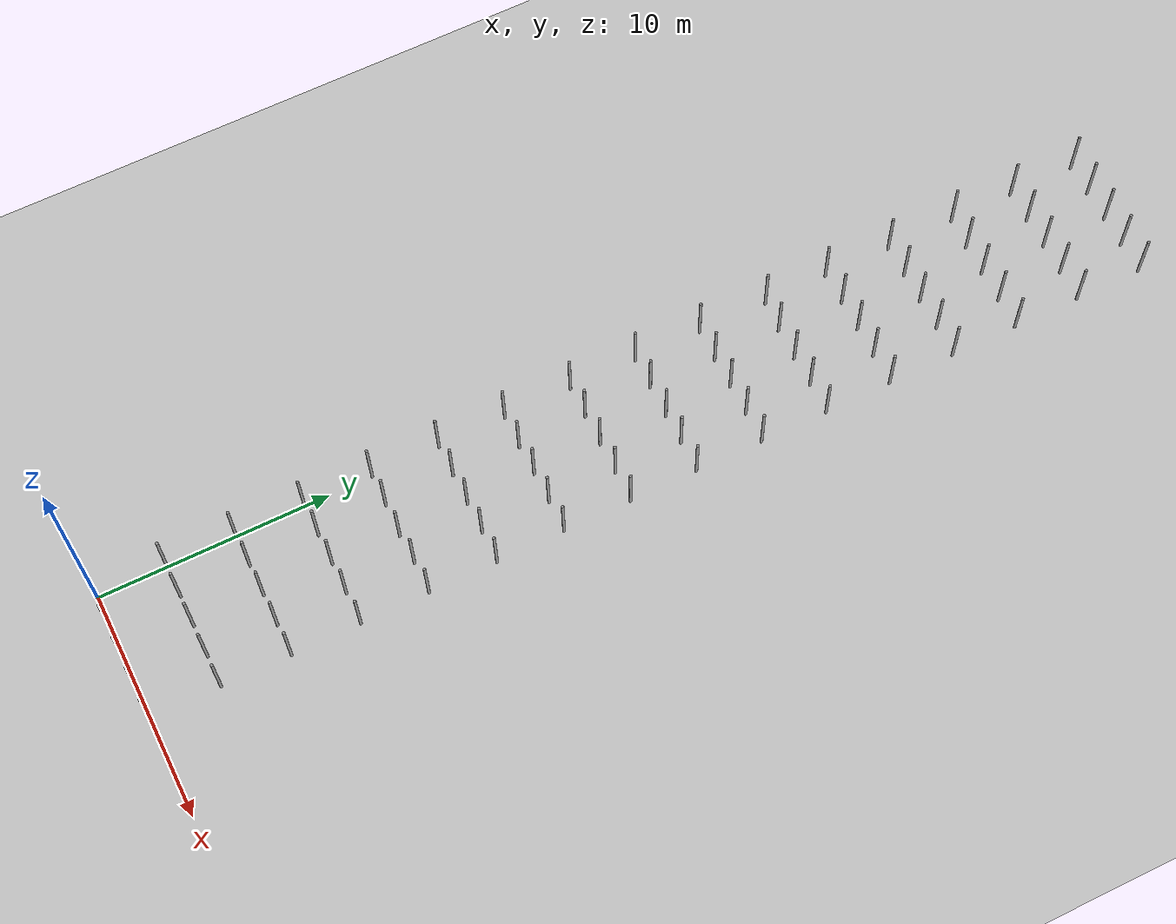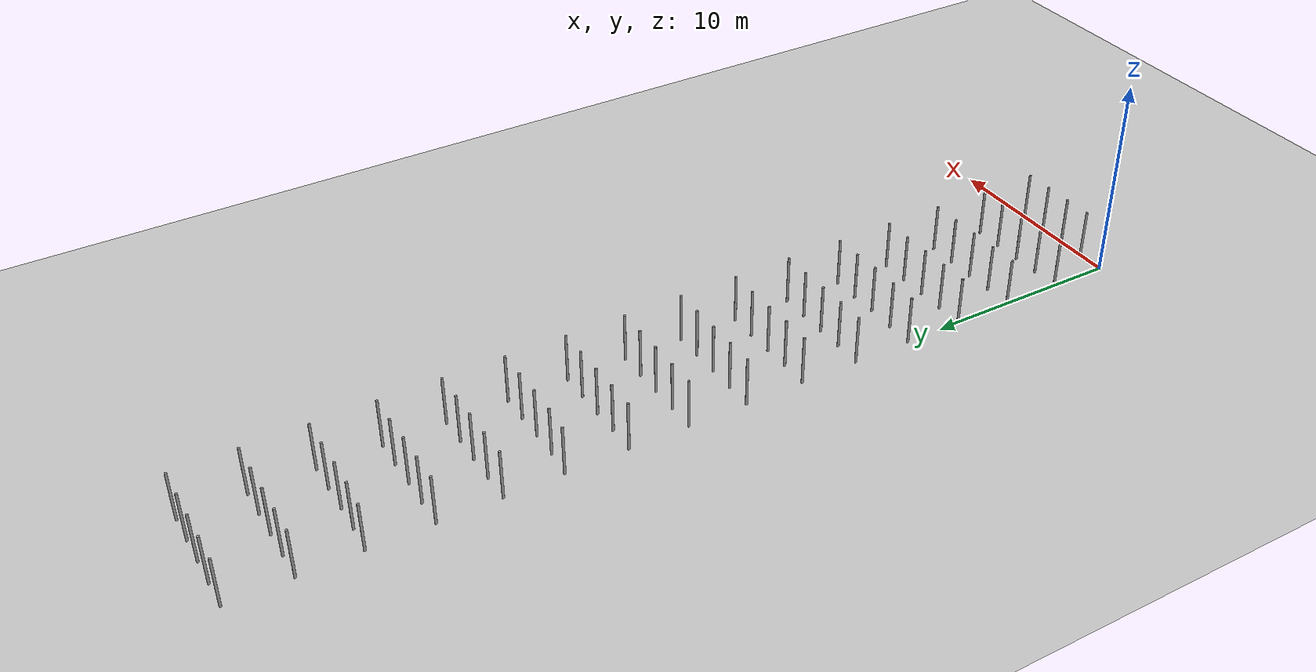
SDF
<sdf version="1.6">
 <world name="default">
  <light name="sun" type="directional">
   <pose>0 0 10 0 -0 0</pose>
   <diffuse>0.8 0.8 0.8 1</diffuse>
   <specular>0.1 0.1 0.1 1</specular>
   <attenuation>
    <range>1000</range>
    <constant>0.9</constant>
    <linear>0.01</linear>
    <quadratic>0.001</quadratic>
   </attenuation>
   <direction>-0.5 0.5 -1</direction>
  </light>
  <model name="ground_plane">
   <static>1</static>
   <link name="link">
    <collision name="collision">
     <geometry><plane><normal>0 0 1</normal><size>100 100</size></plane></geometry>
     <surface><friction><ode><mu>100</mu><mu2>50</mu2></ode></friction></surface>
    </collision>
    <visual name="visual">
     <cast_shadows>0</cast_shadows>
     <geometry><plane><normal>0 0 1</normal><size>100 100</size></plane></geometry>
     <material>
      <script><uri>file://media/materials/scripts/gazebo.material</uri><name>Gazebo/Grey</name></script>
     </material>
    </visual>
   </link>
  </model>
  <gravity>0 0 -9.8</gravity>
  <magnetic_field>6e-06 2.3e-05 -4.2e-05</magnetic_field>
  <atmosphere type="adiabatic"/>
  <physics name="default_physics" default="0" type="ode">
   <max_step_size>0.001</max_step_size>
   <real_time_factor>1</real_time_factor>
   <real_time_update_rate>1000</real_time_update_rate>
  </physics>
  <scene><ambient>0.4 0.4 0.4 1</ambient><background>0.7 0.7 0.7 1</background><shadows>1</shadows></scene>
  <spherical_coordinates>
   <surface_model>EARTH_WGS84</surface_model>
   <latitude_deg>0</latitude_deg>
   <longitude_deg>0</longitude_deg>
   <elevation>0</elevation>
   <heading_deg>0</heading_deg>
  </spherical_coordinates>
  <model name="pole_8">
   <link name="link_0">
    <inertial>
     <mass>0.0364582</mass>
     <inertia>
      <ixx>0.00312124</ixx>
      <ixy>0</ixy>
      <ixz>0</ixz>
      <iyy>0.00312124</iyy>
      <iyz>0</iyz>
      <izz>0.00016615</izz>
     </inertia>
    </inertial>
    <visual name="visual">
     <geometry><cylinder><radius>0.06</radius><length>2.5</length></cylinder></geometry>
     <material>
      <lighting>1</lighting>
      <script><uri>file://media/materials/scripts/gazebo.material</uri><name>Gazebo/Grey</name></script>
      <ambient>0.3 0.3 0.3 1</ambient>
      <diffuse>0.7 0.7 0.7 1</diffuse>
      <specular>0.01 0.01 0.01 1</specular>
      <emissive>0 0 0 1</emissive>
      <shader type="vertex"><normal_map>__default__</normal_map></shader>
     </material>
    </visual>
    <collision name="collision">
     <geometry><cylinder><radius>0.06</radius><length>2.5</length></cylinder></geometry>
     <surface>
      <friction>
       <ode><mu>1</mu><mu2>1</mu2><fdir1>0 0 0</fdir1><slip1>0</slip1><slip2>0</slip2></ode>
       <torsional>
        <coefficient>1</coefficient>
        <patch_radius>0</patch_radius>
        <surface_radius>0</surface_radius>
        <use_patch_radius>1</use_patch_radius>
        <ode><slip>0</slip></ode>
       </torsional>
      </friction>
      <bounce><restitution_coefficient>0</restitution_coefficient><threshold>1e+06</threshold></bounce>
      <contact>
       <collide_without_contact>0</collide_without_contact>
       <collide_without_contact_bitmask>1</collide_without_contact_bitmask>
       <collide_bitmask>1</collide_bitmask>
       <ode>
        <soft_cfm>0</soft_cfm>
        <soft_erp>0.2</soft_erp>
        <kp>1e+13</kp>
        <kd>1</kd>
        <max_vel>0.01</max_vel>
        <min_depth>0</min_depth>
       </ode>
       <bullet>
        <split_impulse>1</split_impulse>
        <split_impulse_penetration_threshold>-0.01</split_impulse_penetration_threshold>
        <soft_cfm>0</soft_cfm>
        <soft_erp>0.2</soft_erp>
        <kp>1e+13</kp>
        <kd>1</kd>
       </bullet>
      </contact>
     </surface>
    </collision>
   </link>
   <static>0</static>
   <pose>1.40458 0.004334 1.25 -1e-06 -1e-06 -0.048905</pose>
  </model>
  <model name="pole_9">
   <link name="link_0">
    <inertial>
     <mass>0.0364582</mass>
     <inertia>
      <ixx>0.00312124</ixx>
      <ixy>0</ixy>
      <ixz>0</ixz>
      <iyy>0.00312124</iyy>
      <iyz>0</iyz>
      <izz>0.00016615</izz>
     </inertia>
    </inertial>
    <visual name="visual">
     <geometry><cylinder><radius>0.06</radius><length>2.5</length></cylinder></geometry>
     <material>
      <lighting>1</lighting>
      <script><uri>file://media/materials/scripts/gazebo.material</uri><name>Gazebo/Grey</name></script>
      <ambient>0.3 0.3 0.3 1</ambient>
      <diffuse>0.7 0.7 0.7 1</diffuse>
      <specular>0.01 0.01 0.01 1</specular>
      <emissive>0 0 0 1</emissive>
      <shader type="vertex"><normal_map>__default__</normal_map></shader>
     </material>
    </visual>
    <collision name="collision">
     <geometry><cylinder><radius>0.06</radius><length>2.5</length></cylinder></geometry>
     <surface>
      <friction>
       <ode><mu>1</mu><mu2>1</mu2><fdir1>0 0 0</fdir1><slip1>0</slip1><slip2>0</slip2></ode>
       <torsional>
        <coefficient>1</coefficient>
        <patch_radius>0</patch_radius>
        <surface_radius>0</surface_radius>
        <use_patch_radius>1</use_patch_radius>
        <ode><slip>0</slip></ode>
       </torsional>
      </friction>
      <bounce><restitution_coefficient>0</restitution_coefficient><threshold>1e+06</threshold></bounce>
      <contact>
       <collide_without_contact>0</collide_without_contact>
       <collide_without_contact_bitmask>1</collide_without_contact_bitmask>
       <collide_bitmask>1</collide_bitmask>
       <ode>
        <soft_cfm>0</soft_cfm>
        <soft_erp>0.2</soft_erp>
        <kp>1e+13</kp>
        <kd>1</kd>
        <max_vel>0.01</max_vel>
        <min_depth>0</min_depth>
       </ode>
       <bullet>
        <split_impulse>1</split_impulse>
        <split_impulse_penetration_threshold>-0.01</split_impulse_penetration_threshold>
        <soft_cfm>0</soft_cfm>
        <soft_erp>0.2</soft_erp>
        <kp>1e+13</kp>
        <kd>1</kd>
       </bullet>
      </contact>
     </surface>
    </collision>
   </link>
   <static>0</static>
   <pose>2.80841 0.004531 1.24999 0 -1e-06 -0.065693</pose>
  </model>
  <model name="pole_10">
   <link name="link_0">
    <inertial>
     <mass>0.0364582</mass>
     <inertia>
      <ixx>0.00312124</ixx>
      <ixy>0</ixy>
      <ixz>0</ixz>
      <iyy>0.00312124</iyy>
      <iyz>0</iyz>
      <izz>0.00016615</izz>
     </inertia>
    </inertial>
    <visual name="visual">
     <geometry><cylinder><radius>0.06</radius><length>2.5</length></cylinder></geometry>
     <material>
      <lighting>1</lighting>
      <script><uri>file://media/materials/scripts/gazebo.material</uri><name>Gazebo/Grey</name></script>
      <ambient>0.3 0.3 0.3 1</ambient>
      <diffuse>0.7 0.7 0.7 1</diffuse>
      <specular>0.01 0.01 0.01 1</specular>
      <emissive>0 0 0 1</emissive>
      <shader type="vertex"><normal_map>__default__</normal_map></shader>
     </material>
    </visual>
    <collision name="collision">
     <geometry><cylinder><radius>0.06</radius><length>2.5</length></cylinder></geometry>
     <surface>
      <friction>
       <ode><mu>1</mu><mu2>1</mu2><fdir1>0 0 0</fdir1><slip1>0</slip1><slip2>0</slip2></ode>
       <torsional>
        <coefficient>1</coefficient>
        <patch_radius>0</patch_radius>
        <surface_radius>0</surface_radius>
        <use_patch_radius>1</use_patch_radius>
        <ode><slip>0</slip></ode>
       </torsional>
      </friction>
      <bounce><restitution_coefficient>0</restitution_coefficient><threshold>1e+06</threshold></bounce>
      <contact>
       <collide_without_contact>0</collide_without_contact>
       <collide_without_contact_bitmask>1</collide_without_contact_bitmask>
       <collide_bitmask>1</collide_bitmask>
       <ode>
        <soft_cfm>0</soft_cfm>
        <soft_erp>0.2</soft_erp>
        <kp>1e+13</kp>
        <kd>1</kd>
        <max_vel>0.01</max_vel>
        <min_depth>0</min_depth>
       </ode>
       <bullet>
        <split_impulse>1</split_impulse>
        <split_impulse_penetration_threshold>-0.01</split_impulse_penetration_threshold>
        <soft_cfm>0</soft_cfm>
        <soft_erp>0.2</soft_erp>
        <kp>1e+13</kp>
        <kd>1</kd>
       </bullet>
      </contact>
     </surface>
    </collision>
   </link>
   <static>0</static>
   <pose>4.20432 0.004396 1.24999 0 0 -0.050585</pose>
  </model>
  <model name="pole_11">
   <link name="link_0">
    <inertial>
     <mass>0.0364582</mass>
     <inertia>
      <ixx>0.00312124</ixx>
      <ixy>0</ixy>
      <ixz>0</ixz>
      <iyy>0.00312124</iyy>
      <iyz>0</iyz>
      <izz>0.00016615</izz>
     </inertia>
    </inertial>
    <visual name="visual">
     <geometry><cylinder><radius>0.06</radius><length>2.5</length></cylinder></geometry>
     <material>
      <lighting>1</lighting>
      <script><uri>file://media/materials/scripts/gazebo.material</uri><name>Gazebo/Grey</name></script>
      <ambient>0.3 0.3 0.3 1</ambient>
      <diffuse>0.7 0.7 0.7 1</diffuse>
      <specular>0.01 0.01 0.01 1</specular>
      <emissive>0 0 0 1</emissive>
      <shader type="vertex"><normal_map>__default__</normal_map></shader>
     </material>
    </visual>
    <collision name="collision">
     <geometry><cylinder><radius>0.06</radius><length>2.5</length></cylinder></geometry>
     <surface>
      <friction>
       <ode><mu>1</mu><mu2>1</mu2><fdir1>0 0 0</fdir1><slip1>0</slip1><slip2>0</slip2></ode>
       <torsional>
        <coefficient>1</coefficient>
        <patch_radius>0</patch_radius>
        <surface_radius>0</surface_radius>
        <use_patch_radius>1</use_patch_radius>
        <ode><slip>0</slip></ode>
       </torsional>
      </friction>
      <bounce><restitution_coefficient>0</restitution_coefficient><threshold>1e+06</threshold></bounce>
      <contact>
       <collide_without_contact>0</collide_without_contact>
       <collide_without_contact_bitmask>1</collide_without_contact_bitmask>
       <collide_bitmask>1</collide_bitmask>
       <ode>
        <soft_cfm>0</soft_cfm>
        <soft_erp>0.2</soft_erp>
        <kp>1e+13</kp>
        <kd>1</kd>
        <max_vel>0.01</max_vel>
        <min_depth>0</min_depth>
       </ode>
       <bullet>
        <split_impulse>1</split_impulse>
        <split_impulse_penetration_threshold>-0.01</split_impulse_penetration_threshold>
        <soft_cfm>0</soft_cfm>
        <soft_erp>0.2</soft_erp>
        <kp>1e+13</kp>
        <kd>1</kd>
       </bullet>
      </contact>
     </surface>
    </collision>
   </link>
   <static>0</static>
   <pose>5.61663 0.004056 1.24999 1e-06 -3e-06 -0.051908</pose>
  </model>
  <model name="pole_11_clone">
   <link name="link_0">
    <inertial>
     <mass>0.0364582</mass>
     <inertia>
      <ixx>0.00312124</ixx>
      <ixy>0</ixy>
      <ixz>0</ixz>
      <iyy>0.00312124</iyy>
      <iyz>0</iyz>
      <izz>0.00016615</izz>
     </inertia>
    </inertial>
    <visual name="visual">
     <geometry><cylinder><radius>0.06</radius><length>2.5</length></cylinder></geometry>
     <material>
      <lighting>1</lighting>
      <script><uri>file://media/materials/scripts/gazebo.material</uri><name>Gazebo/Grey</name></script>
      <ambient>0.3 0.3 0.3 1</ambient>
      <diffuse>0.7 0.7 0.7 1</diffuse>
      <specular>0.01 0.01 0.01 1</specular>
      <emissive>0 0 0 1</emissive>
      <shader type="vertex"><normal_map>__default__</normal_map></shader>
     </material>
    </visual>
    <collision name="collision">
     <geometry><cylinder><radius>0.06</radius><length>2.5</length></cylinder></geometry>
     <surface>
      <friction>
       <ode><mu>1</mu><mu2>1</mu2><fdir1>0 0 0</fdir1><slip1>0</slip1><slip2>0</slip2></ode>
       <torsional>
        <coefficient>1</coefficient>
        <patch_radius>0</patch_radius>
        <surface_radius>0</surface_radius>
        <use_patch_radius>1</use_patch_radius>
        <ode><slip>0</slip></ode>
       </torsional>
      </friction>
      <bounce><restitution_coefficient>0</restitution_coefficient><threshold>1e+06</threshold></bounce>
      <contact>
       <collide_without_contact>0</collide_without_contact>
       <collide_without_contact_bitmask>1</collide_without_contact_bitmask>
       <collide_bitmask>1</collide_bitmask>
       <ode>
        <soft_cfm>0</soft_cfm>
        <soft_erp>0.2</soft_erp>
        <kp>1e+13</kp>
        <kd>1</kd>
        <max_vel>0.01</max_vel>
        <min_depth>0</min_depth>
       </ode>
       <bullet>
        <split_impulse>1</split_impulse>
        <split_impulse_penetration_threshold>-0.01</split_impulse_penetration_threshold>
        <soft_cfm>0</soft_cfm>
        <soft_erp>0.2</soft_erp>
        <kp>1e+13</kp>
        <kd>1</kd>
       </bullet>
      </contact>
     </surface>
    </collision>
   </link>
   <static>0</static>
   <pose>0.000584 2.98425 1.24999 0 -2e-06 -0.047811</pose>
  </model>
  <model name="pole">
   <link name="link_0">
    <inertial>
     <mass>0.0364582</mass>
     <inertia>
      <ixx>0.00312124</ixx>
      <ixy>0</ixy>
      <ixz>0</ixz>
      <iyy>0.00312124</iyy>
      <iyz>0</iyz>
      <izz>0.00016615</izz>
     </inertia>
    </inertial>
    <visual name="visual">
     <geometry><cylinder><radius>0.06</radius><length>2.5</length></cylinder></geometry>
     <material>
      <lighting>1</lighting>
      <script><uri>file://media/materials/scripts/gazebo.material</uri><name>Gazebo/Grey</name></script>
      <ambient>0.3 0.3 0.3 1</ambient>
      <diffuse>0.7 0.7 0.7 1</diffuse>
      <specular>0.01 0.01 0.01 1</specular>
      <emissive>0 0 0 1</emissive>
      <shader type="vertex"><normal_map>__default__</normal_map></shader>
     </material>
    </visual>
    <collision name="collision">
     <geometry><cylinder><radius>0.06</radius><length>2.5</length></cylinder></geometry>
     <surface>
      <friction>
       <ode><mu>1</mu><mu2>1</mu2><fdir1>0 0 0</fdir1><slip1>0</slip1><slip2>0</slip2></ode>
       <torsional>
        <coefficient>1</coefficient>
        <patch_radius>0</patch_radius>
        <surface_radius>0</surface_radius>
        <use_patch_radius>1</use_patch_radius>
        <ode><slip>0</slip></ode>
       </torsional>
      </friction>
      <bounce><restitution_coefficient>0</restitution_coefficient><threshold>1e+06</threshold></bounce>
      <contact>
       <collide_without_contact>0</collide_without_contact>
       <collide_without_contact_bitmask>1</collide_without_contact_bitmask>
       <collide_bitmask>1</collide_bitmask>
       <ode>
        <soft_cfm>0</soft_cfm>
        <soft_erp>0.2</soft_erp>
        <kp>1e+13</kp>
        <kd>1</kd>
        <max_vel>0.01</max_vel>
        <min_depth>0</min_depth>
       </ode>
       <bullet>
        <split_impulse>1</split_impulse>
        <split_impulse_penetration_threshold>-0.01</split_impulse_penetration_threshold>
        <soft_cfm>0</soft_cfm>
        <soft_erp>0.2</soft_erp>
        <kp>1e+13</kp>
        <kd>1</kd>
       </bullet>
      </contact>
     </surface>
    </collision>
   </link>
   <static>0</static>
   <pose>0.007109 5.96385 1.25 -1e-06 1e-06 -0.047287</pose>
  </model>
  <model name="pole_0">
   <link name="link_0">
    <inertial>
     <mass>0.0364582</mass>
     <inertia>
      <ixx>0.00312124</ixx>
      <ixy>0</ixy>
      <ixz>0</ixz>
      <iyy>0.00312124</iyy>
      <iyz>0</iyz>
      <izz>0.00016615</izz>
     </inertia>
    </inertial>
    <visual name="visual">
     <geometry><cylinder><radius>0.06</radius><length>2.5</length></cylinder></geometry>
     <material>
      <lighting>1</lighting>
      <script><uri>file://media/materials/scripts/gazebo.material</uri><name>Gazebo/Grey</name></script>
      <ambient>0.3 0.3 0.3 1</ambient>
      <diffuse>0.7 0.7 0.7 1</diffuse>
      <specular>0.01 0.01 0.01 1</specular>
      <emissive>0 0 0 1</emissive>
      <shader type="vertex"><normal_map>__default__</normal_map></shader>
     </material>
    </visual>
    <collision name="collision">
     <geometry><cylinder><radius>0.06</radius><length>2.5</length></cylinder></geometry>
     <surface>
      <friction>
       <ode><mu>1</mu><mu2>1</mu2><fdir1>0 0 0</fdir1><slip1>0</slip1><slip2>0</slip2></ode>
       <torsional>
        <coefficient>1</coefficient>
        <patch_radius>0</patch_radius>
        <surface_radius>0</surface_radius>
        <use_patch_radius>1</use_patch_radius>
        <ode><slip>0</slip></ode>
       </torsional>
      </friction>
      <bounce><restitution_coefficient>0</restitution_coefficient><threshold>1e+06</threshold></bounce>
      <contact>
       <collide_without_contact>0</collide_without_contact>
       <collide_without_contact_bitmask>1</collide_without_contact_bitmask>
       <collide_bitmask>1</collide_bitmask>
       <ode>
        <soft_cfm>0</soft_cfm>
        <soft_erp>0.2</soft_erp>
        <kp>1e+13</kp>
        <kd>1</kd>
        <max_vel>0.01</max_vel>
        <min_depth>0</min_depth>
       </ode>
       <bullet>
        <split_impulse>1</split_impulse>
        <split_impulse_penetration_threshold>-0.01</split_impulse_penetration_threshold>
        <soft_cfm>0</soft_cfm>
        <soft_erp>0.2</soft_erp>
        <kp>1e+13</kp>
        <kd>1</kd>
       </bullet>
      </contact>
     </surface>
    </collision>
   </link>
   <static>0</static>
   <pose>0.013891 8.94396 1.25 -1e-06 -1e-06 -0.046625</pose>
  </model>
  <model name="pole_1">
   <link name="link_0">
    <inertial>
     <mass>0.0364582</mass>
     <inertia>
      <ixx>0.00312124</ixx>
      <ixy>0</ixy>
      <ixz>0</ixz>
      <iyy>0.00312124</iyy>
      <iyz>0</iyz>
      <izz>0.00016615</izz>
     </inertia>
    </inertial>
    <visual name="visual">
     <geometry><cylinder><radius>0.06</radius><length>2.5</length></cylinder></geometry>
     <material>
      <lighting>1</lighting>
      <script><uri>file://media/materials/scripts/gazebo.material</uri><name>Gazebo/Grey</name></script>
      <ambient>0.3 0.3 0.3 1</ambient>
      <diffuse>0.7 0.7 0.7 1</diffuse>
      <specular>0.01 0.01 0.01 1</specular>
      <emissive>0 0 0 1</emissive>
      <shader type="vertex"><normal_map>__default__</normal_map></shader>
     </material>
    </visual>
    <collision name="collision">
     <geometry><cylinder><radius>0.06</radius><length>2.5</length></cylinder></geometry>
     <surface>
      <friction>
       <ode><mu>1</mu><mu2>1</mu2><fdir1>0 0 0</fdir1><slip1>0</slip1><slip2>0</slip2></ode>
       <torsional>
        <coefficient>1</coefficient>
        <patch_radius>0</patch_radius>
        <surface_radius>0</surface_radius>
        <use_patch_radius>1</use_patch_radius>
        <ode><slip>0</slip></ode>
       </torsional>
      </friction>
      <bounce><restitution_coefficient>0</restitution_coefficient><threshold>1e+06</threshold></bounce>
      <contact>
       <collide_without_contact>0</collide_without_contact>
       <collide_without_contact_bitmask>1</collide_without_contact_bitmask>
       <collide_bitmask>1</collide_bitmask>
       <ode>
        <soft_cfm>0</soft_cfm>
        <soft_erp>0.2</soft_erp>
        <kp>1e+13</kp>
        <kd>1</kd>
        <max_vel>0.01</max_vel>
        <min_depth>0</min_depth>
       </ode>
       <bullet>
        <split_impulse>1</split_impulse>
        <split_impulse_penetration_threshold>-0.01</split_impulse_penetration_threshold>
        <soft_cfm>0</soft_cfm>
        <soft_erp>0.2</soft_erp>
        <kp>1e+13</kp>
        <kd>1</kd>
       </bullet>
      </contact>
     </surface>
    </collision>
   </link>
   <static>0</static>
   <pose>-0.007686 11.9243 1.25 0 3e-06 -0.049828</pose>
  </model>
  <model name="pole_2">
   <link name="link_0">
    <inertial>
     <mass>0.0364582</mass>
     <inertia>
      <ixx>0.00312124</ixx>
      <ixy>0</ixy>
      <ixz>0</ixz>
      <iyy>0.00312124</iyy>
      <iyz>0</iyz>
      <izz>0.00016615</izz>
     </inertia>
    </inertial>
    <visual name="visual">
     <geometry><cylinder><radius>0.06</radius><length>2.5</length></cylinder></geometry>
     <material>
      <lighting>1</lighting>
      <script><uri>file://media/materials/scripts/gazebo.material</uri><name>Gazebo/Grey</name></script>
      <ambient>0.3 0.3 0.3 1</ambient>
      <diffuse>0.7 0.7 0.7 1</diffuse>
      <specular>0.01 0.01 0.01 1</specular>
      <emissive>0 0 0 1</emissive>
      <shader type="vertex"><normal_map>__default__</normal_map></shader>
     </material>
    </visual>
    <collision name="collision">
     <geometry><cylinder><radius>0.06</radius><length>2.5</length></cylinder></geometry>
     <surface>
      <friction>
       <ode><mu>1</mu><mu2>1</mu2><fdir1>0 0 0</fdir1><slip1>0</slip1><slip2>0</slip2></ode>
       <torsional>
        <coefficient>1</coefficient>
        <patch_radius>0</patch_radius>
        <surface_radius>0</surface_radius>
        <use_patch_radius>1</use_patch_radius>
        <ode><slip>0</slip></ode>
       </torsional>
      </friction>
      <bounce><restitution_coefficient>0</restitution_coefficient><threshold>1e+06</threshold></bounce>
      <contact>
       <collide_without_contact>0</collide_without_contact>
       <collide_without_contact_bitmask>1</collide_without_contact_bitmask>
       <collide_bitmask>1</collide_bitmask>
       <ode>
        <soft_cfm>0</soft_cfm>
        <soft_erp>0.2</soft_erp>
        <kp>1e+13</kp>
        <kd>1</kd>
        <max_vel>0.01</max_vel>
        <min_depth>0</min_depth>
       </ode>
       <bullet>
        <split_impulse>1</split_impulse>
        <split_impulse_penetration_threshold>-0.01</split_impulse_penetration_threshold>
        <soft_cfm>0</soft_cfm>
        <soft_erp>0.2</soft_erp>
        <kp>1e+13</kp>
        <kd>1</kd>
       </bullet>
      </contact>
     </surface>
    </collision>
   </link>
   <static>0</static>
   <pose>0.00041 14.897 1.24999 0 1e-06 0.188047</pose>
  </model>
  <model name="pole_3">
   <link name="link_0">
    <inertial>
     <mass>0.0364582</mass>
     <inertia>
      <ixx>0.00312124</ixx>
      <ixy>0</ixy>
      <ixz>0</ixz>
      <iyy>0.00312124</iyy>
      <iyz>0</iyz>
      <izz>0.00016615</izz>
     </inertia>
    </inertial>
    <visual name="visual">
     <geometry><cylinder><radius>0.06</radius><length>2.5</length></cylinder></geometry>
     <material>
      <lighting>1</lighting>
      <script><uri>file://media/materials/scripts/gazebo.material</uri><name>Gazebo/Grey</name></script>
      <ambient>0.3 0.3 0.3 1</ambient>
      <diffuse>0.7 0.7 0.7 1</diffuse>
      <specular>0.01 0.01 0.01 1</specular>
      <emissive>0 0 0 1</emissive>
      <shader type="vertex"><normal_map>__default__</normal_map></shader>
     </material>
    </visual>
    <collision name="collision">
     <geometry><cylinder><radius>0.06</radius><length>2.5</length></cylinder></geometry>
     <surface>
      <friction>
       <ode><mu>1</mu><mu2>1</mu2><fdir1>0 0 0</fdir1><slip1>0</slip1><slip2>0</slip2></ode>
       <torsional>
        <coefficient>1</coefficient>
        <patch_radius>0</patch_radius>
        <surface_radius>0</surface_radius>
        <use_patch_radius>1</use_patch_radius>
        <ode><slip>0</slip></ode>
       </torsional>
      </friction>
      <bounce><restitution_coefficient>0</restitution_coefficient><threshold>1e+06</threshold></bounce>
      <contact>
       <collide_without_contact>0</collide_without_contact>
       <collide_without_contact_bitmask>1</collide_without_contact_bitmask>
       <collide_bitmask>1</collide_bitmask>
       <ode>
        <soft_cfm>0</soft_cfm>
        <soft_erp>0.2</soft_erp>
        <kp>1e+13</kp>
        <kd>1</kd>
        <max_vel>0.01</max_vel>
        <min_depth>0</min_depth>
       </ode>
       <bullet>
        <split_impulse>1</split_impulse>
        <split_impulse_penetration_threshold>-0.01</split_impulse_penetration_threshold>
        <soft_cfm>0</soft_cfm>
        <soft_erp>0.2</soft_erp>
        <kp>1e+13</kp>
        <kd>1</kd>
       </bullet>
      </contact>
     </surface>
    </collision>
   </link>
   <static>0</static>
   <pose>1.40509 2.98392 1.24999 -0 1e-06 -0.043168</pose>
  </model>
  <model name="pole_5">
   <link name="link_0">
    <inertial>
     <mass>0.0364582</mass>
     <inertia>
      <ixx>0.00312124</ixx>
      <ixy>0</ixy>
      <ixz>0</ixz>
      <iyy>0.00312124</iyy>
      <iyz>0</iyz>
      <izz>0.00016615</izz>
     </inertia>
    </inertial>
    <visual name="visual">
     <geometry><cylinder><radius>0.06</radius><length>2.5</length></cylinder></geometry>
     <material>
      <lighting>1</lighting>
      <script><uri>file://media/materials/scripts/gazebo.material</uri><name>Gazebo/Grey</name></script>
      <ambient>0.3 0.3 0.3 1</ambient>
      <diffuse>0.7 0.7 0.7 1</diffuse>
      <specular>0.01 0.01 0.01 1</specular>
      <emissive>0 0 0 1</emissive>
      <shader type="vertex"><normal_map>__default__</normal_map></shader>
     </material>
    </visual>
    <collision name="collision">
     <geometry><cylinder><radius>0.06</radius><length>2.5</length></cylinder></geometry>
     <surface>
      <friction>
       <ode><mu>1</mu><mu2>1</mu2><fdir1>0 0 0</fdir1><slip1>0</slip1><slip2>0</slip2></ode>
       <torsional>
        <coefficient>1</coefficient>
        <patch_radius>0</patch_radius>
        <surface_radius>0</surface_radius>
        <use_patch_radius>1</use_patch_radius>
        <ode><slip>0</slip></ode>
       </torsional>
      </friction>
      <bounce><restitution_coefficient>0</restitution_coefficient><threshold>1e+06</threshold></bounce>
      <contact>
       <collide_without_contact>0</collide_without_contact>
       <collide_without_contact_bitmask>1</collide_without_contact_bitmask>
       <collide_bitmask>1</collide_bitmask>
       <ode>
        <soft_cfm>0</soft_cfm>
        <soft_erp>0.2</soft_erp>
        <kp>1e+13</kp>
        <kd>1</kd>
        <max_vel>0.01</max_vel>
        <min_depth>0</min_depth>
       </ode>
       <bullet>
        <split_impulse>1</split_impulse>
        <split_impulse_penetration_threshold>-0.01</split_impulse_penetration_threshold>
        <soft_cfm>0</soft_cfm>
        <soft_erp>0.2</soft_erp>
        <kp>1e+13</kp>
        <kd>1</kd>
       </bullet>
      </contact>
     </surface>
    </collision>
   </link>
   <static>0</static>
   <pose>2.7962 2.98396 1.25 -1e-06 -0 -0.043155</pose>
  </model>
  <model name="pole_6">
   <link name="link_0">
    <inertial>
     <mass>0.0364582</mass>
     <inertia>
      <ixx>0.00312124</ixx>
      <ixy>0</ixy>
      <ixz>0</ixz>
      <iyy>0.00312124</iyy>
      <iyz>0</iyz>
      <izz>0.00016615</izz>
     </inertia>
    </inertial>
    <visual name="visual">
     <geometry><cylinder><radius>0.06</radius><length>2.5</length></cylinder></geometry>
     <material>
      <lighting>1</lighting>
      <script><uri>file://media/materials/scripts/gazebo.material</uri><name>Gazebo/Grey</name></script>
      <ambient>0.3 0.3 0.3 1</ambient>
      <diffuse>0.7 0.7 0.7 1</diffuse>
      <specular>0.01 0.01 0.01 1</specular>
      <emissive>0 0 0 1</emissive>
      <shader type="vertex"><normal_map>__default__</normal_map></shader>
     </material>
    </visual>
    <collision name="collision">
     <geometry><cylinder><radius>0.06</radius><length>2.5</length></cylinder></geometry>
     <surface>
      <friction>
       <ode><mu>1</mu><mu2>1</mu2><fdir1>0 0 0</fdir1><slip1>0</slip1><slip2>0</slip2></ode>
       <torsional>
        <coefficient>1</coefficient>
        <patch_radius>0</patch_radius>
        <surface_radius>0</surface_radius>
        <use_patch_radius>1</use_patch_radius>
        <ode><slip>0</slip></ode>
       </torsional>
      </friction>
      <bounce><restitution_coefficient>0</restitution_coefficient><threshold>1e+06</threshold></bounce>
      <contact>
       <collide_without_contact>0</collide_without_contact>
       <collide_without_contact_bitmask>1</collide_without_contact_bitmask>
       <collide_bitmask>1</collide_bitmask>
       <ode>
        <soft_cfm>0</soft_cfm>
        <soft_erp>0.2</soft_erp>
        <kp>1e+13</kp>
        <kd>1</kd>
        <max_vel>0.01</max_vel>
        <min_depth>0</min_depth>
       </ode>
       <bullet>
        <split_impulse>1</split_impulse>
        <split_impulse_penetration_threshold>-0.01</split_impulse_penetration_threshold>
        <soft_cfm>0</soft_cfm>
        <soft_erp>0.2</soft_erp>
        <kp>1e+13</kp>
        <kd>1</kd>
       </bullet>
      </contact>
     </surface>
    </collision>
   </link>
   <static>0</static>
   <pose>4.22278 2.98404 1.24999 -1e-06 -0 -0.043529</pose>
  </model>
  <model name="pole_7">
   <link name="link_0">
    <inertial>
     <mass>0.0364582</mass>
     <inertia>
      <ixx>0.00312124</ixx>
      <ixy>0</ixy>
      <ixz>0</ixz>
      <iyy>0.00312124</iyy>
      <iyz>0</iyz>
      <izz>0.00016615</izz>
     </inertia>
    </inertial>
    <visual name="visual">
     <geometry><cylinder><radius>0.06</radius><length>2.5</length></cylinder></geometry>
     <material>
      <lighting>1</lighting>
      <script><uri>file://media/materials/scripts/gazebo.material</uri><name>Gazebo/Grey</name></script>
      <ambient>0.3 0.3 0.3 1</ambient>
      <diffuse>0.7 0.7 0.7 1</diffuse>
      <specular>0.01 0.01 0.01 1</specular>
      <emissive>0 0 0 1</emissive>
      <shader type="vertex"><normal_map>__default__</normal_map></shader>
     </material>
    </visual>
    <collision name="collision">
     <geometry><cylinder><radius>0.06</radius><length>2.5</length></cylinder></geometry>
     <surface>
      <friction>
       <ode><mu>1</mu><mu2>1</mu2><fdir1>0 0 0</fdir1><slip1>0</slip1><slip2>0</slip2></ode>
       <torsional>
        <coefficient>1</coefficient>
        <patch_radius>0</patch_radius>
        <surface_radius>0</surface_radius>
        <use_patch_radius>1</use_patch_radius>
        <ode><slip>0</slip></ode>
       </torsional>
      </friction>
      <bounce><restitution_coefficient>0</restitution_coefficient><threshold>1e+06</threshold></bounce>
      <contact>
       <collide_without_contact>0</collide_without_contact>
       <collide_without_contact_bitmask>1</collide_without_contact_bitmask>
       <collide_bitmask>1</collide_bitmask>
       <ode>
        <soft_cfm>0</soft_cfm>
        <soft_erp>0.2</soft_erp>
        <kp>1e+13</kp>
        <kd>1</kd>
        <max_vel>0.01</max_vel>
        <min_depth>0</min_depth>
       </ode>
       <bullet>
        <split_impulse>1</split_impulse>
        <split_impulse_penetration_threshold>-0.01</split_impulse_penetration_threshold>
        <soft_cfm>0</soft_cfm>
        <soft_erp>0.2</soft_erp>
        <kp>1e+13</kp>
        <kd>1</kd>
       </bullet>
      </contact>
     </surface>
    </collision>
   </link>
   <static>0</static>
   <pose>5.60769 2.98403 1.24999 -1e-06 1e-06 -0.040122</pose>
  </model>
  <model name="pole_12">
   <link name="link_0">
    <inertial>
     <mass>0.0364582</mass>
     <inertia>
      <ixx>0.00312124</ixx>
      <ixy>0</ixy>
      <ixz>0</ixz>
      <iyy>0.00312124</iyy>
      <iyz>0</iyz>
      <izz>0.00016615</izz>
     </inertia>
    </inertial>
    <visual name="visual">
     <geometry><cylinder><radius>0.06</radius><length>2.5</length></cylinder></geometry>
     <material>
      <lighting>1</lighting>
      <script><uri>file://media/materials/scripts/gazebo.material</uri><name>Gazebo/Grey</name></script>
      <ambient>0.3 0.3 0.3 1</ambient>
      <diffuse>0.7 0.7 0.7 1</diffuse>
      <specular>0.01 0.01 0.01 1</specular>
      <emissive>0 0 0 1</emissive>
      <shader type="vertex"><normal_map>__default__</normal_map></shader>
     </material>
    </visual>
    <collision name="collision">
     <geometry><cylinder><radius>0.06</radius><length>2.5</length></cylinder></geometry>
     <surface>
      <friction>
       <ode><mu>1</mu><mu2>1</mu2><fdir1>0 0 0</fdir1><slip1>0</slip1><slip2>0</slip2></ode>
       <torsional>
        <coefficient>1</coefficient>
        <patch_radius>0</patch_radius>
        <surface_radius>0</surface_radius>
        <use_patch_radius>1</use_patch_radius>
        <ode><slip>0</slip></ode>
       </torsional>
      </friction>
      <bounce><restitution_coefficient>0</restitution_coefficient><threshold>1e+06</threshold></bounce>
      <contact>
       <collide_without_contact>0</collide_without_contact>
       <collide_without_contact_bitmask>1</collide_without_contact_bitmask>
       <collide_bitmask>1</collide_bitmask>
       <ode>
        <soft_cfm>0</soft_cfm>
        <soft_erp>0.2</soft_erp>
        <kp>1e+13</kp>
        <kd>1</kd>
        <max_vel>0.01</max_vel>
        <min_depth>0</min_depth>
       </ode>
       <bullet>
        <split_impulse>1</split_impulse>
        <split_impulse_penetration_threshold>-0.01</split_impulse_penetration_threshold>
        <soft_cfm>0</soft_cfm>
        <soft_erp>0.2</soft_erp>
        <kp>1e+13</kp>
        <kd>1</kd>
       </bullet>
      </contact>
     </surface>
    </collision>
   </link>
   <static>0</static>
   <pose>1.41395 5.96379 1.25 -1e-06 -0 -0.039952</pose>
  </model>
  <model name="pole_13">
   <link name="link_0">
    <inertial>
     <mass>0.0364582</mass>
     <inertia>
      <ixx>0.00312124</ixx>
      <ixy>0</ixy>
      <ixz>0</ixz>
      <iyy>0.00312124</iyy>
      <iyz>0</iyz>
      <izz>0.00016615</izz>
     </inertia>
    </inertial>
    <visual name="visual">
     <geometry><cylinder><radius>0.06</radius><length>2.5</length></cylinder></geometry>
     <material>
      <lighting>1</lighting>
      <script><uri>file://media/materials/scripts/gazebo.material</uri><name>Gazebo/Grey</name></script>
      <ambient>0.3 0.3 0.3 1</ambient>
      <diffuse>0.7 0.7 0.7 1</diffuse>
      <specular>0.01 0.01 0.01 1</specular>
      <emissive>0 0 0 1</emissive>
      <shader type="vertex"><normal_map>__default__</normal_map></shader>
     </material>
    </visual>
    <collision name="collision">
     <geometry><cylinder><radius>0.06</radius><length>2.5</length></cylinder></geometry>
     <surface>
      <friction>
       <ode><mu>1</mu><mu2>1</mu2><fdir1>0 0 0</fdir1><slip1>0</slip1><slip2>0</slip2></ode>
       <torsional>
        <coefficient>1</coefficient>
        <patch_radius>0</patch_radius>
        <surface_radius>0</surface_radius>
        <use_patch_radius>1</use_patch_radius>
        <ode><slip>0</slip></ode>
       </torsional>
      </friction>
      <bounce><restitution_coefficient>0</restitution_coefficient><threshold>1e+06</threshold></bounce>
      <contact>
       <collide_without_contact>0</collide_without_contact>
       <collide_without_contact_bitmask>1</collide_without_contact_bitmask>
       <collide_bitmask>1</collide_bitmask>
       <ode>
        <soft_cfm>0</soft_cfm>
        <soft_erp>0.2</soft_erp>
        <kp>1e+13</kp>
        <kd>1</kd>
        <max_vel>0.01</max_vel>
        <min_depth>0</min_depth>
       </ode>
       <bullet>
        <split_impulse>1</split_impulse>
        <split_impulse_penetration_threshold>-0.01</split_impulse_penetration_threshold>
        <soft_cfm>0</soft_cfm>
        <soft_erp>0.2</soft_erp>
        <kp>1e+13</kp>
        <kd>1</kd>
       </bullet>
      </contact>
     </surface>
    </collision>
   </link>
   <static>0</static>
   <pose>2.80843 5.96419 1.24999 -1e-06 1e-06 -0.040437</pose>
  </model>
  <model name="pole_14">
   <link name="link_0">
    <inertial>
     <mass>0.0364582</mass>
     <inertia>
      <ixx>0.00312124</ixx>
      <ixy>0</ixy>
      <ixz>0</ixz>
      <iyy>0.00312124</iyy>
      <iyz>0</iyz>
      <izz>0.00016615</izz>
     </inertia>
    </inertial>
    <visual name="visual">
     <geometry><cylinder><radius>0.06</radius><length>2.5</length></cylinder></geometry>
     <material>
      <lighting>1</lighting>
      <script><uri>file://media/materials/scripts/gazebo.material</uri><name>Gazebo/Grey</name></script>
      <ambient>0.3 0.3 0.3 1</ambient>
      <diffuse>0.7 0.7 0.7 1</diffuse>
      <specular>0.01 0.01 0.01 1</specular>
      <emissive>0 0 0 1</emissive>
      <shader type="vertex"><normal_map>__default__</normal_map></shader>
     </material>
    </visual>
    <collision name="collision">
     <geometry><cylinder><radius>0.06</radius><length>2.5</length></cylinder></geometry>
     <surface>
      <friction>
       <ode><mu>1</mu><mu2>1</mu2><fdir1>0 0 0</fdir1><slip1>0</slip1><slip2>0</slip2></ode>
       <torsional>
        <coefficient>1</coefficient>
        <patch_radius>0</patch_radius>
        <surface_radius>0</surface_radius>
        <use_patch_radius>1</use_patch_radius>
        <ode><slip>0</slip></ode>
       </torsional>
      </friction>
      <bounce><restitution_coefficient>0</restitution_coefficient><threshold>1e+06</threshold></bounce>
      <contact>
       <collide_without_contact>0</collide_without_contact>
       <collide_without_contact_bitmask>1</collide_without_contact_bitmask>
       <collide_bitmask>1</collide_bitmask>
       <ode>
        <soft_cfm>0</soft_cfm>
        <soft_erp>0.2</soft_erp>
        <kp>1e+13</kp>
        <kd>1</kd>
        <max_vel>0.01</max_vel>
        <min_depth>0</min_depth>
       </ode>
       <bullet>
        <split_impulse>1</split_impulse>
        <split_impulse_penetration_threshold>-0.01</split_impulse_penetration_threshold>
        <soft_cfm>0</soft_cfm>
        <soft_erp>0.2</soft_erp>
        <kp>1e+13</kp>
        <kd>1</kd>
       </bullet>
      </contact>
     </surface>
    </collision>
   </link>
   <static>0</static>
   <pose>4.21994 5.96386 1.25 0 -2e-06 -0.041417</pose>
  </model>
  <model name="pole_15">
   <link name="link_0">
    <inertial>
     <mass>0.0364582</mass>
     <inertia>
      <ixx>0.00312124</ixx>
      <ixy>0</ixy>
      <ixz>0</ixz>
      <iyy>0.00312124</iyy>
      <iyz>0</iyz>
      <izz>0.00016615</izz>
     </inertia>
    </inertial>
    <visual name="visual">
     <geometry><cylinder><radius>0.06</radius><length>2.5</length></cylinder></geometry>
     <material>
      <lighting>1</lighting>
      <script><uri>file://media/materials/scripts/gazebo.material</uri><name>Gazebo/Grey</name></script>
      <ambient>0.3 0.3 0.3 1</ambient>
      <diffuse>0.7 0.7 0.7 1</diffuse>
      <specular>0.01 0.01 0.01 1</specular>
      <emissive>0 0 0 1</emissive>
      <shader type="vertex"><normal_map>__default__</normal_map></shader>
     </material>
    </visual>
    <collision name="collision">
     <geometry><cylinder><radius>0.06</radius><length>2.5</length></cylinder></geometry>
     <surface>
      <friction>
       <ode><mu>1</mu><mu2>1</mu2><fdir1>0 0 0</fdir1><slip1>0</slip1><slip2>0</slip2></ode>
       <torsional>
        <coefficient>1</coefficient>
        <patch_radius>0</patch_radius>
        <surface_radius>0</surface_radius>
        <use_patch_radius>1</use_patch_radius>
        <ode><slip>0</slip></ode>
       </torsional>
      </friction>
      <bounce><restitution_coefficient>0</restitution_coefficient><threshold>1e+06</threshold></bounce>
      <contact>
       <collide_without_contact>0</collide_without_contact>
       <collide_without_contact_bitmask>1</collide_without_contact_bitmask>
       <collide_bitmask>1</collide_bitmask>
       <ode>
        <soft_cfm>0</soft_cfm>
        <soft_erp>0.2</soft_erp>
        <kp>1e+13</kp>
        <kd>1</kd>
        <max_vel>0.01</max_vel>
        <min_depth>0</min_depth>
       </ode>
       <bullet>
        <split_impulse>1</split_impulse>
        <split_impulse_penetration_threshold>-0.01</split_impulse_penetration_threshold>
        <soft_cfm>0</soft_cfm>
        <soft_erp>0.2</soft_erp>
        <kp>1e+13</kp>
        <kd>1</kd>
       </bullet>
      </contact>
     </surface>
    </collision>
   </link>
   <static>0</static>
   <pose>5.62392 5.96398 1.24999 0 4e-06 -0.04109</pose>
  </model>
  <model name="pole_16">
   <link name="link_0">
    <inertial>
     <mass>0.0364582</mass>
     <inertia>
      <ixx>0.00312124</ixx>
      <ixy>0</ixy>
      <ixz>0</ixz>
      <iyy>0.00312124</iyy>
      <iyz>0</iyz>
      <izz>0.00016615</izz>
     </inertia>
    </inertial>
    <visual name="visual">
     <geometry><cylinder><radius>0.06</radius><length>2.5</length></cylinder></geometry>
     <material>
      <lighting>1</lighting>
      <script><uri>file://media/materials/scripts/gazebo.material</uri><name>Gazebo/Grey</name></script>
      <ambient>0.3 0.3 0.3 1</ambient>
      <diffuse>0.7 0.7 0.7 1</diffuse>
      <specular>0.01 0.01 0.01 1</specular>
      <emissive>0 0 0 1</emissive>
      <shader type="vertex"><normal_map>__default__</normal_map></shader>
     </material>
    </visual>
    <collision name="collision">
     <geometry><cylinder><radius>0.06</radius><length>2.5</length></cylinder></geometry>
     <surface>
      <friction>
       <ode><mu>1</mu><mu2>1</mu2><fdir1>0 0 0</fdir1><slip1>0</slip1><slip2>0</slip2></ode>
       <torsional>
        <coefficient>1</coefficient>
        <patch_radius>0</patch_radius>
        <surface_radius>0</surface_radius>
        <use_patch_radius>1</use_patch_radius>
        <ode><slip>0</slip></ode>
       </torsional>
      </friction>
      <bounce><restitution_coefficient>0</restitution_coefficient><threshold>1e+06</threshold></bounce>
      <contact>
       <collide_without_contact>0</collide_without_contact>
       <collide_without_contact_bitmask>1</collide_without_contact_bitmask>
       <collide_bitmask>1</collide_bitmask>
       <ode>
        <soft_cfm>0</soft_cfm>
        <soft_erp>0.2</soft_erp>
        <kp>1e+13</kp>
        <kd>1</kd>
        <max_vel>0.01</max_vel>
        <min_depth>0</min_depth>
       </ode>
       <bullet>
        <split_impulse>1</split_impulse>
        <split_impulse_penetration_threshold>-0.01</split_impulse_penetration_threshold>
        <soft_cfm>0</soft_cfm>
        <soft_erp>0.2</soft_erp>
        <kp>1e+13</kp>
        <kd>1</kd>
       </bullet>
      </contact>
     </surface>
    </collision>
   </link>
   <static>0</static>
   <pose>1.41353 8.94332 1.24999 -1e-06 -0 -0.046166</pose>
  </model>
  <model name="pole_17">
   <link name="link_0">
    <inertial>
     <mass>0.0364582</mass>
     <inertia>
      <ixx>0.00312124</ixx>
      <ixy>0</ixy>
      <ixz>0</ixz>
      <iyy>0.00312124</iyy>
      <iyz>0</iyz>
      <izz>0.00016615</izz>
     </inertia>
    </inertial>
    <visual name="visual">
     <geometry><cylinder><radius>0.06</radius><length>2.5</length></cylinder></geometry>
     <material>
      <lighting>1</lighting>
      <script><uri>file://media/materials/scripts/gazebo.material</uri><name>Gazebo/Grey</name></script>
      <ambient>0.3 0.3 0.3 1</ambient>
      <diffuse>0.7 0.7 0.7 1</diffuse>
      <specular>0.01 0.01 0.01 1</specular>
      <emissive>0 0 0 1</emissive>
      <shader type="vertex"><normal_map>__default__</normal_map></shader>
     </material>
    </visual>
    <collision name="collision">
     <geometry><cylinder><radius>0.06</radius><length>2.5</length></cylinder></geometry>
     <surface>
      <friction>
       <ode><mu>1</mu><mu2>1</mu2><fdir1>0 0 0</fdir1><slip1>0</slip1><slip2>0</slip2></ode>
       <torsional>
        <coefficient>1</coefficient>
        <patch_radius>0</patch_radius>
        <surface_radius>0</surface_radius>
        <use_patch_radius>1</use_patch_radius>
        <ode><slip>0</slip></ode>
       </torsional>
      </friction>
      <bounce><restitution_coefficient>0</restitution_coefficient><threshold>1e+06</threshold></bounce>
      <contact>
       <collide_without_contact>0</collide_without_contact>
       <collide_without_contact_bitmask>1</collide_without_contact_bitmask>
       <collide_bitmask>1</collide_bitmask>
       <ode>
        <soft_cfm>0</soft_cfm>
        <soft_erp>0.2</soft_erp>
        <kp>1e+13</kp>
        <kd>1</kd>
        <max_vel>0.01</max_vel>
        <min_depth>0</min_depth>
       </ode>
       <bullet>
        <split_impulse>1</split_impulse>
        <split_impulse_penetration_threshold>-0.01</split_impulse_penetration_threshold>
        <soft_cfm>0</soft_cfm>
        <soft_erp>0.2</soft_erp>
        <kp>1e+13</kp>
        <kd>1</kd>
       </bullet>
      </contact>
     </surface>
    </collision>
   </link>
   <static>0</static>
   <pose>2.80024 8.94336 1.25 -1e-06 -1e-06 -0.039576</pose>
  </model>
  <model name="pole_18">
   <link name="link_0">
    <inertial>
     <mass>0.0364582</mass>
     <inertia>
      <ixx>0.00312124</ixx>
      <ixy>0</ixy>
      <ixz>0</ixz>
      <iyy>0.00312124</iyy>
      <iyz>0</iyz>
      <izz>0.00016615</izz>
     </inertia>
    </inertial>
    <visual name="visual">
     <geometry><cylinder><radius>0.06</radius><length>2.5</length></cylinder></geometry>
     <material>
      <lighting>1</lighting>
      <script><uri>file://media/materials/scripts/gazebo.material</uri><name>Gazebo/Grey</name></script>
      <ambient>0.3 0.3 0.3 1</ambient>
      <diffuse>0.7 0.7 0.7 1</diffuse>
      <specular>0.01 0.01 0.01 1</specular>
      <emissive>0 0 0 1</emissive>
      <shader type="vertex"><normal_map>__default__</normal_map></shader>
     </material>
    </visual>
    <collision name="collision">
     <geometry><cylinder><radius>0.06</radius><length>2.5</length></cylinder></geometry>
     <surface>
      <friction>
       <ode><mu>1</mu><mu2>1</mu2><fdir1>0 0 0</fdir1><slip1>0</slip1><slip2>0</slip2></ode>
       <torsional>
        <coefficient>1</coefficient>
        <patch_radius>0</patch_radius>
        <surface_radius>0</surface_radius>
        <use_patch_radius>1</use_patch_radius>
        <ode><slip>0</slip></ode>
       </torsional>
      </friction>
      <bounce><restitution_coefficient>0</restitution_coefficient><threshold>1e+06</threshold></bounce>
      <contact>
       <collide_without_contact>0</collide_without_contact>
       <collide_without_contact_bitmask>1</collide_without_contact_bitmask>
       <collide_bitmask>1</collide_bitmask>
       <ode>
        <soft_cfm>0</soft_cfm>
        <soft_erp>0.2</soft_erp>
        <kp>1e+13</kp>
        <kd>1</kd>
        <max_vel>0.01</max_vel>
        <min_depth>0</min_depth>
       </ode>
       <bullet>
        <split_impulse>1</split_impulse>
        <split_impulse_penetration_threshold>-0.01</split_impulse_penetration_threshold>
        <soft_cfm>0</soft_cfm>
        <soft_erp>0.2</soft_erp>
        <kp>1e+13</kp>
        <kd>1</kd>
       </bullet>
      </contact>
     </surface>
    </collision>
   </link>
   <static>0</static>
   <pose>4.20421 8.94366 1.25 1e-06 2e-06 -0.038251</pose>
  </model>
  <model name="pole_19">
   <link name="link_0">
    <inertial>
     <mass>0.0364582</mass>
     <inertia>
      <ixx>0.00312124</ixx>
      <ixy>0</ixy>
      <ixz>0</ixz>
      <iyy>0.00312124</iyy>
      <iyz>0</iyz>
      <izz>0.00016615</izz>
     </inertia>
    </inertial>
    <visual name="visual">
     <geometry><cylinder><radius>0.06</radius><length>2.5</length></cylinder></geometry>
     <material>
      <lighting>1</lighting>
      <script><uri>file://media/materials/scripts/gazebo.material</uri><name>Gazebo/Grey</name></script>
      <ambient>0.3 0.3 0.3 1</ambient>
      <diffuse>0.7 0.7 0.7 1</diffuse>
      <specular>0.01 0.01 0.01 1</specular>
      <emissive>0 0 0 1</emissive>
      <shader type="vertex"><normal_map>__default__</normal_map></shader>
     </material>
    </visual>
    <collision name="collision">
     <geometry><cylinder><radius>0.06</radius><length>2.5</length></cylinder></geometry>
     <surface>
      <friction>
       <ode><mu>1</mu><mu2>1</mu2><fdir1>0 0 0</fdir1><slip1>0</slip1><slip2>0</slip2></ode>
       <torsional>
        <coefficient>1</coefficient>
        <patch_radius>0</patch_radius>
        <surface_radius>0</surface_radius>
        <use_patch_radius>1</use_patch_radius>
        <ode><slip>0</slip></ode>
       </torsional>
      </friction>
      <bounce><restitution_coefficient>0</restitution_coefficient><threshold>1e+06</threshold></bounce>
      <contact>
       <collide_without_contact>0</collide_without_contact>
       <collide_without_contact_bitmask>1</collide_without_contact_bitmask>
       <collide_bitmask>1</collide_bitmask>
       <ode>
        <soft_cfm>0</soft_cfm>
        <soft_erp>0.2</soft_erp>
        <kp>1e+13</kp>
        <kd>1</kd>
        <max_vel>0.01</max_vel>
        <min_depth>0</min_depth>
       </ode>
       <bullet>
        <split_impulse>1</split_impulse>
        <split_impulse_penetration_threshold>-0.01</split_impulse_penetration_threshold>
        <soft_cfm>0</soft_cfm>
        <soft_erp>0.2</soft_erp>
        <kp>1e+13</kp>
        <kd>1</kd>
       </bullet>
      </contact>
     </surface>
    </collision>
   </link>
   <static>0</static>
   <pose>5.62972 8.94334 1.24999 0 -1e-06 -0.03947</pose>
  </model>
  <model name="pole_20">
   <link name="link_0">
    <inertial>
     <mass>0.0364582</mass>
     <inertia>
      <ixx>0.00312124</ixx>
      <ixy>0</ixy>
      <ixz>0</ixz>
      <iyy>0.00312124</iyy>
      <iyz>0</iyz>
      <izz>0.00016615</izz>
     </inertia>
    </inertial>
    <visual name="visual">
     <geometry><cylinder><radius>0.06</radius><length>2.5</length></cylinder></geometry>
     <material>
      <lighting>1</lighting>
      <script><uri>file://media/materials/scripts/gazebo.material</uri><name>Gazebo/Grey</name></script>
      <ambient>0.3 0.3 0.3 1</ambient>
      <diffuse>0.7 0.7 0.7 1</diffuse>
      <specular>0.01 0.01 0.01 1</specular>
      <emissive>0 0 0 1</emissive>
      <shader type="vertex"><normal_map>__default__</normal_map></shader>
     </material>
    </visual>
    <collision name="collision">
     <geometry><cylinder><radius>0.06</radius><length>2.5</length></cylinder></geometry>
     <surface>
      <friction>
       <ode><mu>1</mu><mu2>1</mu2><fdir1>0 0 0</fdir1><slip1>0</slip1><slip2>0</slip2></ode>
       <torsional>
        <coefficient>1</coefficient>
        <patch_radius>0</patch_radius>
        <surface_radius>0</surface_radius>
        <use_patch_radius>1</use_patch_radius>
        <ode><slip>0</slip></ode>
       </torsional>
      </friction>
      <bounce><restitution_coefficient>0</restitution_coefficient><threshold>1e+06</threshold></bounce>
      <contact>
       <collide_without_contact>0</collide_without_contact>
       <collide_without_contact_bitmask>1</collide_without_contact_bitmask>
       <collide_bitmask>1</collide_bitmask>
       <ode>
        <soft_cfm>0</soft_cfm>
        <soft_erp>0.2</soft_erp>
        <kp>1e+13</kp>
        <kd>1</kd>
        <max_vel>0.01</max_vel>
        <min_depth>0</min_depth>
       </ode>
       <bullet>
        <split_impulse>1</split_impulse>
        <split_impulse_penetration_threshold>-0.01</split_impulse_penetration_threshold>
        <soft_cfm>0</soft_cfm>
        <soft_erp>0.2</soft_erp>
        <kp>1e+13</kp>
        <kd>1</kd>
       </bullet>
      </contact>
     </surface>
    </collision>
   </link>
   <static>0</static>
   <pose>1.39618 11.9035 1.24999 1e-06 4e-06 -0.035544</pose>
  </model>
  <model name="pole_21">
   <link name="link_0">
    <inertial>
     <mass>0.0364582</mass>
     <inertia>
      <ixx>0.00312124</ixx>
      <ixy>0</ixy>
      <ixz>0</ixz>
      <iyy>0.00312124</iyy>
      <iyz>0</iyz>
      <izz>0.00016615</izz>
     </inertia>
    </inertial>
    <visual name="visual">
     <geometry><cylinder><radius>0.06</radius><length>2.5</length></cylinder></geometry>
     <material>
      <lighting>1</lighting>
      <script><uri>file://media/materials/scripts/gazebo.material</uri><name>Gazebo/Grey</name></script>
      <ambient>0.3 0.3 0.3 1</ambient>
      <diffuse>0.7 0.7 0.7 1</diffuse>
      <specular>0.01 0.01 0.01 1</specular>
      <emissive>0 0 0 1</emissive>
      <shader type="vertex"><normal_map>__default__</normal_map></shader>
     </material>
    </visual>
    <collision name="collision">
     <geometry><cylinder><radius>0.06</radius><length>2.5</length></cylinder></geometry>
     <surface>
      <friction>
       <ode><mu>1</mu><mu2>1</mu2><fdir1>0 0 0</fdir1><slip1>0</slip1><slip2>0</slip2></ode>
       <torsional>
        <coefficient>1</coefficient>
        <patch_radius>0</patch_radius>
        <surface_radius>0</surface_radius>
        <use_patch_radius>1</use_patch_radius>
        <ode><slip>0</slip></ode>
       </torsional>
      </friction>
      <bounce><restitution_coefficient>0</restitution_coefficient><threshold>1e+06</threshold></bounce>
      <contact>
       <collide_without_contact>0</collide_without_contact>
       <collide_without_contact_bitmask>1</collide_without_contact_bitmask>
       <collide_bitmask>1</collide_bitmask>
       <ode>
        <soft_cfm>0</soft_cfm>
        <soft_erp>0.2</soft_erp>
        <kp>1e+13</kp>
        <kd>1</kd>
        <max_vel>0.01</max_vel>
        <min_depth>0</min_depth>
       </ode>
       <bullet>
        <split_impulse>1</split_impulse>
        <split_impulse_penetration_threshold>-0.01</split_impulse_penetration_threshold>
        <soft_cfm>0</soft_cfm>
        <soft_erp>0.2</soft_erp>
        <kp>1e+13</kp>
        <kd>1</kd>
       </bullet>
      </contact>
     </surface>
    </collision>
   </link>
   <static>0</static>
   <pose>2.87802 11.8602 1.24999 0 1e-06 1.46763</pose>
  </model>
  <model name="pole_22">
   <link name="link_0">
    <inertial>
     <mass>0.0364582</mass>
     <inertia>
      <ixx>0.00312124</ixx>
      <ixy>0</ixy>
      <ixz>0</ixz>
      <iyy>0.00312124</iyy>
      <iyz>0</iyz>
      <izz>0.00016615</izz>
     </inertia>
    </inertial>
    <visual name="visual">
     <geometry><cylinder><radius>0.06</radius><length>2.5</length></cylinder></geometry>
     <material>
      <lighting>1</lighting>
      <script><uri>file://media/materials/scripts/gazebo.material</uri><name>Gazebo/Grey</name></script>
      <ambient>0.3 0.3 0.3 1</ambient>
      <diffuse>0.7 0.7 0.7 1</diffuse>
      <specular>0.01 0.01 0.01 1</specular>
      <emissive>0 0 0 1</emissive>
      <shader type="vertex"><normal_map>__default__</normal_map></shader>
     </material>
    </visual>
    <collision name="collision">
     <geometry><cylinder><radius>0.06</radius><length>2.5</length></cylinder></geometry>
     <surface>
      <friction>
       <ode><mu>1</mu><mu2>1</mu2><fdir1>0 0 0</fdir1><slip1>0</slip1><slip2>0</slip2></ode>
       <torsional>
        <coefficient>1</coefficient>
        <patch_radius>0</patch_radius>
        <surface_radius>0</surface_radius>
        <use_patch_radius>1</use_patch_radius>
        <ode><slip>0</slip></ode>
       </torsional>
      </friction>
      <bounce><restitution_coefficient>0</restitution_coefficient><threshold>1e+06</threshold></bounce>
      <contact>
       <collide_without_contact>0</collide_without_contact>
       <collide_without_contact_bitmask>1</collide_without_contact_bitmask>
       <collide_bitmask>1</collide_bitmask>
       <ode>
        <soft_cfm>0</soft_cfm>
        <soft_erp>0.2</soft_erp>
        <kp>1e+13</kp>
        <kd>1</kd>
        <max_vel>0.01</max_vel>
        <min_depth>0</min_depth>
       </ode>
       <bullet>
        <split_impulse>1</split_impulse>
        <split_impulse_penetration_threshold>-0.01</split_impulse_penetration_threshold>
        <soft_cfm>0</soft_cfm>
        <soft_erp>0.2</soft_erp>
        <kp>1e+13</kp>
        <kd>1</kd>
       </bullet>
      </contact>
     </surface>
    </collision>
   </link>
   <static>0</static>
   <pose>4.21247 11.9035 1.24999 -1e-06 1e-06 -0.035342</pose>
  </model>
  <model name="pole_23">
   <link name="link_0">
    <inertial>
     <mass>0.0364582</mass>
     <inertia>
      <ixx>0.00312124</ixx>
      <ixy>0</ixy>
      <ixz>0</ixz>
      <iyy>0.00312124</iyy>
      <iyz>0</iyz>
      <izz>0.00016615</izz>
     </inertia>
    </inertial>
    <visual name="visual">
     <geometry><cylinder><radius>0.06</radius><length>2.5</length></cylinder></geometry>
     <material>
      <lighting>1</lighting>
      <script><uri>file://media/materials/scripts/gazebo.material</uri><name>Gazebo/Grey</name></script>
      <ambient>0.3 0.3 0.3 1</ambient>
      <diffuse>0.7 0.7 0.7 1</diffuse>
      <specular>0.01 0.01 0.01 1</specular>
      <emissive>0 0 0 1</emissive>
      <shader type="vertex"><normal_map>__default__</normal_map></shader>
     </material>
    </visual>
    <collision name="collision">
     <geometry><cylinder><radius>0.06</radius><length>2.5</length></cylinder></geometry>
     <surface>
      <friction>
       <ode><mu>1</mu><mu2>1</mu2><fdir1>0 0 0</fdir1><slip1>0</slip1><slip2>0</slip2></ode>
       <torsional>
        <coefficient>1</coefficient>
        <patch_radius>0</patch_radius>
        <surface_radius>0</surface_radius>
        <use_patch_radius>1</use_patch_radius>
        <ode><slip>0</slip></ode>
       </torsional>
      </friction>
      <bounce><restitution_coefficient>0</restitution_coefficient><threshold>1e+06</threshold></bounce>
      <contact>
       <collide_without_contact>0</collide_without_contact>
       <collide_without_contact_bitmask>1</collide_without_contact_bitmask>
       <collide_bitmask>1</collide_bitmask>
       <ode>
        <soft_cfm>0</soft_cfm>
        <soft_erp>0.2</soft_erp>
        <kp>1e+13</kp>
        <kd>1</kd>
        <max_vel>0.01</max_vel>
        <min_depth>0</min_depth>
       </ode>
       <bullet>
        <split_impulse>1</split_impulse>
        <split_impulse_penetration_threshold>-0.01</split_impulse_penetration_threshold>
        <soft_cfm>0</soft_cfm>
        <soft_erp>0.2</soft_erp>
        <kp>1e+13</kp>
        <kd>1</kd>
       </bullet>
      </contact>
     </surface>
    </collision>
   </link>
   <static>0</static>
   <pose>5.61648 11.9033 1.25 -1e-06 1e-06 -0.036737</pose>
  </model>
  <model name="pole_24">
   <link name="link_0">
    <inertial>
     <mass>0.0364582</mass>
     <inertia>
      <ixx>0.00312124</ixx>
      <ixy>0</ixy>
      <ixz>0</ixz>
      <iyy>0.00312124</iyy>
      <iyz>0</iyz>
      <izz>0.00016615</izz>
     </inertia>
    </inertial>
    <visual name="visual">
     <geometry><cylinder><radius>0.06</radius><length>2.5</length></cylinder></geometry>
     <material>
      <lighting>1</lighting>
      <script><uri>file://media/materials/scripts/gazebo.material</uri><name>Gazebo/Grey</name></script>
      <ambient>0.3 0.3 0.3 1</ambient>
      <diffuse>0.7 0.7 0.7 1</diffuse>
      <specular>0.01 0.01 0.01 1</specular>
      <emissive>0 0 0 1</emissive>
      <shader type="vertex"><normal_map>__default__</normal_map></shader>
     </material>
    </visual>
    <collision name="collision">
     <geometry><cylinder><radius>0.06</radius><length>2.5</length></cylinder></geometry>
     <surface>
      <friction>
       <ode><mu>1</mu><mu2>1</mu2><fdir1>0 0 0</fdir1><slip1>0</slip1><slip2>0</slip2></ode>
       <torsional>
        <coefficient>1</coefficient>
        <patch_radius>0</patch_radius>
        <surface_radius>0</surface_radius>
        <use_patch_radius>1</use_patch_radius>
        <ode><slip>0</slip></ode>
       </torsional>
      </friction>
      <bounce><restitution_coefficient>0</restitution_coefficient><threshold>1e+06</threshold></bounce>
      <contact>
       <collide_without_contact>0</collide_without_contact>
       <collide_without_contact_bitmask>1</collide_without_contact_bitmask>
       <collide_bitmask>1</collide_bitmask>
       <ode>
        <soft_cfm>0</soft_cfm>
        <soft_erp>0.2</soft_erp>
        <kp>1e+13</kp>
        <kd>1</kd>
        <max_vel>0.01</max_vel>
        <min_depth>0</min_depth>
       </ode>
       <bullet>
        <split_impulse>1</split_impulse>
        <split_impulse_penetration_threshold>-0.01</split_impulse_penetration_threshold>
        <soft_cfm>0</soft_cfm>
        <soft_erp>0.2</soft_erp>
        <kp>1e+13</kp>
        <kd>1</kd>
       </bullet>
      </contact>
     </surface>
    </collision>
   </link>
   <static>0</static>
   <pose>1.40465 14.8834 1.24999 -1e-06 1e-06 -0.010389</pose>
  </model>
  <model name="pole_25">
   <link name="link_0">
    <inertial>
     <mass>0.0364582</mass>
     <inertia>
      <ixx>0.00312124</ixx>
      <ixy>0</ixy>
      <ixz>0</ixz>
      <iyy>0.00312124</iyy>
      <iyz>0</iyz>
      <izz>0.00016615</izz>
     </inertia>
    </inertial>
    <visual name="visual">
     <geometry><cylinder><radius>0.06</radius><length>2.5</length></cylinder></geometry>
     <material>
      <lighting>1</lighting>
      <script><uri>file://media/materials/scripts/gazebo.material</uri><name>Gazebo/Grey</name></script>
      <ambient>0.3 0.3 0.3 1</ambient>
      <diffuse>0.7 0.7 0.7 1</diffuse>
      <specular>0.01 0.01 0.01 1</specular>
      <emissive>0 0 0 1</emissive>
      <shader type="vertex"><normal_map>__default__</normal_map></shader>
     </material>
    </visual>
    <collision name="collision">
     <geometry><cylinder><radius>0.06</radius><length>2.5</length></cylinder></geometry>
     <surface>
      <friction>
       <ode><mu>1</mu><mu2>1</mu2><fdir1>0 0 0</fdir1><slip1>0</slip1><slip2>0</slip2></ode>
       <torsional>
        <coefficient>1</coefficient>
        <patch_radius>0</patch_radius>
        <surface_radius>0</surface_radius>
        <use_patch_radius>1</use_patch_radius>
        <ode><slip>0</slip></ode>
       </torsional>
      </friction>
      <bounce><restitution_coefficient>0</restitution_coefficient><threshold>1e+06</threshold></bounce>
      <contact>
       <collide_without_contact>0</collide_without_contact>
       <collide_without_contact_bitmask>1</collide_without_contact_bitmask>
       <collide_bitmask>1</collide_bitmask>
       <ode>
        <soft_cfm>0</soft_cfm>
        <soft_erp>0.2</soft_erp>
        <kp>1e+13</kp>
        <kd>1</kd>
        <max_vel>0.01</max_vel>
        <min_depth>0</min_depth>
       </ode>
       <bullet>
        <split_impulse>1</split_impulse>
        <split_impulse_penetration_threshold>-0.01</split_impulse_penetration_threshold>
        <soft_cfm>0</soft_cfm>
        <soft_erp>0.2</soft_erp>
        <kp>1e+13</kp>
        <kd>1</kd>
       </bullet>
      </contact>
     </surface>
    </collision>
   </link>
   <static>0</static>
   <pose>2.80812 14.8828 1.25 -1e-06 -1e-06 -0.041376</pose>
  </model>
  <model name="pole_26">
   <link name="link_0">
    <inertial>
     <mass>0.0364582</mass>
     <inertia>
      <ixx>0.00312124</ixx>
      <ixy>0</ixy>
      <ixz>0</ixz>
      <iyy>0.00312124</iyy>
      <iyz>0</iyz>
      <izz>0.00016615</izz>
     </inertia>
    </inertial>
    <visual name="visual">
     <geometry><cylinder><radius>0.06</radius><length>2.5</length></cylinder></geometry>
     <material>
      <lighting>1</lighting>
      <script><uri>file://media/materials/scripts/gazebo.material</uri><name>Gazebo/Grey</name></script>
      <ambient>0.3 0.3 0.3 1</ambient>
      <diffuse>0.7 0.7 0.7 1</diffuse>
      <specular>0.01 0.01 0.01 1</specular>
      <emissive>0 0 0 1</emissive>
      <shader type="vertex"><normal_map>__default__</normal_map></shader>
     </material>
    </visual>
    <collision name="collision">
     <geometry><cylinder><radius>0.06</radius><length>2.5</length></cylinder></geometry>
     <surface>
      <friction>
       <ode><mu>1</mu><mu2>1</mu2><fdir1>0 0 0</fdir1><slip1>0</slip1><slip2>0</slip2></ode>
       <torsional>
        <coefficient>1</coefficient>
        <patch_radius>0</patch_radius>
        <surface_radius>0</surface_radius>
        <use_patch_radius>1</use_patch_radius>
        <ode><slip>0</slip></ode>
       </torsional>
      </friction>
      <bounce><restitution_coefficient>0</restitution_coefficient><threshold>1e+06</threshold></bounce>
      <contact>
       <collide_without_contact>0</collide_without_contact>
       <collide_without_contact_bitmask>1</collide_without_contact_bitmask>
       <collide_bitmask>1</collide_bitmask>
       <ode>
        <soft_cfm>0</soft_cfm>
        <soft_erp>0.2</soft_erp>
        <kp>1e+13</kp>
        <kd>1</kd>
        <max_vel>0.01</max_vel>
        <min_depth>0</min_depth>
       </ode>
       <bullet>
        <split_impulse>1</split_impulse>
        <split_impulse_penetration_threshold>-0.01</split_impulse_penetration_threshold>
        <soft_cfm>0</soft_cfm>
        <soft_erp>0.2</soft_erp>
        <kp>1e+13</kp>
        <kd>1</kd>
       </bullet>
      </contact>
     </surface>
    </collision>
   </link>
   <static>0</static>
   <pose>4.21245 14.8828 1.24999 -1e-06 1e-06 -0.037562</pose>
  </model>
  <model name="pole_27">
   <link name="link_0">
    <inertial>
     <mass>0.0364582</mass>
     <inertia>
      <ixx>0.00312124</ixx>
      <ixy>0</ixy>
      <ixz>0</ixz>
      <iyy>0.00312124</iyy>
      <iyz>0</iyz>
      <izz>0.00016615</izz>
     </inertia>
    </inertial>
    <visual name="visual">
     <geometry><cylinder><radius>0.06</radius><length>2.5</length></cylinder></geometry>
     <material>
      <lighting>1</lighting>
      <script><uri>file://media/materials/scripts/gazebo.material</uri><name>Gazebo/Grey</name></script>
      <ambient>0.3 0.3 0.3 1</ambient>
      <diffuse>0.7 0.7 0.7 1</diffuse>
      <specular>0.01 0.01 0.01 1</specular>
      <emissive>0 0 0 1</emissive>
      <shader type="vertex"><normal_map>__default__</normal_map></shader>
     </material>
    </visual>
    <collision name="collision">
     <geometry><cylinder><radius>0.06</radius><length>2.5</length></cylinder></geometry>
     <surface>
      <friction>
       <ode><mu>1</mu><mu2>1</mu2><fdir1>0 0 0</fdir1><slip1>0</slip1><slip2>0</slip2></ode>
       <torsional>
        <coefficient>1</coefficient>
        <patch_radius>0</patch_radius>
        <surface_radius>0</surface_radius>
        <use_patch_radius>1</use_patch_radius>
        <ode><slip>0</slip></ode>
       </torsional>
      </friction>
      <bounce><restitution_coefficient>0</restitution_coefficient><threshold>1e+06</threshold></bounce>
      <contact>
       <collide_without_contact>0</collide_without_contact>
       <collide_without_contact_bitmask>1</collide_without_contact_bitmask>
       <collide_bitmask>1</collide_bitmask>
       <ode>
        <soft_cfm>0</soft_cfm>
        <soft_erp>0.2</soft_erp>
        <kp>1e+13</kp>
        <kd>1</kd>
        <max_vel>0.01</max_vel>
        <min_depth>0</min_depth>
       </ode>
       <bullet>
        <split_impulse>1</split_impulse>
        <split_impulse_penetration_threshold>-0.01</split_impulse_penetration_threshold>
        <soft_cfm>0</soft_cfm>
        <soft_erp>0.2</soft_erp>
        <kp>1e+13</kp>
        <kd>1</kd>
       </bullet>
      </contact>
     </surface>
    </collision>
   </link>
   <static>0</static>
   <pose>5.62046 14.8831 1.25 -1e-06 3e-06 -0.037068</pose>
  </model>
  <model name="pole_4">
   <link name="link_0">
    <inertial>
     <mass>0.0364582</mass>
     <inertia>
      <ixx>0.00312124</ixx>
      <ixy>0</ixy>
      <ixz>0</ixz>
      <iyy>0.00312124</iyy>
      <iyz>0</iyz>
      <izz>0.00016615</izz>
     </inertia>
    </inertial>
    <visual name="visual">
     <geometry><cylinder><radius>0.06</radius><length>2.5</length></cylinder></geometry>
     <material>
      <lighting>1</lighting>
      <script><uri>file://media/materials/scripts/gazebo.material</uri><name>Gazebo/Grey</name></script>
      <ambient>0.3 0.3 0.3 1</ambient>
      <diffuse>0.7 0.7 0.7 1</diffuse>
      <specular>0.01 0.01 0.01 1</specular>
      <emissive>0 0 0 1</emissive>
      <shader type="vertex"><normal_map>__default__</normal_map></shader>
     </material>
    </visual>
    <collision name="collision">
     <geometry><cylinder><radius>0.06</radius><length>2.5</length></cylinder></geometry>
     <surface>
      <friction>
       <ode><mu>1</mu><mu2>1</mu2><fdir1>0 0 0</fdir1><slip1>0</slip1><slip2>0</slip2></ode>
       <torsional>
        <coefficient>1</coefficient>
        <patch_radius>0</patch_radius>
        <surface_radius>0</surface_radius>
        <use_patch_radius>1</use_patch_radius>
        <ode><slip>0</slip></ode>
       </torsional>
      </friction>
      <bounce><restitution_coefficient>0</restitution_coefficient><threshold>1e+06</threshold></bounce>
      <contact>
       <collide_without_contact>0</collide_without_contact>
       <collide_without_contact_bitmask>1</collide_without_contact_bitmask>
       <collide_bitmask>1</collide_bitmask>
       <ode>
        <soft_cfm>0</soft_cfm>
        <soft_erp>0.2</soft_erp>
        <kp>1e+13</kp>
        <kd>1</kd>
        <max_vel>0.01</max_vel>
        <min_depth>0</min_depth>
       </ode>
       <bullet>
        <split_impulse>1</split_impulse>
        <split_impulse_penetration_threshold>-0.01</split_impulse_penetration_threshold>
        <soft_cfm>0</soft_cfm>
        <soft_erp>0.2</soft_erp>
        <kp>1e+13</kp>
        <kd>1</kd>
       </bullet>
      </contact>
     </surface>
    </collision>
   </link>
   <static>0</static>
   <pose>0.007364 0.002863 1.24999 -1e-06 -0 -0.033003</pose>
  </model>
  <model name="pole_28">
   <link name="link_0">
    <inertial>
     <mass>0.0364582</mass>
     <inertia>
      <ixx>0.00312124</ixx>
      <ixy>0</ixy>
      <ixz>0</ixz>
      <iyy>0.00312124</iyy>
      <iyz>0</iyz>
      <izz>0.00016615</izz>
     </inertia>
    </inertial>
    <visual name="visual">
     <geometry><cylinder><radius>0.06</radius><length>2.5</length></cylinder></geometry>
     <material>
      <lighting>1</lighting>
      <script><uri>file://media/materials/scripts/gazebo.material</uri><name>Gazebo/Grey</name></script>
      <ambient>0.3 0.3 0.3 1</ambient>
      <diffuse>0.7 0.7 0.7 1</diffuse>
      <specular>0.01 0.01 0.01 1</specular>
      <emissive>0 0 0 1</emissive>
      <shader type="vertex"><normal_map>__default__</normal_map></shader>
     </material>
    </visual>
    <collision name="collision">
     <geometry><cylinder><radius>0.06</radius><length>2.5</length></cylinder></geometry>
     <surface>
      <friction>
       <ode><mu>1</mu><mu2>1</mu2><fdir1>0 0 0</fdir1><slip1>0</slip1><slip2>0</slip2></ode>
       <torsional>
        <coefficient>1</coefficient>
        <patch_radius>0</patch_radius>
        <surface_radius>0</surface_radius>
        <use_patch_radius>1</use_patch_radius>
        <ode><slip>0</slip></ode>
       </torsional>
      </friction>
      <bounce><restitution_coefficient>0</restitution_coefficient><threshold>1e+06</threshold></bounce>
      <contact>
       <collide_without_contact>0</collide_without_contact>
       <collide_without_contact_bitmask>1</collide_without_contact_bitmask>
       <collide_bitmask>1</collide_bitmask>
       <ode>
        <soft_cfm>0</soft_cfm>
        <soft_erp>0.2</soft_erp>
        <kp>1e+13</kp>
        <kd>1</kd>
        <max_vel>0.01</max_vel>
        <min_depth>0</min_depth>
       </ode>
       <bullet>
        <split_impulse>1</split_impulse>
        <split_impulse_penetration_threshold>-0.01</split_impulse_penetration_threshold>
        <soft_cfm>0</soft_cfm>
        <soft_erp>0.2</soft_erp>
        <kp>1e+13</kp>
        <kd>1</kd>
       </bullet>
      </contact>
     </surface>
    </collision>
   </link>
   <static>0</static>
   <pose>0.000413 17.8626 1.25 -1e-06 1e-06 -0.031111</pose>
  </model>
  <model name="pole_29">
   <link name="link_0">
    <inertial>
     <mass>0.0364582</mass>
     <inertia>
      <ixx>0.00312124</ixx>
      <ixy>0</ixy>
      <ixz>0</ixz>
      <iyy>0.00312124</iyy>
      <iyz>0</iyz>
      <izz>0.00016615</izz>
     </inertia>
    </inertial>
    <visual name="visual">
     <geometry><cylinder><radius>0.06</radius><length>2.5</length></cylinder></geometry>
     <material>
      <lighting>1</lighting>
      <script><uri>file://media/materials/scripts/gazebo.material</uri><name>Gazebo/Grey</name></script>
      <ambient>0.3 0.3 0.3 1</ambient>
      <diffuse>0.7 0.7 0.7 1</diffuse>
      <specular>0.01 0.01 0.01 1</specular>
      <emissive>0 0 0 1</emissive>
      <shader type="vertex"><normal_map>__default__</normal_map></shader>
     </material>
    </visual>
    <collision name="collision">
     <geometry><cylinder><radius>0.06</radius><length>2.5</length></cylinder></geometry>
     <surface>
      <friction>
       <ode><mu>1</mu><mu2>1</mu2><fdir1>0 0 0</fdir1><slip1>0</slip1><slip2>0</slip2></ode>
       <torsional>
        <coefficient>1</coefficient>
        <patch_radius>0</patch_radius>
        <surface_radius>0</surface_radius>
        <use_patch_radius>1</use_patch_radius>
        <ode><slip>0</slip></ode>
       </torsional>
      </friction>
      <bounce><restitution_coefficient>0</restitution_coefficient><threshold>1e+06</threshold></bounce>
      <contact>
       <collide_without_contact>0</collide_without_contact>
       <collide_without_contact_bitmask>1</collide_without_contact_bitmask>
       <collide_bitmask>1</collide_bitmask>
       <ode>
        <soft_cfm>0</soft_cfm>
        <soft_erp>0.2</soft_erp>
        <kp>1e+13</kp>
        <kd>1</kd>
        <max_vel>0.01</max_vel>
        <min_depth>0</min_depth>
       </ode>
       <bullet>
        <split_impulse>1</split_impulse>
        <split_impulse_penetration_threshold>-0.01</split_impulse_penetration_threshold>
        <soft_cfm>0</soft_cfm>
        <soft_erp>0.2</soft_erp>
        <kp>1e+13</kp>
        <kd>1</kd>
       </bullet>
      </contact>
     </surface>
    </collision>
   </link>
   <static>0</static>
   <pose>1.45738 17.8271 1.25 1e-06 1e-06 1.22611</pose>
  </model>
  <model name="pole_30">
   <link name="link_0">
    <inertial>
     <mass>0.0364582</mass>
     <inertia>
      <ixx>0.00312124</ixx>
      <ixy>0</ixy>
      <ixz>0</ixz>
      <iyy>0.00312124</iyy>
      <iyz>0</iyz>
      <izz>0.00016615</izz>
     </inertia>
    </inertial>
    <visual name="visual">
     <geometry><cylinder><radius>0.06</radius><length>2.5</length></cylinder></geometry>
     <material>
      <lighting>1</lighting>
      <script><uri>file://media/materials/scripts/gazebo.material</uri><name>Gazebo/Grey</name></script>
      <ambient>0.3 0.3 0.3 1</ambient>
      <diffuse>0.7 0.7 0.7 1</diffuse>
      <specular>0.01 0.01 0.01 1</specular>
      <emissive>0 0 0 1</emissive>
      <shader type="vertex"><normal_map>__default__</normal_map></shader>
     </material>
    </visual>
    <collision name="collision">
     <geometry><cylinder><radius>0.06</radius><length>2.5</length></cylinder></geometry>
     <surface>
      <friction>
       <ode><mu>1</mu><mu2>1</mu2><fdir1>0 0 0</fdir1><slip1>0</slip1><slip2>0</slip2></ode>
       <torsional>
        <coefficient>1</coefficient>
        <patch_radius>0</patch_radius>
        <surface_radius>0</surface_radius>
        <use_patch_radius>1</use_patch_radius>
        <ode><slip>0</slip></ode>
       </torsional>
      </friction>
      <bounce><restitution_coefficient>0</restitution_coefficient><threshold>1e+06</threshold></bounce>
      <contact>
       <collide_without_contact>0</collide_without_contact>
       <collide_without_contact_bitmask>1</collide_without_contact_bitmask>
       <collide_bitmask>1</collide_bitmask>
       <ode>
        <soft_cfm>0</soft_cfm>
        <soft_erp>0.2</soft_erp>
        <kp>1e+13</kp>
        <kd>1</kd>
        <max_vel>0.01</max_vel>
        <min_depth>0</min_depth>
       </ode>
       <bullet>
        <split_impulse>1</split_impulse>
        <split_impulse_penetration_threshold>-0.01</split_impulse_penetration_threshold>
        <soft_cfm>0</soft_cfm>
        <soft_erp>0.2</soft_erp>
        <kp>1e+13</kp>
        <kd>1</kd>
       </bullet>
      </contact>
     </surface>
    </collision>
   </link>
   <static>0</static>
   <pose>2.80031 17.8637 1.24999 0 -1e-06 -0.086349</pose>
  </model>
  <model name="pole_31">
   <link name="link_0">
    <inertial>
     <mass>0.0364582</mass>
     <inertia>
      <ixx>0.00312124</ixx>
      <ixy>0</ixy>
      <ixz>0</ixz>
      <iyy>0.00312124</iyy>
      <iyz>0</iyz>
      <izz>0.00016615</izz>
     </inertia>
    </inertial>
    <visual name="visual">
     <geometry><cylinder><radius>0.06</radius><length>2.5</length></cylinder></geometry>
     <material>
      <lighting>1</lighting>
      <script><uri>file://media/materials/scripts/gazebo.material</uri><name>Gazebo/Grey</name></script>
      <ambient>0.3 0.3 0.3 1</ambient>
      <diffuse>0.7 0.7 0.7 1</diffuse>
      <specular>0.01 0.01 0.01 1</specular>
      <emissive>0 0 0 1</emissive>
      <shader type="vertex"><normal_map>__default__</normal_map></shader>
     </material>
    </visual>
    <collision name="collision">
     <geometry><cylinder><radius>0.06</radius><length>2.5</length></cylinder></geometry>
     <surface>
      <friction>
       <ode><mu>1</mu><mu2>1</mu2><fdir1>0 0 0</fdir1><slip1>0</slip1><slip2>0</slip2></ode>
       <torsional>
        <coefficient>1</coefficient>
        <patch_radius>0</patch_radius>
        <surface_radius>0</surface_radius>
        <use_patch_radius>1</use_patch_radius>
        <ode><slip>0</slip></ode>
       </torsional>
      </friction>
      <bounce><restitution_coefficient>0</restitution_coefficient><threshold>1e+06</threshold></bounce>
      <contact>
       <collide_without_contact>0</collide_without_contact>
       <collide_without_contact_bitmask>1</collide_without_contact_bitmask>
       <collide_bitmask>1</collide_bitmask>
       <ode>
        <soft_cfm>0</soft_cfm>
        <soft_erp>0.2</soft_erp>
        <kp>1e+13</kp>
        <kd>1</kd>
        <max_vel>0.01</max_vel>
        <min_depth>0</min_depth>
       </ode>
       <bullet>
        <split_impulse>1</split_impulse>
        <split_impulse_penetration_threshold>-0.01</split_impulse_penetration_threshold>
        <soft_cfm>0</soft_cfm>
        <soft_erp>0.2</soft_erp>
        <kp>1e+13</kp>
        <kd>1</kd>
       </bullet>
      </contact>
     </surface>
    </collision>
   </link>
   <static>0</static>
   <pose>4.20038 17.8625 1.24999 -1e-06 1e-06 -0.027639</pose>
  </model>
  <model name="pole_32">
   <link name="link_0">
    <inertial>
     <mass>0.0364582</mass>
     <inertia>
      <ixx>0.00312124</ixx>
      <ixy>0</ixy>
      <ixz>0</ixz>
      <iyy>0.00312124</iyy>
      <iyz>0</iyz>
      <izz>0.00016615</izz>
     </inertia>
    </inertial>
    <visual name="visual">
     <geometry><cylinder><radius>0.06</radius><length>2.5</length></cylinder></geometry>
     <material>
      <lighting>1</lighting>
      <script><uri>file://media/materials/scripts/gazebo.material</uri><name>Gazebo/Grey</name></script>
      <ambient>0.3 0.3 0.3 1</ambient>
      <diffuse>0.7 0.7 0.7 1</diffuse>
      <specular>0.01 0.01 0.01 1</specular>
      <emissive>0 0 0 1</emissive>
      <shader type="vertex"><normal_map>__default__</normal_map></shader>
     </material>
    </visual>
    <collision name="collision">
     <geometry><cylinder><radius>0.06</radius><length>2.5</length></cylinder></geometry>
     <surface>
      <friction>
       <ode><mu>1</mu><mu2>1</mu2><fdir1>0 0 0</fdir1><slip1>0</slip1><slip2>0</slip2></ode>
       <torsional>
        <coefficient>1</coefficient>
        <patch_radius>0</patch_radius>
        <surface_radius>0</surface_radius>
        <use_patch_radius>1</use_patch_radius>
        <ode><slip>0</slip></ode>
       </torsional>
      </friction>
      <bounce><restitution_coefficient>0</restitution_coefficient><threshold>1e+06</threshold></bounce>
      <contact>
       <collide_without_contact>0</collide_without_contact>
       <collide_without_contact_bitmask>1</collide_without_contact_bitmask>
       <collide_bitmask>1</collide_bitmask>
       <ode>
        <soft_cfm>0</soft_cfm>
        <soft_erp>0.2</soft_erp>
        <kp>1e+13</kp>
        <kd>1</kd>
        <max_vel>0.01</max_vel>
        <min_depth>0</min_depth>
       </ode>
       <bullet>
        <split_impulse>1</split_impulse>
        <split_impulse_penetration_threshold>-0.01</split_impulse_penetration_threshold>
        <soft_cfm>0</soft_cfm>
        <soft_erp>0.2</soft_erp>
        <kp>1e+13</kp>
        <kd>1</kd>
       </bullet>
      </contact>
     </surface>
    </collision>
   </link>
   <static>0</static>
   <pose>5.60034 17.8623 1.24999 0 1e-06 -0.02584</pose>
  </model>
  <model name="pole_33">
   <link name="link_0">
    <inertial>
     <mass>0.0364582</mass>
     <inertia>
      <ixx>0.00312124</ixx>
      <ixy>0</ixy>
      <ixz>0</ixz>
      <iyy>0.00312124</iyy>
      <iyz>0</iyz>
      <izz>0.00016615</izz>
     </inertia>
    </inertial>
    <visual name="visual">
     <geometry><cylinder><radius>0.06</radius><length>2.5</length></cylinder></geometry>
     <material>
      <lighting>1</lighting>
      <script><uri>file://media/materials/scripts/gazebo.material</uri><name>Gazebo/Grey</name></script>
      <ambient>0.3 0.3 0.3 1</ambient>
      <diffuse>0.7 0.7 0.7 1</diffuse>
      <specular>0.01 0.01 0.01 1</specular>
      <emissive>0 0 0 1</emissive>
      <shader type="vertex"><normal_map>__default__</normal_map></shader>
     </material>
    </visual>
    <collision name="collision">
     <geometry><cylinder><radius>0.06</radius><length>2.5</length></cylinder></geometry>
     <surface>
      <friction>
       <ode><mu>1</mu><mu2>1</mu2><fdir1>0 0 0</fdir1><slip1>0</slip1><slip2>0</slip2></ode>
       <torsional>
        <coefficient>1</coefficient>
        <patch_radius>0</patch_radius>
        <surface_radius>0</surface_radius>
        <use_patch_radius>1</use_patch_radius>
        <ode><slip>0</slip></ode>
       </torsional>
      </friction>
      <bounce><restitution_coefficient>0</restitution_coefficient><threshold>1e+06</threshold></bounce>
      <contact>
       <collide_without_contact>0</collide_without_contact>
       <collide_without_contact_bitmask>1</collide_without_contact_bitmask>
       <collide_bitmask>1</collide_bitmask>
       <ode>
        <soft_cfm>0</soft_cfm>
        <soft_erp>0.2</soft_erp>
        <kp>1e+13</kp>
        <kd>1</kd>
        <max_vel>0.01</max_vel>
        <min_depth>0</min_depth>
       </ode>
       <bullet>
        <split_impulse>1</split_impulse>
        <split_impulse_penetration_threshold>-0.01</split_impulse_penetration_threshold>
        <soft_cfm>0</soft_cfm>
        <soft_erp>0.2</soft_erp>
        <kp>1e+13</kp>
        <kd>1</kd>
       </bullet>
      </contact>
     </surface>
    </collision>
   </link>
   <static>0</static>
   <pose>0.000382 20.8427 1.25 -1e-06 -2e-06 -0.031181</pose>
  </model>
  <model name="pole_34">
   <link name="link_0">
    <inertial>
     <mass>0.0364582</mass>
     <inertia>
      <ixx>0.00312124</ixx>
      <ixy>0</ixy>
      <ixz>0</ixz>
      <iyy>0.00312124</iyy>
      <iyz>0</iyz>
      <izz>0.00016615</izz>
     </inertia>
    </inertial>
    <visual name="visual">
     <geometry><cylinder><radius>0.06</radius><length>2.5</length></cylinder></geometry>
     <material>
      <lighting>1</lighting>
      <script><uri>file://media/materials/scripts/gazebo.material</uri><name>Gazebo/Grey</name></script>
      <ambient>0.3 0.3 0.3 1</ambient>
      <diffuse>0.7 0.7 0.7 1</diffuse>
      <specular>0.01 0.01 0.01 1</specular>
      <emissive>0 0 0 1</emissive>
      <shader type="vertex"><normal_map>__default__</normal_map></shader>
     </material>
    </visual>
    <collision name="collision">
     <geometry><cylinder><radius>0.06</radius><length>2.5</length></cylinder></geometry>
     <surface>
      <friction>
       <ode><mu>1</mu><mu2>1</mu2><fdir1>0 0 0</fdir1><slip1>0</slip1><slip2>0</slip2></ode>
       <torsional>
        <coefficient>1</coefficient>
        <patch_radius>0</patch_radius>
        <surface_radius>0</surface_radius>
        <use_patch_radius>1</use_patch_radius>
        <ode><slip>0</slip></ode>
       </torsional>
      </friction>
      <bounce><restitution_coefficient>0</restitution_coefficient><threshold>1e+06</threshold></bounce>
      <contact>
       <collide_without_contact>0</collide_without_contact>
       <collide_without_contact_bitmask>1</collide_without_contact_bitmask>
       <collide_bitmask>1</collide_bitmask>
       <ode>
        <soft_cfm>0</soft_cfm>
        <soft_erp>0.2</soft_erp>
        <kp>1e+13</kp>
        <kd>1</kd>
        <max_vel>0.01</max_vel>
        <min_depth>0</min_depth>
       </ode>
       <bullet>
        <split_impulse>1</split_impulse>
        <split_impulse_penetration_threshold>-0.01</split_impulse_penetration_threshold>
        <soft_cfm>0</soft_cfm>
        <soft_erp>0.2</soft_erp>
        <kp>1e+13</kp>
        <kd>1</kd>
       </bullet>
      </contact>
     </surface>
    </collision>
   </link>
   <static>0</static>
   <pose>1.40033 20.8423 1.24999 1e-06 -6e-06 -0.023803</pose>
  </model>
  <model name="pole_35">
   <link name="link_0">
    <inertial>
     <mass>0.0364582</mass>
     <inertia>
      <ixx>0.00312124</ixx>
      <ixy>0</ixy>
      <ixz>0</ixz>
      <iyy>0.00312124</iyy>
      <iyz>0</iyz>
      <izz>0.00016615</izz>
     </inertia>
    </inertial>
    <visual name="visual">
     <geometry><cylinder><radius>0.06</radius><length>2.5</length></cylinder></geometry>
     <material>
      <lighting>1</lighting>
      <script><uri>file://media/materials/scripts/gazebo.material</uri><name>Gazebo/Grey</name></script>
      <ambient>0.3 0.3 0.3 1</ambient>
      <diffuse>0.7 0.7 0.7 1</diffuse>
      <specular>0.01 0.01 0.01 1</specular>
      <emissive>0 0 0 1</emissive>
      <shader type="vertex"><normal_map>__default__</normal_map></shader>
     </material>
    </visual>
    <collision name="collision">
     <geometry><cylinder><radius>0.06</radius><length>2.5</length></cylinder></geometry>
     <surface>
      <friction>
       <ode><mu>1</mu><mu2>1</mu2><fdir1>0 0 0</fdir1><slip1>0</slip1><slip2>0</slip2></ode>
       <torsional>
        <coefficient>1</coefficient>
        <patch_radius>0</patch_radius>
        <surface_radius>0</surface_radius>
        <use_patch_radius>1</use_patch_radius>
        <ode><slip>0</slip></ode>
       </torsional>
      </friction>
      <bounce><restitution_coefficient>0</restitution_coefficient><threshold>1e+06</threshold></bounce>
      <contact>
       <collide_without_contact>0</collide_without_contact>
       <collide_without_contact_bitmask>1</collide_without_contact_bitmask>
       <collide_bitmask>1</collide_bitmask>
       <ode>
        <soft_cfm>0</soft_cfm>
        <soft_erp>0.2</soft_erp>
        <kp>1e+13</kp>
        <kd>1</kd>
        <max_vel>0.01</max_vel>
        <min_depth>0</min_depth>
       </ode>
       <bullet>
        <split_impulse>1</split_impulse>
        <split_impulse_penetration_threshold>-0.01</split_impulse_penetration_threshold>
        <soft_cfm>0</soft_cfm>
        <soft_erp>0.2</soft_erp>
        <kp>1e+13</kp>
        <kd>1</kd>
       </bullet>
      </contact>
     </surface>
    </collision>
   </link>
   <static>0</static>
   <pose>2.80031 20.8423 1.24999 0 -1e-06 -0.025506</pose>
  </model>
  <model name="pole_36">
   <link name="link_0">
    <inertial>
     <mass>0.0364582</mass>
     <inertia>
      <ixx>0.00312124</ixx>
      <ixy>0</ixy>
      <ixz>0</ixz>
      <iyy>0.00312124</iyy>
      <iyz>0</iyz>
      <izz>0.00016615</izz>
     </inertia>
    </inertial>
    <visual name="visual">
     <geometry><cylinder><radius>0.06</radius><length>2.5</length></cylinder></geometry>
     <material>
      <lighting>1</lighting>
      <script><uri>file://media/materials/scripts/gazebo.material</uri><name>Gazebo/Grey</name></script>
      <ambient>0.3 0.3 0.3 1</ambient>
      <diffuse>0.7 0.7 0.7 1</diffuse>
      <specular>0.01 0.01 0.01 1</specular>
      <emissive>0 0 0 1</emissive>
      <shader type="vertex"><normal_map>__default__</normal_map></shader>
     </material>
    </visual>
    <collision name="collision">
     <geometry><cylinder><radius>0.06</radius><length>2.5</length></cylinder></geometry>
     <surface>
      <friction>
       <ode><mu>1</mu><mu2>1</mu2><fdir1>0 0 0</fdir1><slip1>0</slip1><slip2>0</slip2></ode>
       <torsional>
        <coefficient>1</coefficient>
        <patch_radius>0</patch_radius>
        <surface_radius>0</surface_radius>
        <use_patch_radius>1</use_patch_radius>
        <ode><slip>0</slip></ode>
       </torsional>
      </friction>
      <bounce><restitution_coefficient>0</restitution_coefficient><threshold>1e+06</threshold></bounce>
      <contact>
       <collide_without_contact>0</collide_without_contact>
       <collide_without_contact_bitmask>1</collide_without_contact_bitmask>
       <collide_bitmask>1</collide_bitmask>
       <ode>
        <soft_cfm>0</soft_cfm>
        <soft_erp>0.2</soft_erp>
        <kp>1e+13</kp>
        <kd>1</kd>
        <max_vel>0.01</max_vel>
        <min_depth>0</min_depth>
       </ode>
       <bullet>
        <split_impulse>1</split_impulse>
        <split_impulse_penetration_threshold>-0.01</split_impulse_penetration_threshold>
        <soft_cfm>0</soft_cfm>
        <soft_erp>0.2</soft_erp>
        <kp>1e+13</kp>
        <kd>1</kd>
       </bullet>
      </contact>
     </surface>
    </collision>
   </link>
   <static>0</static>
   <pose>4.20034 20.8423 1.24999 -1e-06 1e-06 -0.026492</pose>
  </model>
  <model name="pole_37">
   <link name="link_0">
    <inertial>
     <mass>0.0364582</mass>
     <inertia>
      <ixx>0.00312124</ixx>
      <ixy>0</ixy>
      <ixz>0</ixz>
      <iyy>0.00312124</iyy>
      <iyz>0</iyz>
      <izz>0.00016615</izz>
     </inertia>
    </inertial>
    <visual name="visual">
     <geometry><cylinder><radius>0.06</radius><length>2.5</length></cylinder></geometry>
     <material>
      <lighting>1</lighting>
      <script><uri>file://media/materials/scripts/gazebo.material</uri><name>Gazebo/Grey</name></script>
      <ambient>0.3 0.3 0.3 1</ambient>
      <diffuse>0.7 0.7 0.7 1</diffuse>
      <specular>0.01 0.01 0.01 1</specular>
      <emissive>0 0 0 1</emissive>
      <shader type="vertex"><normal_map>__default__</normal_map></shader>
     </material>
    </visual>
    <collision name="collision">
     <geometry><cylinder><radius>0.06</radius><length>2.5</length></cylinder></geometry>
     <surface>
      <friction>
       <ode><mu>1</mu><mu2>1</mu2><fdir1>0 0 0</fdir1><slip1>0</slip1><slip2>0</slip2></ode>
       <torsional>
        <coefficient>1</coefficient>
        <patch_radius>0</patch_radius>
        <surface_radius>0</surface_radius>
        <use_patch_radius>1</use_patch_radius>
        <ode><slip>0</slip></ode>
       </torsional>
      </friction>
      <bounce><restitution_coefficient>0</restitution_coefficient><threshold>1e+06</threshold></bounce>
      <contact>
       <collide_without_contact>0</collide_without_contact>
       <collide_without_contact_bitmask>1</collide_without_contact_bitmask>
       <collide_bitmask>1</collide_bitmask>
       <ode>
        <soft_cfm>0</soft_cfm>
        <soft_erp>0.2</soft_erp>
        <kp>1e+13</kp>
        <kd>1</kd>
        <max_vel>0.01</max_vel>
        <min_depth>0</min_depth>
       </ode>
       <bullet>
        <split_impulse>1</split_impulse>
        <split_impulse_penetration_threshold>-0.01</split_impulse_penetration_threshold>
        <soft_cfm>0</soft_cfm>
        <soft_erp>0.2</soft_erp>
        <kp>1e+13</kp>
        <kd>1</kd>
       </bullet>
      </contact>
     </surface>
    </collision>
   </link>
   <static>0</static>
   <pose>5.60034 20.8425 1.25 1e-06 -1e-06 -0.026835</pose>
  </model>
  <model name="pole_38">
   <link name="link_0">
    <inertial>
     <mass>0.0364582</mass>
     <inertia>
      <ixx>0.00312124</ixx>
      <ixy>0</ixy>
      <ixz>0</ixz>
      <iyy>0.00312124</iyy>
      <iyz>0</iyz>
      <izz>0.00016615</izz>
     </inertia>
    </inertial>
    <visual name="visual">
     <geometry><cylinder><radius>0.06</radius><length>2.5</length></cylinder></geometry>
     <material>
      <lighting>1</lighting>
      <script><uri>file://media/materials/scripts/gazebo.material</uri><name>Gazebo/Grey</name></script>
      <ambient>0.3 0.3 0.3 1</ambient>
      <diffuse>0.7 0.7 0.7 1</diffuse>
      <specular>0.01 0.01 0.01 1</specular>
      <emissive>0 0 0 1</emissive>
      <shader type="vertex"><normal_map>__default__</normal_map></shader>
     </material>
    </visual>
    <collision name="collision">
     <geometry><cylinder><radius>0.06</radius><length>2.5</length></cylinder></geometry>
     <surface>
      <friction>
       <ode><mu>1</mu><mu2>1</mu2><fdir1>0 0 0</fdir1><slip1>0</slip1><slip2>0</slip2></ode>
       <torsional>
        <coefficient>1</coefficient>
        <patch_radius>0</patch_radius>
        <surface_radius>0</surface_radius>
        <use_patch_radius>1</use_patch_radius>
        <ode><slip>0</slip></ode>
       </torsional>
      </friction>
      <bounce><restitution_coefficient>0</restitution_coefficient><threshold>1e+06</threshold></bounce>
      <contact>
       <collide_without_contact>0</collide_without_contact>
       <collide_without_contact_bitmask>1</collide_without_contact_bitmask>
       <collide_bitmask>1</collide_bitmask>
       <ode>
        <soft_cfm>0</soft_cfm>
        <soft_erp>0.2</soft_erp>
        <kp>1e+13</kp>
        <kd>1</kd>
        <max_vel>0.01</max_vel>
        <min_depth>0</min_depth>
       </ode>
       <bullet>
        <split_impulse>1</split_impulse>
        <split_impulse_penetration_threshold>-0.01</split_impulse_penetration_threshold>
        <soft_cfm>0</soft_cfm>
        <soft_erp>0.2</soft_erp>
        <kp>1e+13</kp>
        <kd>1</kd>
       </bullet>
      </contact>
     </surface>
    </collision>
   </link>
   <static>0</static>
   <pose>0.000321 23.8224 1.25 -1e-06 1e-06 -0.024922</pose>
  </model>
  <model name="pole_39">
   <link name="link_0">
    <inertial>
     <mass>0.0364582</mass>
     <inertia>
      <ixx>0.00312124</ixx>
      <ixy>0</ixy>
      <ixz>0</ixz>
      <iyy>0.00312124</iyy>
      <iyz>0</iyz>
      <izz>0.00016615</izz>
     </inertia>
    </inertial>
    <visual name="visual">
     <geometry><cylinder><radius>0.06</radius><length>2.5</length></cylinder></geometry>
     <material>
      <lighting>1</lighting>
      <script><uri>file://media/materials/scripts/gazebo.material</uri><name>Gazebo/Grey</name></script>
      <ambient>0.3 0.3 0.3 1</ambient>
      <diffuse>0.7 0.7 0.7 1</diffuse>
      <specular>0.01 0.01 0.01 1</specular>
      <emissive>0 0 0 1</emissive>
      <shader type="vertex"><normal_map>__default__</normal_map></shader>
     </material>
    </visual>
    <collision name="collision">
     <geometry><cylinder><radius>0.06</radius><length>2.5</length></cylinder></geometry>
     <surface>
      <friction>
       <ode><mu>1</mu><mu2>1</mu2><fdir1>0 0 0</fdir1><slip1>0</slip1><slip2>0</slip2></ode>
       <torsional>
        <coefficient>1</coefficient>
        <patch_radius>0</patch_radius>
        <surface_radius>0</surface_radius>
        <use_patch_radius>1</use_patch_radius>
        <ode><slip>0</slip></ode>
       </torsional>
      </friction>
      <bounce><restitution_coefficient>0</restitution_coefficient><threshold>1e+06</threshold></bounce>
      <contact>
       <collide_without_contact>0</collide_without_contact>
       <collide_without_contact_bitmask>1</collide_without_contact_bitmask>
       <collide_bitmask>1</collide_bitmask>
       <ode>
        <soft_cfm>0</soft_cfm>
        <soft_erp>0.2</soft_erp>
        <kp>1e+13</kp>
        <kd>1</kd>
        <max_vel>0.01</max_vel>
        <min_depth>0</min_depth>
       </ode>
       <bullet>
        <split_impulse>1</split_impulse>
        <split_impulse_penetration_threshold>-0.01</split_impulse_penetration_threshold>
        <soft_cfm>0</soft_cfm>
        <soft_erp>0.2</soft_erp>
        <kp>1e+13</kp>
        <kd>1</kd>
       </bullet>
      </contact>
     </surface>
    </collision>
   </link>
   <static>0</static>
   <pose>1.39637 23.8232 1.24999 -1e-06 -0 -0.025509</pose>
  </model>
  <model name="pole_40">
   <link name="link_0">
    <inertial>
     <mass>0.0364582</mass>
     <inertia>
      <ixx>0.00312124</ixx>
      <ixy>0</ixy>
      <ixz>0</ixz>
      <iyy>0.00312124</iyy>
      <iyz>0</iyz>
      <izz>0.00016615</izz>
     </inertia>
    </inertial>
    <visual name="visual">
     <geometry><cylinder><radius>0.06</radius><length>2.5</length></cylinder></geometry>
     <material>
      <lighting>1</lighting>
      <script><uri>file://media/materials/scripts/gazebo.material</uri><name>Gazebo/Grey</name></script>
      <ambient>0.3 0.3 0.3 1</ambient>
      <diffuse>0.7 0.7 0.7 1</diffuse>
      <specular>0.01 0.01 0.01 1</specular>
      <emissive>0 0 0 1</emissive>
      <shader type="vertex"><normal_map>__default__</normal_map></shader>
     </material>
    </visual>
    <collision name="collision">
     <geometry><cylinder><radius>0.06</radius><length>2.5</length></cylinder></geometry>
     <surface>
      <friction>
       <ode><mu>1</mu><mu2>1</mu2><fdir1>0 0 0</fdir1><slip1>0</slip1><slip2>0</slip2></ode>
       <torsional>
        <coefficient>1</coefficient>
        <patch_radius>0</patch_radius>
        <surface_radius>0</surface_radius>
        <use_patch_radius>1</use_patch_radius>
        <ode><slip>0</slip></ode>
       </torsional>
      </friction>
      <bounce><restitution_coefficient>0</restitution_coefficient><threshold>1e+06</threshold></bounce>
      <contact>
       <collide_without_contact>0</collide_without_contact>
       <collide_without_contact_bitmask>1</collide_without_contact_bitmask>
       <collide_bitmask>1</collide_bitmask>
       <ode>
        <soft_cfm>0</soft_cfm>
        <soft_erp>0.2</soft_erp>
        <kp>1e+13</kp>
        <kd>1</kd>
        <max_vel>0.01</max_vel>
        <min_depth>0</min_depth>
       </ode>
       <bullet>
        <split_impulse>1</split_impulse>
        <split_impulse_penetration_threshold>-0.01</split_impulse_penetration_threshold>
        <soft_cfm>0</soft_cfm>
        <soft_erp>0.2</soft_erp>
        <kp>1e+13</kp>
        <kd>1</kd>
       </bullet>
      </contact>
     </surface>
    </collision>
   </link>
   <static>0</static>
   <pose>2.83825 23.8191 1.25 0 1e-06 0.770866</pose>
  </model>
  <model name="pole_41">
   <link name="link_0">
    <inertial>
     <mass>0.0364582</mass>
     <inertia>
      <ixx>0.00312124</ixx>
      <ixy>0</ixy>
      <ixz>0</ixz>
      <iyy>0.00312124</iyy>
      <iyz>0</iyz>
      <izz>0.00016615</izz>
     </inertia>
    </inertial>
    <visual name="visual">
     <geometry><cylinder><radius>0.06</radius><length>2.5</length></cylinder></geometry>
     <material>
      <lighting>1</lighting>
      <script><uri>file://media/materials/scripts/gazebo.material</uri><name>Gazebo/Grey</name></script>
      <ambient>0.3 0.3 0.3 1</ambient>
      <diffuse>0.7 0.7 0.7 1</diffuse>
      <specular>0.01 0.01 0.01 1</specular>
      <emissive>0 0 0 1</emissive>
      <shader type="vertex"><normal_map>__default__</normal_map></shader>
     </material>
    </visual>
    <collision name="collision">
     <geometry><cylinder><radius>0.06</radius><length>2.5</length></cylinder></geometry>
     <surface>
      <friction>
       <ode><mu>1</mu><mu2>1</mu2><fdir1>0 0 0</fdir1><slip1>0</slip1><slip2>0</slip2></ode>
       <torsional>
        <coefficient>1</coefficient>
        <patch_radius>0</patch_radius>
        <surface_radius>0</surface_radius>
        <use_patch_radius>1</use_patch_radius>
        <ode><slip>0</slip></ode>
       </torsional>
      </friction>
      <bounce><restitution_coefficient>0</restitution_coefficient><threshold>1e+06</threshold></bounce>
      <contact>
       <collide_without_contact>0</collide_without_contact>
       <collide_without_contact_bitmask>1</collide_without_contact_bitmask>
       <collide_bitmask>1</collide_bitmask>
       <ode>
        <soft_cfm>0</soft_cfm>
        <soft_erp>0.2</soft_erp>
        <kp>1e+13</kp>
        <kd>1</kd>
        <max_vel>0.01</max_vel>
        <min_depth>0</min_depth>
       </ode>
       <bullet>
        <split_impulse>1</split_impulse>
        <split_impulse_penetration_threshold>-0.01</split_impulse_penetration_threshold>
        <soft_cfm>0</soft_cfm>
        <soft_erp>0.2</soft_erp>
        <kp>1e+13</kp>
        <kd>1</kd>
       </bullet>
      </contact>
     </surface>
    </collision>
   </link>
   <static>0</static>
   <pose>4.2003 23.8222 1.25 1e-06 -4e-06 -0.026213</pose>
  </model>
  <model name="pole_42">
   <link name="link_0">
    <inertial>
     <mass>0.0364582</mass>
     <inertia>
      <ixx>0.00312124</ixx>
      <ixy>0</ixy>
      <ixz>0</ixz>
      <iyy>0.00312124</iyy>
      <iyz>0</iyz>
      <izz>0.00016615</izz>
     </inertia>
    </inertial>
    <visual name="visual">
     <geometry><cylinder><radius>0.06</radius><length>2.5</length></cylinder></geometry>
     <material>
      <lighting>1</lighting>
      <script><uri>file://media/materials/scripts/gazebo.material</uri><name>Gazebo/Grey</name></script>
      <ambient>0.3 0.3 0.3 1</ambient>
      <diffuse>0.7 0.7 0.7 1</diffuse>
      <specular>0.01 0.01 0.01 1</specular>
      <emissive>0 0 0 1</emissive>
      <shader type="vertex"><normal_map>__default__</normal_map></shader>
     </material>
    </visual>
    <collision name="collision">
     <geometry><cylinder><radius>0.06</radius><length>2.5</length></cylinder></geometry>
     <surface>
      <friction>
       <ode><mu>1</mu><mu2>1</mu2><fdir1>0 0 0</fdir1><slip1>0</slip1><slip2>0</slip2></ode>
       <torsional>
        <coefficient>1</coefficient>
        <patch_radius>0</patch_radius>
        <surface_radius>0</surface_radius>
        <use_patch_radius>1</use_patch_radius>
        <ode><slip>0</slip></ode>
       </torsional>
      </friction>
      <bounce><restitution_coefficient>0</restitution_coefficient><threshold>1e+06</threshold></bounce>
      <contact>
       <collide_without_contact>0</collide_without_contact>
       <collide_without_contact_bitmask>1</collide_without_contact_bitmask>
       <collide_bitmask>1</collide_bitmask>
       <ode>
        <soft_cfm>0</soft_cfm>
        <soft_erp>0.2</soft_erp>
        <kp>1e+13</kp>
        <kd>1</kd>
        <max_vel>0.01</max_vel>
        <min_depth>0</min_depth>
       </ode>
       <bullet>
        <split_impulse>1</split_impulse>
        <split_impulse_penetration_threshold>-0.01</split_impulse_penetration_threshold>
        <soft_cfm>0</soft_cfm>
        <soft_erp>0.2</soft_erp>
        <kp>1e+13</kp>
        <kd>1</kd>
       </bullet>
      </contact>
     </surface>
    </collision>
   </link>
   <static>0</static>
   <pose>5.60026 23.8216 1.24999 0 -1e-06 -0.02345</pose>
  </model>
  <model name="pole_43">
   <link name="link_0">
    <inertial>
     <mass>0.0364582</mass>
     <inertia>
      <ixx>0.00312124</ixx>
      <ixy>0</ixy>
      <ixz>0</ixz>
      <iyy>0.00312124</iyy>
      <iyz>0</iyz>
      <izz>0.00016615</izz>
     </inertia>
    </inertial>
    <visual name="visual">
     <geometry><cylinder><radius>0.06</radius><length>2.5</length></cylinder></geometry>
     <material>
      <lighting>1</lighting>
      <script><uri>file://media/materials/scripts/gazebo.material</uri><name>Gazebo/Grey</name></script>
      <ambient>0.3 0.3 0.3 1</ambient>
      <diffuse>0.7 0.7 0.7 1</diffuse>
      <specular>0.01 0.01 0.01 1</specular>
      <emissive>0 0 0 1</emissive>
      <shader type="vertex"><normal_map>__default__</normal_map></shader>
     </material>
    </visual>
    <collision name="collision">
     <geometry><cylinder><radius>0.06</radius><length>2.5</length></cylinder></geometry>
     <surface>
      <friction>
       <ode><mu>1</mu><mu2>1</mu2><fdir1>0 0 0</fdir1><slip1>0</slip1><slip2>0</slip2></ode>
       <torsional>
        <coefficient>1</coefficient>
        <patch_radius>0</patch_radius>
        <surface_radius>0</surface_radius>
        <use_patch_radius>1</use_patch_radius>
        <ode><slip>0</slip></ode>
       </torsional>
      </friction>
      <bounce><restitution_coefficient>0</restitution_coefficient><threshold>1e+06</threshold></bounce>
      <contact>
       <collide_without_contact>0</collide_without_contact>
       <collide_without_contact_bitmask>1</collide_without_contact_bitmask>
       <collide_bitmask>1</collide_bitmask>
       <ode>
        <soft_cfm>0</soft_cfm>
        <soft_erp>0.2</soft_erp>
        <kp>1e+13</kp>
        <kd>1</kd>
        <max_vel>0.01</max_vel>
        <min_depth>0</min_depth>
       </ode>
       <bullet>
        <split_impulse>1</split_impulse>
        <split_impulse_penetration_threshold>-0.01</split_impulse_penetration_threshold>
        <soft_cfm>0</soft_cfm>
        <soft_erp>0.2</soft_erp>
        <kp>1e+13</kp>
        <kd>1</kd>
       </bullet>
      </contact>
     </surface>
    </collision>
   </link>
   <static>0</static>
   <pose>0.000272 26.802 1.25 -1e-06 -1e-06 -0.022795</pose>
  </model>
  <model name="pole_44">
   <link name="link_0">
    <inertial>
     <mass>0.0364582</mass>
     <inertia>
      <ixx>0.00312124</ixx>
      <ixy>0</ixy>
      <ixz>0</ixz>
      <iyy>0.00312124</iyy>
      <iyz>0</iyz>
      <izz>0.00016615</izz>
     </inertia>
    </inertial>
    <visual name="visual">
     <geometry><cylinder><radius>0.06</radius><length>2.5</length></cylinder></geometry>
     <material>
      <lighting>1</lighting>
      <script><uri>file://media/materials/scripts/gazebo.material</uri><name>Gazebo/Grey</name></script>
      <ambient>0.3 0.3 0.3 1</ambient>
      <diffuse>0.7 0.7 0.7 1</diffuse>
      <specular>0.01 0.01 0.01 1</specular>
      <emissive>0 0 0 1</emissive>
      <shader type="vertex"><normal_map>__default__</normal_map></shader>
     </material>
    </visual>
    <collision name="collision">
     <geometry><cylinder><radius>0.06</radius><length>2.5</length></cylinder></geometry>
     <surface>
      <friction>
       <ode><mu>1</mu><mu2>1</mu2><fdir1>0 0 0</fdir1><slip1>0</slip1><slip2>0</slip2></ode>
       <torsional>
        <coefficient>1</coefficient>
        <patch_radius>0</patch_radius>
        <surface_radius>0</surface_radius>
        <use_patch_radius>1</use_patch_radius>
        <ode><slip>0</slip></ode>
       </torsional>
      </friction>
      <bounce><restitution_coefficient>0</restitution_coefficient><threshold>1e+06</threshold></bounce>
      <contact>
       <collide_without_contact>0</collide_without_contact>
       <collide_without_contact_bitmask>1</collide_without_contact_bitmask>
       <collide_bitmask>1</collide_bitmask>
       <ode>
        <soft_cfm>0</soft_cfm>
        <soft_erp>0.2</soft_erp>
        <kp>1e+13</kp>
        <kd>1</kd>
        <max_vel>0.01</max_vel>
        <min_depth>0</min_depth>
       </ode>
       <bullet>
        <split_impulse>1</split_impulse>
        <split_impulse_penetration_threshold>-0.01</split_impulse_penetration_threshold>
        <soft_cfm>0</soft_cfm>
        <soft_erp>0.2</soft_erp>
        <kp>1e+13</kp>
        <kd>1</kd>
       </bullet>
      </contact>
     </surface>
    </collision>
   </link>
   <static>0</static>
   <pose>1.43803 26.778 1.25 -1e-06 -0 0.806193</pose>
  </model>
  <model name="pole_45">
   <link name="link_0">
    <inertial>
     <mass>0.0364582</mass>
     <inertia>
      <ixx>0.00312124</ixx>
      <ixy>0</ixy>
      <ixz>0</ixz>
      <iyy>0.00312124</iyy>
      <iyz>0</iyz>
      <izz>0.00016615</izz>
     </inertia>
    </inertial>
    <visual name="visual">
     <geometry><cylinder><radius>0.06</radius><length>2.5</length></cylinder></geometry>
     <material>
      <lighting>1</lighting>
      <script><uri>file://media/materials/scripts/gazebo.material</uri><name>Gazebo/Grey</name></script>
      <ambient>0.3 0.3 0.3 1</ambient>
      <diffuse>0.7 0.7 0.7 1</diffuse>
      <specular>0.01 0.01 0.01 1</specular>
      <emissive>0 0 0 1</emissive>
      <shader type="vertex"><normal_map>__default__</normal_map></shader>
     </material>
    </visual>
    <collision name="collision">
     <geometry><cylinder><radius>0.06</radius><length>2.5</length></cylinder></geometry>
     <surface>
      <friction>
       <ode><mu>1</mu><mu2>1</mu2><fdir1>0 0 0</fdir1><slip1>0</slip1><slip2>0</slip2></ode>
       <torsional>
        <coefficient>1</coefficient>
        <patch_radius>0</patch_radius>
        <surface_radius>0</surface_radius>
        <use_patch_radius>1</use_patch_radius>
        <ode><slip>0</slip></ode>
       </torsional>
      </friction>
      <bounce><restitution_coefficient>0</restitution_coefficient><threshold>1e+06</threshold></bounce>
      <contact>
       <collide_without_contact>0</collide_without_contact>
       <collide_without_contact_bitmask>1</collide_without_contact_bitmask>
       <collide_bitmask>1</collide_bitmask>
       <ode>
        <soft_cfm>0</soft_cfm>
        <soft_erp>0.2</soft_erp>
        <kp>1e+13</kp>
        <kd>1</kd>
        <max_vel>0.01</max_vel>
        <min_depth>0</min_depth>
       </ode>
       <bullet>
        <split_impulse>1</split_impulse>
        <split_impulse_penetration_threshold>-0.01</split_impulse_penetration_threshold>
        <soft_cfm>0</soft_cfm>
        <soft_erp>0.2</soft_erp>
        <kp>1e+13</kp>
        <kd>1</kd>
       </bullet>
      </contact>
     </surface>
    </collision>
   </link>
   <static>0</static>
   <pose>2.80023 26.8019 1.24999 -1e-06 1e-06 -0.023685</pose>
  </model>
  <model name="pole_46">
   <link name="link_0">
    <inertial>
     <mass>0.0364582</mass>
     <inertia>
      <ixx>0.00312124</ixx>
      <ixy>0</ixy>
      <ixz>0</ixz>
      <iyy>0.00312124</iyy>
      <iyz>0</iyz>
      <izz>0.00016615</izz>
     </inertia>
    </inertial>
    <visual name="visual">
     <geometry><cylinder><radius>0.06</radius><length>2.5</length></cylinder></geometry>
     <material>
      <lighting>1</lighting>
      <script><uri>file://media/materials/scripts/gazebo.material</uri><name>Gazebo/Grey</name></script>
      <ambient>0.3 0.3 0.3 1</ambient>
      <diffuse>0.7 0.7 0.7 1</diffuse>
      <specular>0.01 0.01 0.01 1</specular>
      <emissive>0 0 0 1</emissive>
      <shader type="vertex"><normal_map>__default__</normal_map></shader>
     </material>
    </visual>
    <collision name="collision">
     <geometry><cylinder><radius>0.06</radius><length>2.5</length></cylinder></geometry>
     <surface>
      <friction>
       <ode><mu>1</mu><mu2>1</mu2><fdir1>0 0 0</fdir1><slip1>0</slip1><slip2>0</slip2></ode>
       <torsional>
        <coefficient>1</coefficient>
        <patch_radius>0</patch_radius>
        <surface_radius>0</surface_radius>
        <use_patch_radius>1</use_patch_radius>
        <ode><slip>0</slip></ode>
       </torsional>
      </friction>
      <bounce><restitution_coefficient>0</restitution_coefficient><threshold>1e+06</threshold></bounce>
      <contact>
       <collide_without_contact>0</collide_without_contact>
       <collide_without_contact_bitmask>1</collide_without_contact_bitmask>
       <collide_bitmask>1</collide_bitmask>
       <ode>
        <soft_cfm>0</soft_cfm>
        <soft_erp>0.2</soft_erp>
        <kp>1e+13</kp>
        <kd>1</kd>
        <max_vel>0.01</max_vel>
        <min_depth>0</min_depth>
       </ode>
       <bullet>
        <split_impulse>1</split_impulse>
        <split_impulse_penetration_threshold>-0.01</split_impulse_penetration_threshold>
        <soft_cfm>0</soft_cfm>
        <soft_erp>0.2</soft_erp>
        <kp>1e+13</kp>
        <kd>1</kd>
       </bullet>
      </contact>
     </surface>
    </collision>
   </link>
   <static>0</static>
   <pose>4.20028 26.802 1.25 -1e-06 1e-06 -0.023261</pose>
  </model>
  <model name="pole_47">
   <link name="link_0">
    <inertial>
     <mass>0.0364582</mass>
     <inertia>
      <ixx>0.00312124</ixx>
      <ixy>0</ixy>
      <ixz>0</ixz>
      <iyy>0.00312124</iyy>
      <iyz>0</iyz>
      <izz>0.00016615</izz>
     </inertia>
    </inertial>
    <visual name="visual">
     <geometry><cylinder><radius>0.06</radius><length>2.5</length></cylinder></geometry>
     <material>
      <lighting>1</lighting>
      <script><uri>file://media/materials/scripts/gazebo.material</uri><name>Gazebo/Grey</name></script>
      <ambient>0.3 0.3 0.3 1</ambient>
      <diffuse>0.7 0.7 0.7 1</diffuse>
      <specular>0.01 0.01 0.01 1</specular>
      <emissive>0 0 0 1</emissive>
      <shader type="vertex"><normal_map>__default__</normal_map></shader>
     </material>
    </visual>
    <collision name="collision">
     <geometry><cylinder><radius>0.06</radius><length>2.5</length></cylinder></geometry>
     <surface>
      <friction>
       <ode><mu>1</mu><mu2>1</mu2><fdir1>0 0 0</fdir1><slip1>0</slip1><slip2>0</slip2></ode>
       <torsional>
        <coefficient>1</coefficient>
        <patch_radius>0</patch_radius>
        <surface_radius>0</surface_radius>
        <use_patch_radius>1</use_patch_radius>
        <ode><slip>0</slip></ode>
       </torsional>
      </friction>
      <bounce><restitution_coefficient>0</restitution_coefficient><threshold>1e+06</threshold></bounce>
      <contact>
       <collide_without_contact>0</collide_without_contact>
       <collide_without_contact_bitmask>1</collide_without_contact_bitmask>
       <collide_bitmask>1</collide_bitmask>
       <ode>
        <soft_cfm>0</soft_cfm>
        <soft_erp>0.2</soft_erp>
        <kp>1e+13</kp>
        <kd>1</kd>
        <max_vel>0.01</max_vel>
        <min_depth>0</min_depth>
       </ode>
       <bullet>
        <split_impulse>1</split_impulse>
        <split_impulse_penetration_threshold>-0.01</split_impulse_penetration_threshold>
        <soft_cfm>0</soft_cfm>
        <soft_erp>0.2</soft_erp>
        <kp>1e+13</kp>
        <kd>1</kd>
       </bullet>
      </contact>
     </surface>
    </collision>
   </link>
   <static>0</static>
   <pose>5.60023 26.8018 1.25 -0 -2e-06 -0.021104</pose>
  </model>
  <model name="pole_48">
   <link name="link_0">
    <inertial>
     <mass>0.0364582</mass>
     <inertia>
      <ixx>0.00312124</ixx>
      <ixy>0</ixy>
      <ixz>0</ixz>
      <iyy>0.00312124</iyy>
      <iyz>0</iyz>
      <izz>0.00016615</izz>
     </inertia>
    </inertial>
    <visual name="visual">
     <geometry><cylinder><radius>0.06</radius><length>2.5</length></cylinder></geometry>
     <material>
      <lighting>1</lighting>
      <script><uri>file://media/materials/scripts/gazebo.material</uri><name>Gazebo/Grey</name></script>
      <ambient>0.3 0.3 0.3 1</ambient>
      <diffuse>0.7 0.7 0.7 1</diffuse>
      <specular>0.01 0.01 0.01 1</specular>
      <emissive>0 0 0 1</emissive>
      <shader type="vertex"><normal_map>__default__</normal_map></shader>
     </material>
    </visual>
    <collision name="collision">
     <geometry><cylinder><radius>0.06</radius><length>2.5</length></cylinder></geometry>
     <surface>
      <friction>
       <ode><mu>1</mu><mu2>1</mu2><fdir1>0 0 0</fdir1><slip1>0</slip1><slip2>0</slip2></ode>
       <torsional>
        <coefficient>1</coefficient>
        <patch_radius>0</patch_radius>
        <surface_radius>0</surface_radius>
        <use_patch_radius>1</use_patch_radius>
        <ode><slip>0</slip></ode>
       </torsional>
      </friction>
      <bounce><restitution_coefficient>0</restitution_coefficient><threshold>1e+06</threshold></bounce>
      <contact>
       <collide_without_contact>0</collide_without_contact>
       <collide_without_contact_bitmask>1</collide_without_contact_bitmask>
       <collide_bitmask>1</collide_bitmask>
       <ode>
        <soft_cfm>0</soft_cfm>
        <soft_erp>0.2</soft_erp>
        <kp>1e+13</kp>
        <kd>1</kd>
        <max_vel>0.01</max_vel>
        <min_depth>0</min_depth>
       </ode>
       <bullet>
        <split_impulse>1</split_impulse>
        <split_impulse_penetration_threshold>-0.01</split_impulse_penetration_threshold>
        <soft_cfm>0</soft_cfm>
        <soft_erp>0.2</soft_erp>
        <kp>1e+13</kp>
        <kd>1</kd>
       </bullet>
      </contact>
     </surface>
    </collision>
   </link>
   <static>0</static>
   <pose>0.023463 29.8796 1.24999 2e-06 0 -1.87607</pose>
  </model>
  <model name="pole_49">
   <link name="link_0">
    <inertial>
     <mass>0.0364582</mass>
     <inertia>
      <ixx>0.00312124</ixx>
      <ixy>0</ixy>
      <ixz>0</ixz>
      <iyy>0.00312124</iyy>
      <iyz>0</iyz>
      <izz>0.00016615</izz>
     </inertia>
    </inertial>
    <visual name="visual">
     <geometry><cylinder><radius>0.06</radius><length>2.5</length></cylinder></geometry>
     <material>
      <lighting>1</lighting>
      <script><uri>file://media/materials/scripts/gazebo.material</uri><name>Gazebo/Grey</name></script>
      <ambient>0.3 0.3 0.3 1</ambient>
      <diffuse>0.7 0.7 0.7 1</diffuse>
      <specular>0.01 0.01 0.01 1</specular>
      <emissive>0 0 0 1</emissive>
      <shader type="vertex"><normal_map>__default__</normal_map></shader>
     </material>
    </visual>
    <collision name="collision">
     <geometry><cylinder><radius>0.06</radius><length>2.5</length></cylinder></geometry>
     <surface>
      <friction>
       <ode><mu>1</mu><mu2>1</mu2><fdir1>0 0 0</fdir1><slip1>0</slip1><slip2>0</slip2></ode>
       <torsional>
        <coefficient>1</coefficient>
        <patch_radius>0</patch_radius>
        <surface_radius>0</surface_radius>
        <use_patch_radius>1</use_patch_radius>
        <ode><slip>0</slip></ode>
       </torsional>
      </friction>
      <bounce><restitution_coefficient>0</restitution_coefficient><threshold>1e+06</threshold></bounce>
      <contact>
       <collide_without_contact>0</collide_without_contact>
       <collide_without_contact_bitmask>1</collide_without_contact_bitmask>
       <collide_bitmask>1</collide_bitmask>
       <ode>
        <soft_cfm>0</soft_cfm>
        <soft_erp>0.2</soft_erp>
        <kp>1e+13</kp>
        <kd>1</kd>
        <max_vel>0.01</max_vel>
        <min_depth>0</min_depth>
       </ode>
       <bullet>
        <split_impulse>1</split_impulse>
        <split_impulse_penetration_threshold>-0.01</split_impulse_penetration_threshold>
        <soft_cfm>0</soft_cfm>
        <soft_erp>0.2</soft_erp>
        <kp>1e+13</kp>
        <kd>1</kd>
       </bullet>
      </contact>
     </surface>
    </collision>
   </link>
   <static>0</static>
   <pose>1.40026 29.782 1.25 -0 1e-06 -0.02208</pose>
  </model>
  <model name="pole_50">
   <link name="link_0">
    <inertial>
     <mass>0.0364582</mass>
     <inertia>
      <ixx>0.00312124</ixx>
      <ixy>0</ixy>
      <ixz>0</ixz>
      <iyy>0.00312124</iyy>
      <iyz>0</iyz>
      <izz>0.00016615</izz>
     </inertia>
    </inertial>
    <visual name="visual">
     <geometry><cylinder><radius>0.06</radius><length>2.5</length></cylinder></geometry>
     <material>
      <lighting>1</lighting>
      <script><uri>file://media/materials/scripts/gazebo.material</uri><name>Gazebo/Grey</name></script>
      <ambient>0.3 0.3 0.3 1</ambient>
      <diffuse>0.7 0.7 0.7 1</diffuse>
      <specular>0.01 0.01 0.01 1</specular>
      <emissive>0 0 0 1</emissive>
      <shader type="vertex"><normal_map>__default__</normal_map></shader>
     </material>
    </visual>
    <collision name="collision">
     <geometry><cylinder><radius>0.06</radius><length>2.5</length></cylinder></geometry>
     <surface>
      <friction>
       <ode><mu>1</mu><mu2>1</mu2><fdir1>0 0 0</fdir1><slip1>0</slip1><slip2>0</slip2></ode>
       <torsional>
        <coefficient>1</coefficient>
        <patch_radius>0</patch_radius>
        <surface_radius>0</surface_radius>
        <use_patch_radius>1</use_patch_radius>
        <ode><slip>0</slip></ode>
       </torsional>
      </friction>
      <bounce><restitution_coefficient>0</restitution_coefficient><threshold>1e+06</threshold></bounce>
      <contact>
       <collide_without_contact>0</collide_without_contact>
       <collide_without_contact_bitmask>1</collide_without_contact_bitmask>
       <collide_bitmask>1</collide_bitmask>
       <ode>
        <soft_cfm>0</soft_cfm>
        <soft_erp>0.2</soft_erp>
        <kp>1e+13</kp>
        <kd>1</kd>
        <max_vel>0.01</max_vel>
        <min_depth>0</min_depth>
       </ode>
       <bullet>
        <split_impulse>1</split_impulse>
        <split_impulse_penetration_threshold>-0.01</split_impulse_penetration_threshold>
        <soft_cfm>0</soft_cfm>
        <soft_erp>0.2</soft_erp>
        <kp>1e+13</kp>
        <kd>1</kd>
       </bullet>
      </contact>
     </surface>
    </collision>
   </link>
   <static>0</static>
   <pose>2.82989 29.7635 1.24999 0 1e-06 0.604565</pose>
  </model>
  <model name="pole_51">
   <link name="link_0">
    <inertial>
     <mass>0.0364582</mass>
     <inertia>
      <ixx>0.00312124</ixx>
      <ixy>0</ixy>
      <ixz>0</ixz>
      <iyy>0.00312124</iyy>
      <iyz>0</iyz>
      <izz>0.00016615</izz>
     </inertia>
    </inertial>
    <visual name="visual">
     <geometry><cylinder><radius>0.06</radius><length>2.5</length></cylinder></geometry>
     <material>
      <lighting>1</lighting>
      <script><uri>file://media/materials/scripts/gazebo.material</uri><name>Gazebo/Grey</name></script>
      <ambient>0.3 0.3 0.3 1</ambient>
      <diffuse>0.7 0.7 0.7 1</diffuse>
      <specular>0.01 0.01 0.01 1</specular>
      <emissive>0 0 0 1</emissive>
      <shader type="vertex"><normal_map>__default__</normal_map></shader>
     </material>
    </visual>
    <collision name="collision">
     <geometry><cylinder><radius>0.06</radius><length>2.5</length></cylinder></geometry>
     <surface>
      <friction>
       <ode><mu>1</mu><mu2>1</mu2><fdir1>0 0 0</fdir1><slip1>0</slip1><slip2>0</slip2></ode>
       <torsional>
        <coefficient>1</coefficient>
        <patch_radius>0</patch_radius>
        <surface_radius>0</surface_radius>
        <use_patch_radius>1</use_patch_radius>
        <ode><slip>0</slip></ode>
       </torsional>
      </friction>
      <bounce><restitution_coefficient>0</restitution_coefficient><threshold>1e+06</threshold></bounce>
      <contact>
       <collide_without_contact>0</collide_without_contact>
       <collide_without_contact_bitmask>1</collide_without_contact_bitmask>
       <collide_bitmask>1</collide_bitmask>
       <ode>
        <soft_cfm>0</soft_cfm>
        <soft_erp>0.2</soft_erp>
        <kp>1e+13</kp>
        <kd>1</kd>
        <max_vel>0.01</max_vel>
        <min_depth>0</min_depth>
       </ode>
       <bullet>
        <split_impulse>1</split_impulse>
        <split_impulse_penetration_threshold>-0.01</split_impulse_penetration_threshold>
        <soft_cfm>0</soft_cfm>
        <soft_erp>0.2</soft_erp>
        <kp>1e+13</kp>
        <kd>1</kd>
       </bullet>
      </contact>
     </surface>
    </collision>
   </link>
   <static>0</static>
   <pose>4.20026 29.7818 1.25 -0 4e-06 -0.01887</pose>
  </model>
  <model name="pole_52">
   <link name="link_0">
    <inertial>
     <mass>0.0364582</mass>
     <inertia>
      <ixx>0.00312124</ixx>
      <ixy>0</ixy>
      <ixz>0</ixz>
      <iyy>0.00312124</iyy>
      <iyz>0</iyz>
      <izz>0.00016615</izz>
     </inertia>
    </inertial>
    <visual name="visual">
     <geometry><cylinder><radius>0.06</radius><length>2.5</length></cylinder></geometry>
     <material>
      <lighting>1</lighting>
      <script><uri>file://media/materials/scripts/gazebo.material</uri><name>Gazebo/Grey</name></script>
      <ambient>0.3 0.3 0.3 1</ambient>
      <diffuse>0.7 0.7 0.7 1</diffuse>
      <specular>0.01 0.01 0.01 1</specular>
      <emissive>0 0 0 1</emissive>
      <shader type="vertex"><normal_map>__default__</normal_map></shader>
     </material>
    </visual>
    <collision name="collision">
     <geometry><cylinder><radius>0.06</radius><length>2.5</length></cylinder></geometry>
     <surface>
      <friction>
       <ode><mu>1</mu><mu2>1</mu2><fdir1>0 0 0</fdir1><slip1>0</slip1><slip2>0</slip2></ode>
       <torsional>
        <coefficient>1</coefficient>
        <patch_radius>0</patch_radius>
        <surface_radius>0</surface_radius>
        <use_patch_radius>1</use_patch_radius>
        <ode><slip>0</slip></ode>
       </torsional>
      </friction>
      <bounce><restitution_coefficient>0</restitution_coefficient><threshold>1e+06</threshold></bounce>
      <contact>
       <collide_without_contact>0</collide_without_contact>
       <collide_without_contact_bitmask>1</collide_without_contact_bitmask>
       <collide_bitmask>1</collide_bitmask>
       <ode>
        <soft_cfm>0</soft_cfm>
        <soft_erp>0.2</soft_erp>
        <kp>1e+13</kp>
        <kd>1</kd>
        <max_vel>0.01</max_vel>
        <min_depth>0</min_depth>
       </ode>
       <bullet>
        <split_impulse>1</split_impulse>
        <split_impulse_penetration_threshold>-0.01</split_impulse_penetration_threshold>
        <soft_cfm>0</soft_cfm>
        <soft_erp>0.2</soft_erp>
        <kp>1e+13</kp>
        <kd>1</kd>
       </bullet>
      </contact>
     </surface>
    </collision>
   </link>
   <static>0</static>
   <pose>5.6002 29.7816 1.24999 -2e-06 -3e-06 -0.015745</pose>
  </model>
  <model name="pole_53">
   <link name="link_0">
    <inertial>
     <mass>0.0364582</mass>
     <inertia>
      <ixx>0.00312124</ixx>
      <ixy>0</ixy>
      <ixz>0</ixz>
      <iyy>0.00312124</iyy>
      <iyz>0</iyz>
      <izz>0.00016615</izz>
     </inertia>
    </inertial>
    <visual name="visual">
     <geometry><cylinder><radius>0.06</radius><length>2.5</length></cylinder></geometry>
     <material>
      <lighting>1</lighting>
      <script><uri>file://media/materials/scripts/gazebo.material</uri><name>Gazebo/Grey</name></script>
      <ambient>0.3 0.3 0.3 1</ambient>
      <diffuse>0.7 0.7 0.7 1</diffuse>
      <specular>0.01 0.01 0.01 1</specular>
      <emissive>0 0 0 1</emissive>
      <shader type="vertex"><normal_map>__default__</normal_map></shader>
     </material>
    </visual>
    <collision name="collision">
     <geometry><cylinder><radius>0.06</radius><length>2.5</length></cylinder></geometry>
     <surface>
      <friction>
       <ode><mu>1</mu><mu2>1</mu2><fdir1>0 0 0</fdir1><slip1>0</slip1><slip2>0</slip2></ode>
       <torsional>
        <coefficient>1</coefficient>
        <patch_radius>0</patch_radius>
        <surface_radius>0</surface_radius>
        <use_patch_radius>1</use_patch_radius>
        <ode><slip>0</slip></ode>
       </torsional>
      </friction>
      <bounce><restitution_coefficient>0</restitution_coefficient><threshold>1e+06</threshold></bounce>
      <contact>
       <collide_without_contact>0</collide_without_contact>
       <collide_without_contact_bitmask>1</collide_without_contact_bitmask>
       <collide_bitmask>1</collide_bitmask>
       <ode>
        <soft_cfm>0</soft_cfm>
        <soft_erp>0.2</soft_erp>
        <kp>1e+13</kp>
        <kd>1</kd>
        <max_vel>0.01</max_vel>
        <min_depth>0</min_depth>
       </ode>
       <bullet>
        <split_impulse>1</split_impulse>
        <split_impulse_penetration_threshold>-0.01</split_impulse_penetration_threshold>
        <soft_cfm>0</soft_cfm>
        <soft_erp>0.2</soft_erp>
        <kp>1e+13</kp>
        <kd>1</kd>
       </bullet>
      </contact>
     </surface>
    </collision>
   </link>
   <static>0</static>
   <pose>-0.022553 32.7479 1.24999 -1e-06 -0 -0.448381</pose>
  </model>
  <model name="pole_54">
   <link name="link_0">
    <inertial>
     <mass>0.0364582</mass>
     <inertia>
      <ixx>0.00312124</ixx>
      <ixy>0</ixy>
      <ixz>0</ixz>
      <iyy>0.00312124</iyy>
      <iyz>0</iyz>
      <izz>0.00016615</izz>
     </inertia>
    </inertial>
    <visual name="visual">
     <geometry><cylinder><radius>0.06</radius><length>2.5</length></cylinder></geometry>
     <material>
      <lighting>1</lighting>
      <script><uri>file://media/materials/scripts/gazebo.material</uri><name>Gazebo/Grey</name></script>
      <ambient>0.3 0.3 0.3 1</ambient>
      <diffuse>0.7 0.7 0.7 1</diffuse>
      <specular>0.01 0.01 0.01 1</specular>
      <emissive>0 0 0 1</emissive>
      <shader type="vertex"><normal_map>__default__</normal_map></shader>
     </material>
    </visual>
    <collision name="collision">
     <geometry><cylinder><radius>0.06</radius><length>2.5</length></cylinder></geometry>
     <surface>
      <friction>
       <ode><mu>1</mu><mu2>1</mu2><fdir1>0 0 0</fdir1><slip1>0</slip1><slip2>0</slip2></ode>
       <torsional>
        <coefficient>1</coefficient>
        <patch_radius>0</patch_radius>
        <surface_radius>0</surface_radius>
        <use_patch_radius>1</use_patch_radius>
        <ode><slip>0</slip></ode>
       </torsional>
      </friction>
      <bounce><restitution_coefficient>0</restitution_coefficient><threshold>1e+06</threshold></bounce>
      <contact>
       <collide_without_contact>0</collide_without_contact>
       <collide_without_contact_bitmask>1</collide_without_contact_bitmask>
       <collide_bitmask>1</collide_bitmask>
       <ode>
        <soft_cfm>0</soft_cfm>
        <soft_erp>0.2</soft_erp>
        <kp>1e+13</kp>
        <kd>1</kd>
        <max_vel>0.01</max_vel>
        <min_depth>0</min_depth>
       </ode>
       <bullet>
        <split_impulse>1</split_impulse>
        <split_impulse_penetration_threshold>-0.01</split_impulse_penetration_threshold>
        <soft_cfm>0</soft_cfm>
        <soft_erp>0.2</soft_erp>
        <kp>1e+13</kp>
        <kd>1</kd>
       </bullet>
      </contact>
     </surface>
    </collision>
   </link>
   <static>0</static>
   <pose>1.40017 32.7612 1.24999 0 -1e-06 -0.013071</pose>
  </model>
  <model name="pole_55">
   <link name="link_0">
    <inertial>
     <mass>0.0364582</mass>
     <inertia>
      <ixx>0.00312124</ixx>
      <ixy>0</ixy>
      <ixz>0</ixz>
      <iyy>0.00312124</iyy>
      <iyz>0</iyz>
      <izz>0.00016615</izz>
     </inertia>
    </inertial>
    <visual name="visual">
     <geometry><cylinder><radius>0.06</radius><length>2.5</length></cylinder></geometry>
     <material>
      <lighting>1</lighting>
      <script><uri>file://media/materials/scripts/gazebo.material</uri><name>Gazebo/Grey</name></script>
      <ambient>0.3 0.3 0.3 1</ambient>
      <diffuse>0.7 0.7 0.7 1</diffuse>
      <specular>0.01 0.01 0.01 1</specular>
      <emissive>0 0 0 1</emissive>
      <shader type="vertex"><normal_map>__default__</normal_map></shader>
     </material>
    </visual>
    <collision name="collision">
     <geometry><cylinder><radius>0.06</radius><length>2.5</length></cylinder></geometry>
     <surface>
      <friction>
       <ode><mu>1</mu><mu2>1</mu2><fdir1>0 0 0</fdir1><slip1>0</slip1><slip2>0</slip2></ode>
       <torsional>
        <coefficient>1</coefficient>
        <patch_radius>0</patch_radius>
        <surface_radius>0</surface_radius>
        <use_patch_radius>1</use_patch_radius>
        <ode><slip>0</slip></ode>
       </torsional>
      </friction>
      <bounce><restitution_coefficient>0</restitution_coefficient><threshold>1e+06</threshold></bounce>
      <contact>
       <collide_without_contact>0</collide_without_contact>
       <collide_without_contact_bitmask>1</collide_without_contact_bitmask>
       <collide_bitmask>1</collide_bitmask>
       <ode>
        <soft_cfm>0</soft_cfm>
        <soft_erp>0.2</soft_erp>
        <kp>1e+13</kp>
        <kd>1</kd>
        <max_vel>0.01</max_vel>
        <min_depth>0</min_depth>
       </ode>
       <bullet>
        <split_impulse>1</split_impulse>
        <split_impulse_penetration_threshold>-0.01</split_impulse_penetration_threshold>
        <soft_cfm>0</soft_cfm>
        <soft_erp>0.2</soft_erp>
        <kp>1e+13</kp>
        <kd>1</kd>
       </bullet>
      </contact>
     </surface>
    </collision>
   </link>
   <static>0</static>
   <pose>2.80022 32.7616 1.25 -1e-06 -1e-06 -0.019918</pose>
  </model>
  <model name="pole_56">
   <link name="link_0">
    <inertial>
     <mass>0.0364582</mass>
     <inertia>
      <ixx>0.00312124</ixx>
      <ixy>0</ixy>
      <ixz>0</ixz>
      <iyy>0.00312124</iyy>
      <iyz>0</iyz>
      <izz>0.00016615</izz>
     </inertia>
    </inertial>
    <visual name="visual">
     <geometry><cylinder><radius>0.06</radius><length>2.5</length></cylinder></geometry>
     <material>
      <lighting>1</lighting>
      <script><uri>file://media/materials/scripts/gazebo.material</uri><name>Gazebo/Grey</name></script>
      <ambient>0.3 0.3 0.3 1</ambient>
      <diffuse>0.7 0.7 0.7 1</diffuse>
      <specular>0.01 0.01 0.01 1</specular>
      <emissive>0 0 0 1</emissive>
      <shader type="vertex"><normal_map>__default__</normal_map></shader>
     </material>
    </visual>
    <collision name="collision">
     <geometry><cylinder><radius>0.06</radius><length>2.5</length></cylinder></geometry>
     <surface>
      <friction>
       <ode><mu>1</mu><mu2>1</mu2><fdir1>0 0 0</fdir1><slip1>0</slip1><slip2>0</slip2></ode>
       <torsional>
        <coefficient>1</coefficient>
        <patch_radius>0</patch_radius>
        <surface_radius>0</surface_radius>
        <use_patch_radius>1</use_patch_radius>
        <ode><slip>0</slip></ode>
       </torsional>
      </friction>
      <bounce><restitution_coefficient>0</restitution_coefficient><threshold>1e+06</threshold></bounce>
      <contact>
       <collide_without_contact>0</collide_without_contact>
       <collide_without_contact_bitmask>1</collide_without_contact_bitmask>
       <collide_bitmask>1</collide_bitmask>
       <ode>
        <soft_cfm>0</soft_cfm>
        <soft_erp>0.2</soft_erp>
        <kp>1e+13</kp>
        <kd>1</kd>
        <max_vel>0.01</max_vel>
        <min_depth>0</min_depth>
       </ode>
       <bullet>
        <split_impulse>1</split_impulse>
        <split_impulse_penetration_threshold>-0.01</split_impulse_penetration_threshold>
        <soft_cfm>0</soft_cfm>
        <soft_erp>0.2</soft_erp>
        <kp>1e+13</kp>
        <kd>1</kd>
       </bullet>
      </contact>
     </surface>
    </collision>
   </link>
   <static>0</static>
   <pose>4.18046 32.75 1.25 -1e-06 -1e-06 -0.358749</pose>
  </model>
  <model name="pole_57">
   <link name="link_0">
    <inertial>
     <mass>0.0364582</mass>
     <inertia>
      <ixx>0.00312124</ixx>
      <ixy>0</ixy>
      <ixz>0</ixz>
      <iyy>0.00312124</iyy>
      <iyz>0</iyz>
      <izz>0.00016615</izz>
     </inertia>
    </inertial>
    <visual name="visual">
     <geometry><cylinder><radius>0.06</radius><length>2.5</length></cylinder></geometry>
     <material>
      <lighting>1</lighting>
      <script><uri>file://media/materials/scripts/gazebo.material</uri><name>Gazebo/Grey</name></script>
      <ambient>0.3 0.3 0.3 1</ambient>
      <diffuse>0.7 0.7 0.7 1</diffuse>
      <specular>0.01 0.01 0.01 1</specular>
      <emissive>0 0 0 1</emissive>
      <shader type="vertex"><normal_map>__default__</normal_map></shader>
     </material>
    </visual>
    <collision name="collision">
     <geometry><cylinder><radius>0.06</radius><length>2.5</length></cylinder></geometry>
     <surface>
      <friction>
       <ode><mu>1</mu><mu2>1</mu2><fdir1>0 0 0</fdir1><slip1>0</slip1><slip2>0</slip2></ode>
       <torsional>
        <coefficient>1</coefficient>
        <patch_radius>0</patch_radius>
        <surface_radius>0</surface_radius>
        <use_patch_radius>1</use_patch_radius>
        <ode><slip>0</slip></ode>
       </torsional>
      </friction>
      <bounce><restitution_coefficient>0</restitution_coefficient><threshold>1e+06</threshold></bounce>
      <contact>
       <collide_without_contact>0</collide_without_contact>
       <collide_without_contact_bitmask>1</collide_without_contact_bitmask>
       <collide_bitmask>1</collide_bitmask>
       <ode>
        <soft_cfm>0</soft_cfm>
        <soft_erp>0.2</soft_erp>
        <kp>1e+13</kp>
        <kd>1</kd>
        <max_vel>0.01</max_vel>
        <min_depth>0</min_depth>
       </ode>
       <bullet>
        <split_impulse>1</split_impulse>
        <split_impulse_penetration_threshold>-0.01</split_impulse_penetration_threshold>
        <soft_cfm>0</soft_cfm>
        <soft_erp>0.2</soft_erp>
        <kp>1e+13</kp>
        <kd>1</kd>
       </bullet>
      </contact>
     </surface>
    </collision>
   </link>
   <static>0</static>
   <pose>5.58435 32.7612 1.24999 0 -1e-06 -0.015883</pose>
  </model>
  <model name="pole_58">
   <link name="link_0">
    <inertial>
     <mass>0.0364582</mass>
     <inertia>
      <ixx>0.00312124</ixx>
      <ixy>0</ixy>
      <ixz>0</ixz>
      <iyy>0.00312124</iyy>
      <iyz>0</iyz>
      <izz>0.00016615</izz>
     </inertia>
    </inertial>
    <visual name="visual">
     <geometry><cylinder><radius>0.06</radius><length>2.5</length></cylinder></geometry>
     <material>
      <lighting>1</lighting>
      <script><uri>file://media/materials/scripts/gazebo.material</uri><name>Gazebo/Grey</name></script>
      <ambient>0.3 0.3 0.3 1</ambient>
      <diffuse>0.7 0.7 0.7 1</diffuse>
      <specular>0.01 0.01 0.01 1</specular>
      <emissive>0 0 0 1</emissive>
      <shader type="vertex"><normal_map>__default__</normal_map></shader>
     </material>
    </visual>
    <collision name="collision">
     <geometry><cylinder><radius>0.06</radius><length>2.5</length></cylinder></geometry>
     <surface>
      <friction>
       <ode><mu>1</mu><mu2>1</mu2><fdir1>0 0 0</fdir1><slip1>0</slip1><slip2>0</slip2></ode>
       <torsional>
        <coefficient>1</coefficient>
        <patch_radius>0</patch_radius>
        <surface_radius>0</surface_radius>
        <use_patch_radius>1</use_patch_radius>
        <ode><slip>0</slip></ode>
       </torsional>
      </friction>
      <bounce><restitution_coefficient>0</restitution_coefficient><threshold>1e+06</threshold></bounce>
      <contact>
       <collide_without_contact>0</collide_without_contact>
       <collide_without_contact_bitmask>1</collide_without_contact_bitmask>
       <collide_bitmask>1</collide_bitmask>
       <ode>
        <soft_cfm>0</soft_cfm>
        <soft_erp>0.2</soft_erp>
        <kp>1e+13</kp>
        <kd>1</kd>
        <max_vel>0.01</max_vel>
        <min_depth>0</min_depth>
       </ode>
       <bullet>
        <split_impulse>1</split_impulse>
        <split_impulse_penetration_threshold>-0.01</split_impulse_penetration_threshold>
        <soft_cfm>0</soft_cfm>
        <soft_erp>0.2</soft_erp>
        <kp>1e+13</kp>
        <kd>1</kd>
       </bullet>
      </contact>
     </surface>
    </collision>
   </link>
   <static>0</static>
   <pose>0.000145 35.741 1.24999 0 1e-06 -0.011915</pose>
  </model>
  <model name="pole_59">
   <link name="link_0">
    <inertial>
     <mass>0.0364582</mass>
     <inertia>
      <ixx>0.00312124</ixx>
      <ixy>0</ixy>
      <ixz>0</ixz>
      <iyy>0.00312124</iyy>
      <iyz>0</iyz>
      <izz>0.00016615</izz>
     </inertia>
    </inertial>
    <visual name="visual">
     <geometry><cylinder><radius>0.06</radius><length>2.5</length></cylinder></geometry>
     <material>
      <lighting>1</lighting>
      <script><uri>file://media/materials/scripts/gazebo.material</uri><name>Gazebo/Grey</name></script>
      <ambient>0.3 0.3 0.3 1</ambient>
      <diffuse>0.7 0.7 0.7 1</diffuse>
      <specular>0.01 0.01 0.01 1</specular>
      <emissive>0 0 0 1</emissive>
      <shader type="vertex"><normal_map>__default__</normal_map></shader>
     </material>
    </visual>
    <collision name="collision">
     <geometry><cylinder><radius>0.06</radius><length>2.5</length></cylinder></geometry>
     <surface>
      <friction>
       <ode><mu>1</mu><mu2>1</mu2><fdir1>0 0 0</fdir1><slip1>0</slip1><slip2>0</slip2></ode>
       <torsional>
        <coefficient>1</coefficient>
        <patch_radius>0</patch_radius>
        <surface_radius>0</surface_radius>
        <use_patch_radius>1</use_patch_radius>
        <ode><slip>0</slip></ode>
       </torsional>
      </friction>
      <bounce><restitution_coefficient>0</restitution_coefficient><threshold>1e+06</threshold></bounce>
      <contact>
       <collide_without_contact>0</collide_without_contact>
       <collide_without_contact_bitmask>1</collide_without_contact_bitmask>
       <collide_bitmask>1</collide_bitmask>
       <ode>
        <soft_cfm>0</soft_cfm>
        <soft_erp>0.2</soft_erp>
        <kp>1e+13</kp>
        <kd>1</kd>
        <max_vel>0.01</max_vel>
        <min_depth>0</min_depth>
       </ode>
       <bullet>
        <split_impulse>1</split_impulse>
        <split_impulse_penetration_threshold>-0.01</split_impulse_penetration_threshold>
        <soft_cfm>0</soft_cfm>
        <soft_erp>0.2</soft_erp>
        <kp>1e+13</kp>
        <kd>1</kd>
       </bullet>
      </contact>
     </surface>
    </collision>
   </link>
   <static>0</static>
   <pose>1.40914 35.7372 1.25 0 2e-06 0.097629</pose>
  </model>
  <model name="pole_60">
   <link name="link_0">
    <inertial>
     <mass>0.0364582</mass>
     <inertia>
      <ixx>0.00312124</ixx>
      <ixy>0</ixy>
      <ixz>0</ixz>
      <iyy>0.00312124</iyy>
      <iyz>0</iyz>
      <izz>0.00016615</izz>
     </inertia>
    </inertial>
    <visual name="visual">
     <geometry><cylinder><radius>0.06</radius><length>2.5</length></cylinder></geometry>
     <material>
      <lighting>1</lighting>
      <script><uri>file://media/materials/scripts/gazebo.material</uri><name>Gazebo/Grey</name></script>
      <ambient>0.3 0.3 0.3 1</ambient>
      <diffuse>0.7 0.7 0.7 1</diffuse>
      <specular>0.01 0.01 0.01 1</specular>
      <emissive>0 0 0 1</emissive>
      <shader type="vertex"><normal_map>__default__</normal_map></shader>
     </material>
    </visual>
    <collision name="collision">
     <geometry><cylinder><radius>0.06</radius><length>2.5</length></cylinder></geometry>
     <surface>
      <friction>
       <ode><mu>1</mu><mu2>1</mu2><fdir1>0 0 0</fdir1><slip1>0</slip1><slip2>0</slip2></ode>
       <torsional>
        <coefficient>1</coefficient>
        <patch_radius>0</patch_radius>
        <surface_radius>0</surface_radius>
        <use_patch_radius>1</use_patch_radius>
        <ode><slip>0</slip></ode>
       </torsional>
      </friction>
      <bounce><restitution_coefficient>0</restitution_coefficient><threshold>1e+06</threshold></bounce>
      <contact>
       <collide_without_contact>0</collide_without_contact>
       <collide_without_contact_bitmask>1</collide_without_contact_bitmask>
       <collide_bitmask>1</collide_bitmask>
       <ode>
        <soft_cfm>0</soft_cfm>
        <soft_erp>0.2</soft_erp>
        <kp>1e+13</kp>
        <kd>1</kd>
        <max_vel>0.01</max_vel>
        <min_depth>0</min_depth>
       </ode>
       <bullet>
        <split_impulse>1</split_impulse>
        <split_impulse_penetration_threshold>-0.01</split_impulse_penetration_threshold>
        <soft_cfm>0</soft_cfm>
        <soft_erp>0.2</soft_erp>
        <kp>1e+13</kp>
        <kd>1</kd>
       </bullet>
      </contact>
     </surface>
    </collision>
   </link>
   <static>0</static>
   <pose>2.80017 35.7211 1.25 -0 -1e-06 -0.014316</pose>
  </model>
  <model name="pole_61">
   <link name="link_0">
    <inertial>
     <mass>0.0364582</mass>
     <inertia>
      <ixx>0.00312124</ixx>
      <ixy>0</ixy>
      <ixz>0</ixz>
      <iyy>0.00312124</iyy>
      <iyz>0</iyz>
      <izz>0.00016615</izz>
     </inertia>
    </inertial>
    <visual name="visual">
     <geometry><cylinder><radius>0.06</radius><length>2.5</length></cylinder></geometry>
     <material>
      <lighting>1</lighting>
      <script><uri>file://media/materials/scripts/gazebo.material</uri><name>Gazebo/Grey</name></script>
      <ambient>0.3 0.3 0.3 1</ambient>
      <diffuse>0.7 0.7 0.7 1</diffuse>
      <specular>0.01 0.01 0.01 1</specular>
      <emissive>0 0 0 1</emissive>
      <shader type="vertex"><normal_map>__default__</normal_map></shader>
     </material>
    </visual>
    <collision name="collision">
     <geometry><cylinder><radius>0.06</radius><length>2.5</length></cylinder></geometry>
     <surface>
      <friction>
       <ode><mu>1</mu><mu2>1</mu2><fdir1>0 0 0</fdir1><slip1>0</slip1><slip2>0</slip2></ode>
       <torsional>
        <coefficient>1</coefficient>
        <patch_radius>0</patch_radius>
        <surface_radius>0</surface_radius>
        <use_patch_radius>1</use_patch_radius>
        <ode><slip>0</slip></ode>
       </torsional>
      </friction>
      <bounce><restitution_coefficient>0</restitution_coefficient><threshold>1e+06</threshold></bounce>
      <contact>
       <collide_without_contact>0</collide_without_contact>
       <collide_without_contact_bitmask>1</collide_without_contact_bitmask>
       <collide_bitmask>1</collide_bitmask>
       <ode>
        <soft_cfm>0</soft_cfm>
        <soft_erp>0.2</soft_erp>
        <kp>1e+13</kp>
        <kd>1</kd>
        <max_vel>0.01</max_vel>
        <min_depth>0</min_depth>
       </ode>
       <bullet>
        <split_impulse>1</split_impulse>
        <split_impulse_penetration_threshold>-0.01</split_impulse_penetration_threshold>
        <soft_cfm>0</soft_cfm>
        <soft_erp>0.2</soft_erp>
        <kp>1e+13</kp>
        <kd>1</kd>
       </bullet>
      </contact>
     </surface>
    </collision>
   </link>
   <static>0</static>
   <pose>4.20055 35.7412 1.25 -1e-06 1e-06 -0.001491</pose>
  </model>
  <model name="pole_62">
   <link name="link_0">
    <inertial>
     <mass>0.0364582</mass>
     <inertia>
      <ixx>0.00312124</ixx>
      <ixy>0</ixy>
      <ixz>0</ixz>
      <iyy>0.00312124</iyy>
      <iyz>0</iyz>
      <izz>0.00016615</izz>
     </inertia>
    </inertial>
    <visual name="visual">
     <geometry><cylinder><radius>0.06</radius><length>2.5</length></cylinder></geometry>
     <material>
      <lighting>1</lighting>
      <script><uri>file://media/materials/scripts/gazebo.material</uri><name>Gazebo/Grey</name></script>
      <ambient>0.3 0.3 0.3 1</ambient>
      <diffuse>0.7 0.7 0.7 1</diffuse>
      <specular>0.01 0.01 0.01 1</specular>
      <emissive>0 0 0 1</emissive>
      <shader type="vertex"><normal_map>__default__</normal_map></shader>
     </material>
    </visual>
    <collision name="collision">
     <geometry><cylinder><radius>0.06</radius><length>2.5</length></cylinder></geometry>
     <surface>
      <friction>
       <ode><mu>1</mu><mu2>1</mu2><fdir1>0 0 0</fdir1><slip1>0</slip1><slip2>0</slip2></ode>
       <torsional>
        <coefficient>1</coefficient>
        <patch_radius>0</patch_radius>
        <surface_radius>0</surface_radius>
        <use_patch_radius>1</use_patch_radius>
        <ode><slip>0</slip></ode>
       </torsional>
      </friction>
      <bounce><restitution_coefficient>0</restitution_coefficient><threshold>1e+06</threshold></bounce>
      <contact>
       <collide_without_contact>0</collide_without_contact>
       <collide_without_contact_bitmask>1</collide_without_contact_bitmask>
       <collide_bitmask>1</collide_bitmask>
       <ode>
        <soft_cfm>0</soft_cfm>
        <soft_erp>0.2</soft_erp>
        <kp>1e+13</kp>
        <kd>1</kd>
        <max_vel>0.01</max_vel>
        <min_depth>0</min_depth>
       </ode>
       <bullet>
        <split_impulse>1</split_impulse>
        <split_impulse_penetration_threshold>-0.01</split_impulse_penetration_threshold>
        <soft_cfm>0</soft_cfm>
        <soft_erp>0.2</soft_erp>
        <kp>1e+13</kp>
        <kd>1</kd>
       </bullet>
      </contact>
     </surface>
    </collision>
   </link>
   <static>0</static>
   <pose>5.60013 35.7209 1.24999 -1e-06 1e-06 -0.011618</pose>
  </model>
  <model name="pole_63">
   <link name="link_0">
    <inertial>
     <mass>0.0364582</mass>
     <inertia>
      <ixx>0.00312124</ixx>
      <ixy>0</ixy>
      <ixz>0</ixz>
      <iyy>0.00312124</iyy>
      <iyz>0</iyz>
      <izz>0.00016615</izz>
     </inertia>
    </inertial>
    <visual name="visual">
     <geometry><cylinder><radius>0.06</radius><length>2.5</length></cylinder></geometry>
     <material>
      <lighting>1</lighting>
      <script><uri>file://media/materials/scripts/gazebo.material</uri><name>Gazebo/Grey</name></script>
      <ambient>0.3 0.3 0.3 1</ambient>
      <diffuse>0.7 0.7 0.7 1</diffuse>
      <specular>0.01 0.01 0.01 1</specular>
      <emissive>0 0 0 1</emissive>
      <shader type="vertex"><normal_map>__default__</normal_map></shader>
     </material>
    </visual>
    <collision name="collision">
     <geometry><cylinder><radius>0.06</radius><length>2.5</length></cylinder></geometry>
     <surface>
      <friction>
       <ode><mu>1</mu><mu2>1</mu2><fdir1>0 0 0</fdir1><slip1>0</slip1><slip2>0</slip2></ode>
       <torsional>
        <coefficient>1</coefficient>
        <patch_radius>0</patch_radius>
        <surface_radius>0</surface_radius>
        <use_patch_radius>1</use_patch_radius>
        <ode><slip>0</slip></ode>
       </torsional>
      </friction>
      <bounce><restitution_coefficient>0</restitution_coefficient><threshold>1e+06</threshold></bounce>
      <contact>
       <collide_without_contact>0</collide_without_contact>
       <collide_without_contact_bitmask>1</collide_without_contact_bitmask>
       <collide_bitmask>1</collide_bitmask>
       <ode>
        <soft_cfm>0</soft_cfm>
        <soft_erp>0.2</soft_erp>
        <kp>1e+13</kp>
        <kd>1</kd>
        <max_vel>0.01</max_vel>
        <min_depth>0</min_depth>
       </ode>
       <bullet>
        <split_impulse>1</split_impulse>
        <split_impulse_penetration_threshold>-0.01</split_impulse_penetration_threshold>
        <soft_cfm>0</soft_cfm>
        <soft_erp>0.2</soft_erp>
        <kp>1e+13</kp>
        <kd>1</kd>
       </bullet>
      </contact>
     </surface>
    </collision>
   </link>
   <static>0</static>
   <pose>-0.006738 38.8032 1.2507 -0.001142 -0.01346 -0.34916</pose>
  </model>
  <model name="pole_64">
   <link name="link_0">
    <inertial>
     <mass>0.0364582</mass>
     <inertia>
      <ixx>0.00312124</ixx>
      <ixy>0</ixy>
      <ixz>0</ixz>
      <iyy>0.00312124</iyy>
      <iyz>0</iyz>
      <izz>0.00016615</izz>
     </inertia>
    </inertial>
    <visual name="visual">
     <geometry><cylinder><radius>0.06</radius><length>2.5</length></cylinder></geometry>
     <material>
      <lighting>1</lighting>
      <script><uri>file://media/materials/scripts/gazebo.material</uri><name>Gazebo/Grey</name></script>
      <ambient>0.3 0.3 0.3 1</ambient>
      <diffuse>0.7 0.7 0.7 1</diffuse>
      <specular>0.01 0.01 0.01 1</specular>
      <emissive>0 0 0 1</emissive>
      <shader type="vertex"><normal_map>__default__</normal_map></shader>
     </material>
    </visual>
    <collision name="collision">
     <geometry><cylinder><radius>0.06</radius><length>2.5</length></cylinder></geometry>
     <surface>
      <friction>
       <ode><mu>1</mu><mu2>1</mu2><fdir1>0 0 0</fdir1><slip1>0</slip1><slip2>0</slip2></ode>
       <torsional>
        <coefficient>1</coefficient>
        <patch_radius>0</patch_radius>
        <surface_radius>0</surface_radius>
        <use_patch_radius>1</use_patch_radius>
        <ode><slip>0</slip></ode>
       </torsional>
      </friction>
      <bounce><restitution_coefficient>0</restitution_coefficient><threshold>1e+06</threshold></bounce>
      <contact>
       <collide_without_contact>0</collide_without_contact>
       <collide_without_contact_bitmask>1</collide_without_contact_bitmask>
       <collide_bitmask>1</collide_bitmask>
       <ode>
        <soft_cfm>0</soft_cfm>
        <soft_erp>0.2</soft_erp>
        <kp>1e+13</kp>
        <kd>1</kd>
        <max_vel>0.01</max_vel>
        <min_depth>0</min_depth>
       </ode>
       <bullet>
        <split_impulse>1</split_impulse>
        <split_impulse_penetration_threshold>-0.01</split_impulse_penetration_threshold>
        <soft_cfm>0</soft_cfm>
        <soft_erp>0.2</soft_erp>
        <kp>1e+13</kp>
        <kd>1</kd>
       </bullet>
      </contact>
     </surface>
    </collision>
   </link>
   <static>0</static>
   <pose>9.3e-05 41.6806 1.24999 0 -1e-06 -0.011945</pose>
  </model>
  <model name="pole_65">
   <link name="link_0">
    <inertial>
     <mass>0.0364582</mass>
     <inertia>
      <ixx>0.00312124</ixx>
      <ixy>0</ixy>
      <ixz>0</ixz>
      <iyy>0.00312124</iyy>
      <iyz>0</iyz>
      <izz>0.00016615</izz>
     </inertia>
    </inertial>
    <visual name="visual">
     <geometry><cylinder><radius>0.06</radius><length>2.5</length></cylinder></geometry>
     <material>
      <lighting>1</lighting>
      <script><uri>file://media/materials/scripts/gazebo.material</uri><name>Gazebo/Grey</name></script>
      <ambient>0.3 0.3 0.3 1</ambient>
      <diffuse>0.7 0.7 0.7 1</diffuse>
      <specular>0.01 0.01 0.01 1</specular>
      <emissive>0 0 0 1</emissive>
      <shader type="vertex"><normal_map>__default__</normal_map></shader>
     </material>
    </visual>
    <collision name="collision">
     <geometry><cylinder><radius>0.06</radius><length>2.5</length></cylinder></geometry>
     <surface>
      <friction>
       <ode><mu>1</mu><mu2>1</mu2><fdir1>0 0 0</fdir1><slip1>0</slip1><slip2>0</slip2></ode>
       <torsional>
        <coefficient>1</coefficient>
        <patch_radius>0</patch_radius>
        <surface_radius>0</surface_radius>
        <use_patch_radius>1</use_patch_radius>
        <ode><slip>0</slip></ode>
       </torsional>
      </friction>
      <bounce><restitution_coefficient>0</restitution_coefficient><threshold>1e+06</threshold></bounce>
      <contact>
       <collide_without_contact>0</collide_without_contact>
       <collide_without_contact_bitmask>1</collide_without_contact_bitmask>
       <collide_bitmask>1</collide_bitmask>
       <ode>
        <soft_cfm>0</soft_cfm>
        <soft_erp>0.2</soft_erp>
        <kp>1e+13</kp>
        <kd>1</kd>
        <max_vel>0.01</max_vel>
        <min_depth>0</min_depth>
       </ode>
       <bullet>
        <split_impulse>1</split_impulse>
        <split_impulse_penetration_threshold>-0.01</split_impulse_penetration_threshold>
        <soft_cfm>0</soft_cfm>
        <soft_erp>0.2</soft_erp>
        <kp>1e+13</kp>
        <kd>1</kd>
       </bullet>
      </contact>
     </surface>
    </collision>
   </link>
   <static>0</static>
   <pose>1.39976 41.6806 1.24999 -1e-06 -2e-06 -0.075097</pose>
  </model>
  <model name="pole_66">
   <link name="link_0">
    <inertial>
     <mass>0.0364582</mass>
     <inertia>
      <ixx>0.00312124</ixx>
      <ixy>0</ixy>
      <ixz>0</ixz>
      <iyy>0.00312124</iyy>
      <iyz>0</iyz>
      <izz>0.00016615</izz>
     </inertia>
    </inertial>
    <visual name="visual">
     <geometry><cylinder><radius>0.06</radius><length>2.5</length></cylinder></geometry>
     <material>
      <lighting>1</lighting>
      <script><uri>file://media/materials/scripts/gazebo.material</uri><name>Gazebo/Grey</name></script>
      <ambient>0.3 0.3 0.3 1</ambient>
      <diffuse>0.7 0.7 0.7 1</diffuse>
      <specular>0.01 0.01 0.01 1</specular>
      <emissive>0 0 0 1</emissive>
      <shader type="vertex"><normal_map>__default__</normal_map></shader>
     </material>
    </visual>
    <collision name="collision">
     <geometry><cylinder><radius>0.06</radius><length>2.5</length></cylinder></geometry>
     <surface>
      <friction>
       <ode><mu>1</mu><mu2>1</mu2><fdir1>0 0 0</fdir1><slip1>0</slip1><slip2>0</slip2></ode>
       <torsional>
        <coefficient>1</coefficient>
        <patch_radius>0</patch_radius>
        <surface_radius>0</surface_radius>
        <use_patch_radius>1</use_patch_radius>
        <ode><slip>0</slip></ode>
       </torsional>
      </friction>
      <bounce><restitution_coefficient>0</restitution_coefficient><threshold>1e+06</threshold></bounce>
      <contact>
       <collide_without_contact>0</collide_without_contact>
       <collide_without_contact_bitmask>1</collide_without_contact_bitmask>
       <collide_bitmask>1</collide_bitmask>
       <ode>
        <soft_cfm>0</soft_cfm>
        <soft_erp>0.2</soft_erp>
        <kp>1e+13</kp>
        <kd>1</kd>
        <max_vel>0.01</max_vel>
        <min_depth>0</min_depth>
       </ode>
       <bullet>
        <split_impulse>1</split_impulse>
        <split_impulse_penetration_threshold>-0.01</split_impulse_penetration_threshold>
        <soft_cfm>0</soft_cfm>
        <soft_erp>0.2</soft_erp>
        <kp>1e+13</kp>
        <kd>1</kd>
       </bullet>
      </contact>
     </surface>
    </collision>
   </link>
   <static>0</static>
   <pose>1.40922 38.7199 1.24999 -1e-06 -1e-06 -0.009136</pose>
  </model>
  <model name="pole_67">
   <link name="link_0">
    <inertial>
     <mass>0.0364582</mass>
     <inertia>
      <ixx>0.00312124</ixx>
      <ixy>0</ixy>
      <ixz>0</ixz>
      <iyy>0.00312124</iyy>
      <iyz>0</iyz>
      <izz>0.00016615</izz>
     </inertia>
    </inertial>
    <visual name="visual">
     <geometry><cylinder><radius>0.06</radius><length>2.5</length></cylinder></geometry>
     <material>
      <lighting>1</lighting>
      <script><uri>file://media/materials/scripts/gazebo.material</uri><name>Gazebo/Grey</name></script>
      <ambient>0.3 0.3 0.3 1</ambient>
      <diffuse>0.7 0.7 0.7 1</diffuse>
      <specular>0.01 0.01 0.01 1</specular>
      <emissive>0 0 0 1</emissive>
      <shader type="vertex"><normal_map>__default__</normal_map></shader>
     </material>
    </visual>
    <collision name="collision">
     <geometry><cylinder><radius>0.06</radius><length>2.5</length></cylinder></geometry>
     <surface>
      <friction>
       <ode><mu>1</mu><mu2>1</mu2><fdir1>0 0 0</fdir1><slip1>0</slip1><slip2>0</slip2></ode>
       <torsional>
        <coefficient>1</coefficient>
        <patch_radius>0</patch_radius>
        <surface_radius>0</surface_radius>
        <use_patch_radius>1</use_patch_radius>
        <ode><slip>0</slip></ode>
       </torsional>
      </friction>
      <bounce><restitution_coefficient>0</restitution_coefficient><threshold>1e+06</threshold></bounce>
      <contact>
       <collide_without_contact>0</collide_without_contact>
       <collide_without_contact_bitmask>1</collide_without_contact_bitmask>
       <collide_bitmask>1</collide_bitmask>
       <ode>
        <soft_cfm>0</soft_cfm>
        <soft_erp>0.2</soft_erp>
        <kp>1e+13</kp>
        <kd>1</kd>
        <max_vel>0.01</max_vel>
        <min_depth>0</min_depth>
       </ode>
       <bullet>
        <split_impulse>1</split_impulse>
        <split_impulse_penetration_threshold>-0.01</split_impulse_penetration_threshold>
        <soft_cfm>0</soft_cfm>
        <soft_erp>0.2</soft_erp>
        <kp>1e+13</kp>
        <kd>1</kd>
       </bullet>
      </contact>
     </surface>
    </collision>
   </link>
   <static>0</static>
   <pose>4.20006 41.6805 1.24999 0 -1e-06 -0.009459</pose>
  </model>
  <model name="pole_68">
   <link name="link_0">
    <inertial>
     <mass>0.0364582</mass>
     <inertia>
      <ixx>0.00312124</ixx>
      <ixy>0</ixy>
      <ixz>0</ixz>
      <iyy>0.00312124</iyy>
      <iyz>0</iyz>
      <izz>0.00016615</izz>
     </inertia>
    </inertial>
    <visual name="visual">
     <geometry><cylinder><radius>0.06</radius><length>2.5</length></cylinder></geometry>
     <material>
      <lighting>1</lighting>
      <script><uri>file://media/materials/scripts/gazebo.material</uri><name>Gazebo/Grey</name></script>
      <ambient>0.3 0.3 0.3 1</ambient>
      <diffuse>0.7 0.7 0.7 1</diffuse>
      <specular>0.01 0.01 0.01 1</specular>
      <emissive>0 0 0 1</emissive>
      <shader type="vertex"><normal_map>__default__</normal_map></shader>
     </material>
    </visual>
    <collision name="collision">
     <geometry><cylinder><radius>0.06</radius><length>2.5</length></cylinder></geometry>
     <surface>
      <friction>
       <ode><mu>1</mu><mu2>1</mu2><fdir1>0 0 0</fdir1><slip1>0</slip1><slip2>0</slip2></ode>
       <torsional>
        <coefficient>1</coefficient>
        <patch_radius>0</patch_radius>
        <surface_radius>0</surface_radius>
        <use_patch_radius>1</use_patch_radius>
        <ode><slip>0</slip></ode>
       </torsional>
      </friction>
      <bounce><restitution_coefficient>0</restitution_coefficient><threshold>1e+06</threshold></bounce>
      <contact>
       <collide_without_contact>0</collide_without_contact>
       <collide_without_contact_bitmask>1</collide_without_contact_bitmask>
       <collide_bitmask>1</collide_bitmask>
       <ode>
        <soft_cfm>0</soft_cfm>
        <soft_erp>0.2</soft_erp>
        <kp>1e+13</kp>
        <kd>1</kd>
        <max_vel>0.01</max_vel>
        <min_depth>0</min_depth>
       </ode>
       <bullet>
        <split_impulse>1</split_impulse>
        <split_impulse_penetration_threshold>-0.01</split_impulse_penetration_threshold>
        <soft_cfm>0</soft_cfm>
        <soft_erp>0.2</soft_erp>
        <kp>1e+13</kp>
        <kd>1</kd>
       </bullet>
      </contact>
     </surface>
    </collision>
   </link>
   <static>0</static>
   <pose>2.80003 41.6805 1.24999 0 -1e-06 -0.006837</pose>
  </model>
  <model name="pole_69">
   <link name="link_0">
    <inertial>
     <mass>0.0364582</mass>
     <inertia>
      <ixx>0.00312124</ixx>
      <ixy>0</ixy>
      <ixz>0</ixz>
      <iyy>0.00312124</iyy>
      <iyz>0</iyz>
      <izz>0.00016615</izz>
     </inertia>
    </inertial>
    <visual name="visual">
     <geometry><cylinder><radius>0.06</radius><length>2.5</length></cylinder></geometry>
     <material>
      <lighting>1</lighting>
      <script><uri>file://media/materials/scripts/gazebo.material</uri><name>Gazebo/Grey</name></script>
      <ambient>0.3 0.3 0.3 1</ambient>
      <diffuse>0.7 0.7 0.7 1</diffuse>
      <specular>0.01 0.01 0.01 1</specular>
      <emissive>0 0 0 1</emissive>
      <shader type="vertex"><normal_map>__default__</normal_map></shader>
     </material>
    </visual>
    <collision name="collision">
     <geometry><cylinder><radius>0.06</radius><length>2.5</length></cylinder></geometry>
     <surface>
      <friction>
       <ode><mu>1</mu><mu2>1</mu2><fdir1>0 0 0</fdir1><slip1>0</slip1><slip2>0</slip2></ode>
       <torsional>
        <coefficient>1</coefficient>
        <patch_radius>0</patch_radius>
        <surface_radius>0</surface_radius>
        <use_patch_radius>1</use_patch_radius>
        <ode><slip>0</slip></ode>
       </torsional>
      </friction>
      <bounce><restitution_coefficient>0</restitution_coefficient><threshold>1e+06</threshold></bounce>
      <contact>
       <collide_without_contact>0</collide_without_contact>
       <collide_without_contact_bitmask>1</collide_without_contact_bitmask>
       <collide_bitmask>1</collide_bitmask>
       <ode>
        <soft_cfm>0</soft_cfm>
        <soft_erp>0.2</soft_erp>
        <kp>1e+13</kp>
        <kd>1</kd>
        <max_vel>0.01</max_vel>
        <min_depth>0</min_depth>
       </ode>
       <bullet>
        <split_impulse>1</split_impulse>
        <split_impulse_penetration_threshold>-0.01</split_impulse_penetration_threshold>
        <soft_cfm>0</soft_cfm>
        <soft_erp>0.2</soft_erp>
        <kp>1e+13</kp>
        <kd>1</kd>
       </bullet>
      </contact>
     </surface>
    </collision>
   </link>
   <static>0</static>
   <pose>1.40007 44.6604 1.24999 -1e-06 -1e-06 -0.009086</pose>
  </model>
  <model name="pole_70">
   <link name="link_0">
    <inertial>
     <mass>0.0364582</mass>
     <inertia>
      <ixx>0.00312124</ixx>
      <ixy>0</ixy>
      <ixz>0</ixz>
      <iyy>0.00312124</iyy>
      <iyz>0</iyz>
      <izz>0.00016615</izz>
     </inertia>
    </inertial>
    <visual name="visual">
     <geometry><cylinder><radius>0.06</radius><length>2.5</length></cylinder></geometry>
     <material>
      <lighting>1</lighting>
      <script><uri>file://media/materials/scripts/gazebo.material</uri><name>Gazebo/Grey</name></script>
      <ambient>0.3 0.3 0.3 1</ambient>
      <diffuse>0.7 0.7 0.7 1</diffuse>
      <specular>0.01 0.01 0.01 1</specular>
      <emissive>0 0 0 1</emissive>
      <shader type="vertex"><normal_map>__default__</normal_map></shader>
     </material>
    </visual>
    <collision name="collision">
     <geometry><cylinder><radius>0.06</radius><length>2.5</length></cylinder></geometry>
     <surface>
      <friction>
       <ode><mu>1</mu><mu2>1</mu2><fdir1>0 0 0</fdir1><slip1>0</slip1><slip2>0</slip2></ode>
       <torsional>
        <coefficient>1</coefficient>
        <patch_radius>0</patch_radius>
        <surface_radius>0</surface_radius>
        <use_patch_radius>1</use_patch_radius>
        <ode><slip>0</slip></ode>
       </torsional>
      </friction>
      <bounce><restitution_coefficient>0</restitution_coefficient><threshold>1e+06</threshold></bounce>
      <contact>
       <collide_without_contact>0</collide_without_contact>
       <collide_without_contact_bitmask>1</collide_without_contact_bitmask>
       <collide_bitmask>1</collide_bitmask>
       <ode>
        <soft_cfm>0</soft_cfm>
        <soft_erp>0.2</soft_erp>
        <kp>1e+13</kp>
        <kd>1</kd>
        <max_vel>0.01</max_vel>
        <min_depth>0</min_depth>
       </ode>
       <bullet>
        <split_impulse>1</split_impulse>
        <split_impulse_penetration_threshold>-0.01</split_impulse_penetration_threshold>
        <soft_cfm>0</soft_cfm>
        <soft_erp>0.2</soft_erp>
        <kp>1e+13</kp>
        <kd>1</kd>
       </bullet>
      </contact>
     </surface>
    </collision>
   </link>
   <static>0</static>
   <pose>5.60002 44.6601 1.25 -1e-06 -1e-06 -0.006328</pose>
  </model>
  <model name="pole_71">
   <link name="link_0">
    <inertial>
     <mass>0.0364582</mass>
     <inertia>
      <ixx>0.00312124</ixx>
      <ixy>0</ixy>
      <ixz>0</ixz>
      <iyy>0.00312124</iyy>
      <iyz>0</iyz>
      <izz>0.00016615</izz>
     </inertia>
    </inertial>
    <visual name="visual">
     <geometry><cylinder><radius>0.06</radius><length>2.5</length></cylinder></geometry>
     <material>
      <lighting>1</lighting>
      <script><uri>file://media/materials/scripts/gazebo.material</uri><name>Gazebo/Grey</name></script>
      <ambient>0.3 0.3 0.3 1</ambient>
      <diffuse>0.7 0.7 0.7 1</diffuse>
      <specular>0.01 0.01 0.01 1</specular>
      <emissive>0 0 0 1</emissive>
      <shader type="vertex"><normal_map>__default__</normal_map></shader>
     </material>
    </visual>
    <collision name="collision">
     <geometry><cylinder><radius>0.06</radius><length>2.5</length></cylinder></geometry>
     <surface>
      <friction>
       <ode><mu>1</mu><mu2>1</mu2><fdir1>0 0 0</fdir1><slip1>0</slip1><slip2>0</slip2></ode>
       <torsional>
        <coefficient>1</coefficient>
        <patch_radius>0</patch_radius>
        <surface_radius>0</surface_radius>
        <use_patch_radius>1</use_patch_radius>
        <ode><slip>0</slip></ode>
       </torsional>
      </friction>
      <bounce><restitution_coefficient>0</restitution_coefficient><threshold>1e+06</threshold></bounce>
      <contact>
       <collide_without_contact>0</collide_without_contact>
       <collide_without_contact_bitmask>1</collide_without_contact_bitmask>
       <collide_bitmask>1</collide_bitmask>
       <ode>
        <soft_cfm>0</soft_cfm>
        <soft_erp>0.2</soft_erp>
        <kp>1e+13</kp>
        <kd>1</kd>
        <max_vel>0.01</max_vel>
        <min_depth>0</min_depth>
       </ode>
       <bullet>
        <split_impulse>1</split_impulse>
        <split_impulse_penetration_threshold>-0.01</split_impulse_penetration_threshold>
        <soft_cfm>0</soft_cfm>
        <soft_erp>0.2</soft_erp>
        <kp>1e+13</kp>
        <kd>1</kd>
       </bullet>
      </contact>
     </surface>
    </collision>
   </link>
   <static>0</static>
   <pose>4.19752 44.6584 1.24999 -0 2e-06 -0.022224</pose>
  </model>
  <model name="pole_72">
   <link name="link_0">
    <inertial>
     <mass>0.0364582</mass>
     <inertia>
      <ixx>0.00312124</ixx>
      <ixy>0</ixy>
      <ixz>0</ixz>
      <iyy>0.00312124</iyy>
      <iyz>0</iyz>
      <izz>0.00016615</izz>
     </inertia>
    </inertial>
    <visual name="visual">
     <geometry><cylinder><radius>0.06</radius><length>2.5</length></cylinder></geometry>
     <material>
      <lighting>1</lighting>
      <script><uri>file://media/materials/scripts/gazebo.material</uri><name>Gazebo/Grey</name></script>
      <ambient>0.3 0.3 0.3 1</ambient>
      <diffuse>0.7 0.7 0.7 1</diffuse>
      <specular>0.01 0.01 0.01 1</specular>
      <emissive>0 0 0 1</emissive>
      <shader type="vertex"><normal_map>__default__</normal_map></shader>
     </material>
    </visual>
    <collision name="collision">
     <geometry><cylinder><radius>0.06</radius><length>2.5</length></cylinder></geometry>
     <surface>
      <friction>
       <ode><mu>1</mu><mu2>1</mu2><fdir1>0 0 0</fdir1><slip1>0</slip1><slip2>0</slip2></ode>
       <torsional>
        <coefficient>1</coefficient>
        <patch_radius>0</patch_radius>
        <surface_radius>0</surface_radius>
        <use_patch_radius>1</use_patch_radius>
        <ode><slip>0</slip></ode>
       </torsional>
      </friction>
      <bounce><restitution_coefficient>0</restitution_coefficient><threshold>1e+06</threshold></bounce>
      <contact>
       <collide_without_contact>0</collide_without_contact>
       <collide_without_contact_bitmask>1</collide_without_contact_bitmask>
       <collide_bitmask>1</collide_bitmask>
       <ode>
        <soft_cfm>0</soft_cfm>
        <soft_erp>0.2</soft_erp>
        <kp>1e+13</kp>
        <kd>1</kd>
        <max_vel>0.01</max_vel>
        <min_depth>0</min_depth>
       </ode>
       <bullet>
        <split_impulse>1</split_impulse>
        <split_impulse_penetration_threshold>-0.01</split_impulse_penetration_threshold>
        <soft_cfm>0</soft_cfm>
        <soft_erp>0.2</soft_erp>
        <kp>1e+13</kp>
        <kd>1</kd>
       </bullet>
      </contact>
     </surface>
    </collision>
   </link>
   <static>0</static>
   <pose>5.60014 38.7008 1.25 -0 -2e-06 -0.009213</pose>
  </model>
  <model name="pole_74">
   <link name="link_0">
    <inertial>
     <mass>0.0364582</mass>
     <inertia>
      <ixx>0.00312124</ixx>
      <ixy>0</ixy>
      <ixz>0</ixz>
      <iyy>0.00312124</iyy>
      <iyz>0</iyz>
      <izz>0.00016615</izz>
     </inertia>
    </inertial>
    <visual name="visual">
     <geometry><cylinder><radius>0.06</radius><length>2.5</length></cylinder></geometry>
     <material>
      <lighting>1</lighting>
      <script><uri>file://media/materials/scripts/gazebo.material</uri><name>Gazebo/Grey</name></script>
      <ambient>0.3 0.3 0.3 1</ambient>
      <diffuse>0.7 0.7 0.7 1</diffuse>
      <specular>0.01 0.01 0.01 1</specular>
      <emissive>0 0 0 1</emissive>
      <shader type="vertex"><normal_map>__default__</normal_map></shader>
     </material>
    </visual>
    <collision name="collision">
     <geometry><cylinder><radius>0.06</radius><length>2.5</length></cylinder></geometry>
     <surface>
      <friction>
       <ode><mu>1</mu><mu2>1</mu2><fdir1>0 0 0</fdir1><slip1>0</slip1><slip2>0</slip2></ode>
       <torsional>
        <coefficient>1</coefficient>
        <patch_radius>0</patch_radius>
        <surface_radius>0</surface_radius>
        <use_patch_radius>1</use_patch_radius>
        <ode><slip>0</slip></ode>
       </torsional>
      </friction>
      <bounce><restitution_coefficient>0</restitution_coefficient><threshold>1e+06</threshold></bounce>
      <contact>
       <collide_without_contact>0</collide_without_contact>
       <collide_without_contact_bitmask>1</collide_without_contact_bitmask>
       <collide_bitmask>1</collide_bitmask>
       <ode>
        <soft_cfm>0</soft_cfm>
        <soft_erp>0.2</soft_erp>
        <kp>1e+13</kp>
        <kd>1</kd>
        <max_vel>0.01</max_vel>
        <min_depth>0</min_depth>
       </ode>
       <bullet>
        <split_impulse>1</split_impulse>
        <split_impulse_penetration_threshold>-0.01</split_impulse_penetration_threshold>
        <soft_cfm>0</soft_cfm>
        <soft_erp>0.2</soft_erp>
        <kp>1e+13</kp>
        <kd>1</kd>
       </bullet>
      </contact>
     </surface>
    </collision>
   </link>
   <static>0</static>
   <pose>2.79083 38.6954 1.24999 -1e-06 1e-06 -0.165359</pose>
  </model>
  <model name="pole_75">
   <link name="link_0">
    <inertial>
     <mass>0.0364582</mass>
     <inertia>
      <ixx>0.00312124</ixx>
      <ixy>0</ixy>
      <ixz>0</ixz>
      <iyy>0.00312124</iyy>
      <iyz>0</iyz>
      <izz>0.00016615</izz>
     </inertia>
    </inertial>
    <visual name="visual">
     <geometry><cylinder><radius>0.06</radius><length>2.5</length></cylinder></geometry>
     <material>
      <lighting>1</lighting>
      <script><uri>file://media/materials/scripts/gazebo.material</uri><name>Gazebo/Grey</name></script>
      <ambient>0.3 0.3 0.3 1</ambient>
      <diffuse>0.7 0.7 0.7 1</diffuse>
      <specular>0.01 0.01 0.01 1</specular>
      <emissive>0 0 0 1</emissive>
      <shader type="vertex"><normal_map>__default__</normal_map></shader>
     </material>
    </visual>
    <collision name="collision">
     <geometry><cylinder><radius>0.06</radius><length>2.5</length></cylinder></geometry>
     <surface>
      <friction>
       <ode><mu>1</mu><mu2>1</mu2><fdir1>0 0 0</fdir1><slip1>0</slip1><slip2>0</slip2></ode>
       <torsional>
        <coefficient>1</coefficient>
        <patch_radius>0</patch_radius>
        <surface_radius>0</surface_radius>
        <use_patch_radius>1</use_patch_radius>
        <ode><slip>0</slip></ode>
       </torsional>
      </friction>
      <bounce><restitution_coefficient>0</restitution_coefficient><threshold>1e+06</threshold></bounce>
      <contact>
       <collide_without_contact>0</collide_without_contact>
       <collide_without_contact_bitmask>1</collide_without_contact_bitmask>
       <collide_bitmask>1</collide_bitmask>
       <ode>
        <soft_cfm>0</soft_cfm>
        <soft_erp>0.2</soft_erp>
        <kp>1e+13</kp>
        <kd>1</kd>
        <max_vel>0.01</max_vel>
        <min_depth>0</min_depth>
       </ode>
       <bullet>
        <split_impulse>1</split_impulse>
        <split_impulse_penetration_threshold>-0.01</split_impulse_penetration_threshold>
        <soft_cfm>0</soft_cfm>
        <soft_erp>0.2</soft_erp>
        <kp>1e+13</kp>
        <kd>1</kd>
       </bullet>
      </contact>
     </surface>
    </collision>
   </link>
   <static>0</static>
   <pose>4.20042 38.7007 1.24999 -1e-06 -1e-06 0.019912</pose>
  </model>
  <model name="pole_77">
   <link name="link_0">
    <inertial>
     <mass>0.0364582</mass>
     <inertia>
      <ixx>0.00312124</ixx>
      <ixy>0</ixy>
      <ixz>0</ixz>
      <iyy>0.00312124</iyy>
      <iyz>0</iyz>
      <izz>0.00016615</izz>
     </inertia>
    </inertial>
    <visual name="visual">
     <geometry><cylinder><radius>0.06</radius><length>2.5</length></cylinder></geometry>
     <material>
      <lighting>1</lighting>
      <script><uri>file://media/materials/scripts/gazebo.material</uri><name>Gazebo/Grey</name></script>
      <ambient>0.3 0.3 0.3 1</ambient>
      <diffuse>0.7 0.7 0.7 1</diffuse>
      <specular>0.01 0.01 0.01 1</specular>
      <emissive>0 0 0 1</emissive>
      <shader type="vertex"><normal_map>__default__</normal_map></shader>
     </material>
    </visual>
    <collision name="collision">
     <geometry><cylinder><radius>0.06</radius><length>2.5</length></cylinder></geometry>
     <surface>
      <friction>
       <ode><mu>1</mu><mu2>1</mu2><fdir1>0 0 0</fdir1><slip1>0</slip1><slip2>0</slip2></ode>
       <torsional>
        <coefficient>1</coefficient>
        <patch_radius>0</patch_radius>
        <surface_radius>0</surface_radius>
        <use_patch_radius>1</use_patch_radius>
        <ode><slip>0</slip></ode>
       </torsional>
      </friction>
      <bounce><restitution_coefficient>0</restitution_coefficient><threshold>1e+06</threshold></bounce>
      <contact>
       <collide_without_contact>0</collide_without_contact>
       <collide_without_contact_bitmask>1</collide_without_contact_bitmask>
       <collide_bitmask>1</collide_bitmask>
       <ode>
        <soft_cfm>0</soft_cfm>
        <soft_erp>0.2</soft_erp>
        <kp>1e+13</kp>
        <kd>1</kd>
        <max_vel>0.01</max_vel>
        <min_depth>0</min_depth>
       </ode>
       <bullet>
        <split_impulse>1</split_impulse>
        <split_impulse_penetration_threshold>-0.01</split_impulse_penetration_threshold>
        <soft_cfm>0</soft_cfm>
        <soft_erp>0.2</soft_erp>
        <kp>1e+13</kp>
        <kd>1</kd>
       </bullet>
      </contact>
     </surface>
    </collision>
   </link>
   <static>0</static>
   <pose>2.80005 44.6604 1.25 -1e-06 -1e-06 -0.00774</pose>
  </model>
  <model name="pole_78">
   <link name="link_0">
    <inertial>
     <mass>0.0364582</mass>
     <inertia>
      <ixx>0.00312124</ixx>
      <ixy>0</ixy>
      <ixz>0</ixz>
      <iyy>0.00312124</iyy>
      <iyz>0</iyz>
      <izz>0.00016615</izz>
     </inertia>
    </inertial>
    <visual name="visual">
     <geometry><cylinder><radius>0.06</radius><length>2.5</length></cylinder></geometry>
     <material>
      <lighting>1</lighting>
      <script><uri>file://media/materials/scripts/gazebo.material</uri><name>Gazebo/Grey</name></script>
      <ambient>0.3 0.3 0.3 1</ambient>
      <diffuse>0.7 0.7 0.7 1</diffuse>
      <specular>0.01 0.01 0.01 1</specular>
      <emissive>0 0 0 1</emissive>
      <shader type="vertex"><normal_map>__default__</normal_map></shader>
     </material>
    </visual>
    <collision name="collision">
     <geometry><cylinder><radius>0.06</radius><length>2.5</length></cylinder></geometry>
     <surface>
      <friction>
       <ode><mu>1</mu><mu2>1</mu2><fdir1>0 0 0</fdir1><slip1>0</slip1><slip2>0</slip2></ode>
       <torsional>
        <coefficient>1</coefficient>
        <patch_radius>0</patch_radius>
        <surface_radius>0</surface_radius>
        <use_patch_radius>1</use_patch_radius>
        <ode><slip>0</slip></ode>
       </torsional>
      </friction>
      <bounce><restitution_coefficient>0</restitution_coefficient><threshold>1e+06</threshold></bounce>
      <contact>
       <collide_without_contact>0</collide_without_contact>
       <collide_without_contact_bitmask>1</collide_without_contact_bitmask>
       <collide_bitmask>1</collide_bitmask>
       <ode>
        <soft_cfm>0</soft_cfm>
        <soft_erp>0.2</soft_erp>
        <kp>1e+13</kp>
        <kd>1</kd>
        <max_vel>0.01</max_vel>
        <min_depth>0</min_depth>
       </ode>
       <bullet>
        <split_impulse>1</split_impulse>
        <split_impulse_penetration_threshold>-0.01</split_impulse_penetration_threshold>
        <soft_cfm>0</soft_cfm>
        <soft_erp>0.2</soft_erp>
        <kp>1e+13</kp>
        <kd>1</kd>
       </bullet>
      </contact>
     </surface>
    </collision>
   </link>
   <static>0</static>
   <pose>5.60462 41.6786 1.24998 -0.000151 0.000163 0.001593</pose>
  </model>
  <model name="pole_79">
   <link name="link_0">
    <inertial>
     <mass>0.0364582</mass>
     <inertia>
      <ixx>0.00312124</ixx>
      <ixy>0</ixy>
      <ixz>0</ixz>
      <iyy>0.00312124</iyy>
      <iyz>0</iyz>
      <izz>0.00016615</izz>
     </inertia>
    </inertial>
    <visual name="visual">
     <geometry><cylinder><radius>0.06</radius><length>2.5</length></cylinder></geometry>
     <material>
      <lighting>1</lighting>
      <script><uri>file://media/materials/scripts/gazebo.material</uri><name>Gazebo/Grey</name></script>
      <ambient>0.3 0.3 0.3 1</ambient>
      <diffuse>0.7 0.7 0.7 1</diffuse>
      <specular>0.01 0.01 0.01 1</specular>
      <emissive>0 0 0 1</emissive>
      <shader type="vertex"><normal_map>__default__</normal_map></shader>
     </material>
    </visual>
    <collision name="collision">
     <geometry><cylinder><radius>0.06</radius><length>2.5</length></cylinder></geometry>
     <surface>
      <friction>
       <ode><mu>1</mu><mu2>1</mu2><fdir1>0 0 0</fdir1><slip1>0</slip1><slip2>0</slip2></ode>
       <torsional>
        <coefficient>1</coefficient>
        <patch_radius>0</patch_radius>
        <surface_radius>0</surface_radius>
        <use_patch_radius>1</use_patch_radius>
        <ode><slip>0</slip></ode>
       </torsional>
      </friction>
      <bounce><restitution_coefficient>0</restitution_coefficient><threshold>1e+06</threshold></bounce>
      <contact>
       <collide_without_contact>0</collide_without_contact>
       <collide_without_contact_bitmask>1</collide_without_contact_bitmask>
       <collide_bitmask>1</collide_bitmask>
       <ode>
        <soft_cfm>0</soft_cfm>
        <soft_erp>0.2</soft_erp>
        <kp>1e+13</kp>
        <kd>1</kd>
        <max_vel>0.01</max_vel>
        <min_depth>0</min_depth>
       </ode>
       <bullet>
        <split_impulse>1</split_impulse>
        <split_impulse_penetration_threshold>-0.01</split_impulse_penetration_threshold>
        <soft_cfm>0</soft_cfm>
        <soft_erp>0.2</soft_erp>
        <kp>1e+13</kp>
        <kd>1</kd>
       </bullet>
      </contact>
     </surface>
    </collision>
   </link>
   <static>0</static>
   <pose>5.8e-05 44.6605 1.25 -1e-06 1e-06 -0.009597</pose>
  </model>
 </world>
</sdf>
